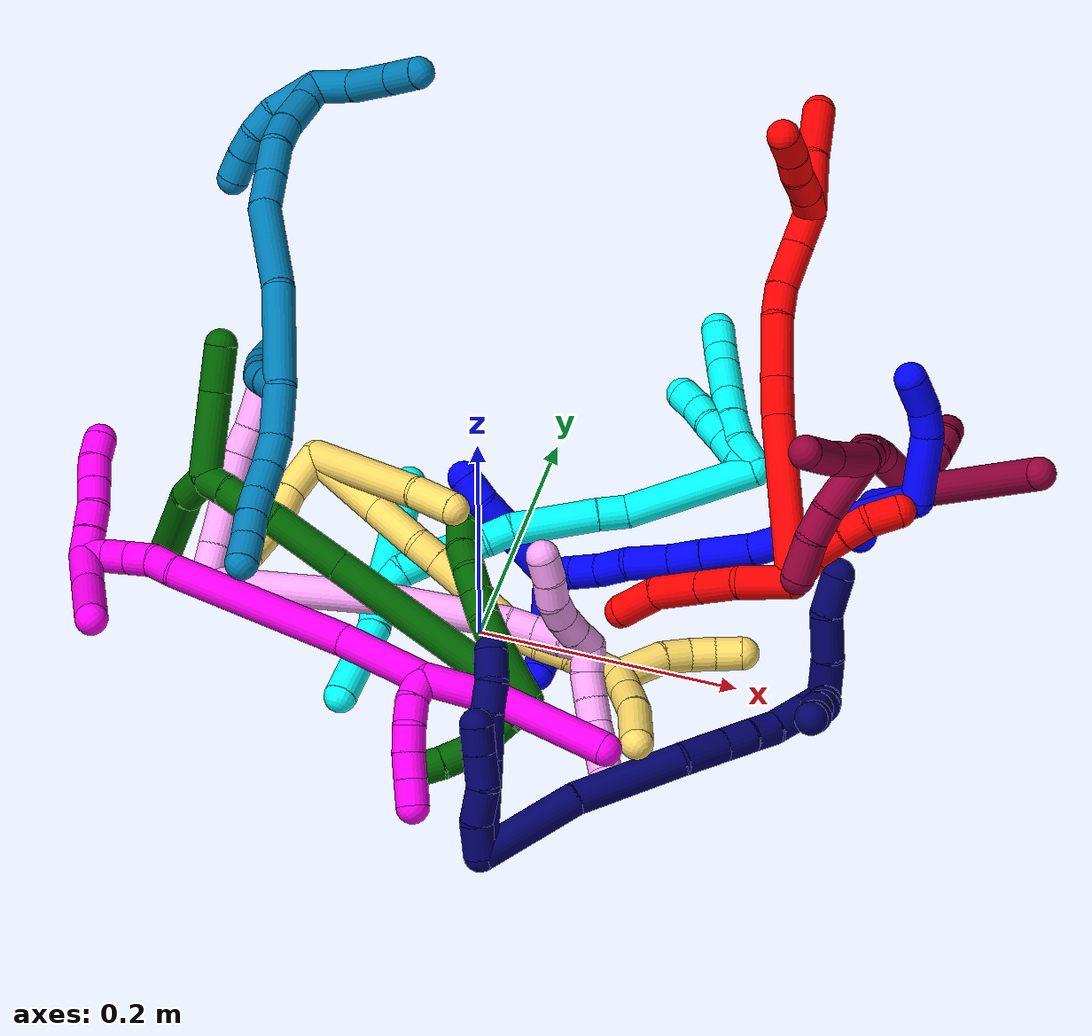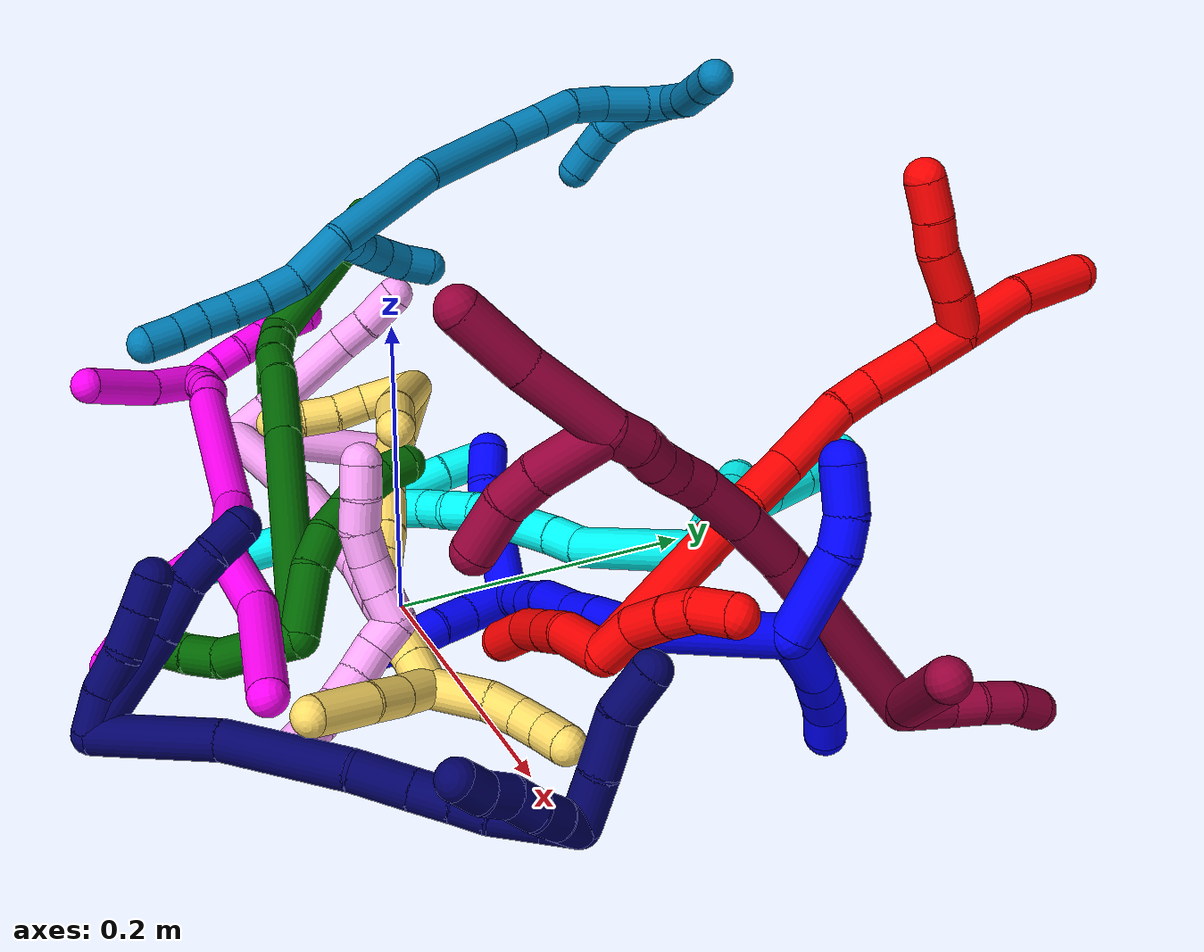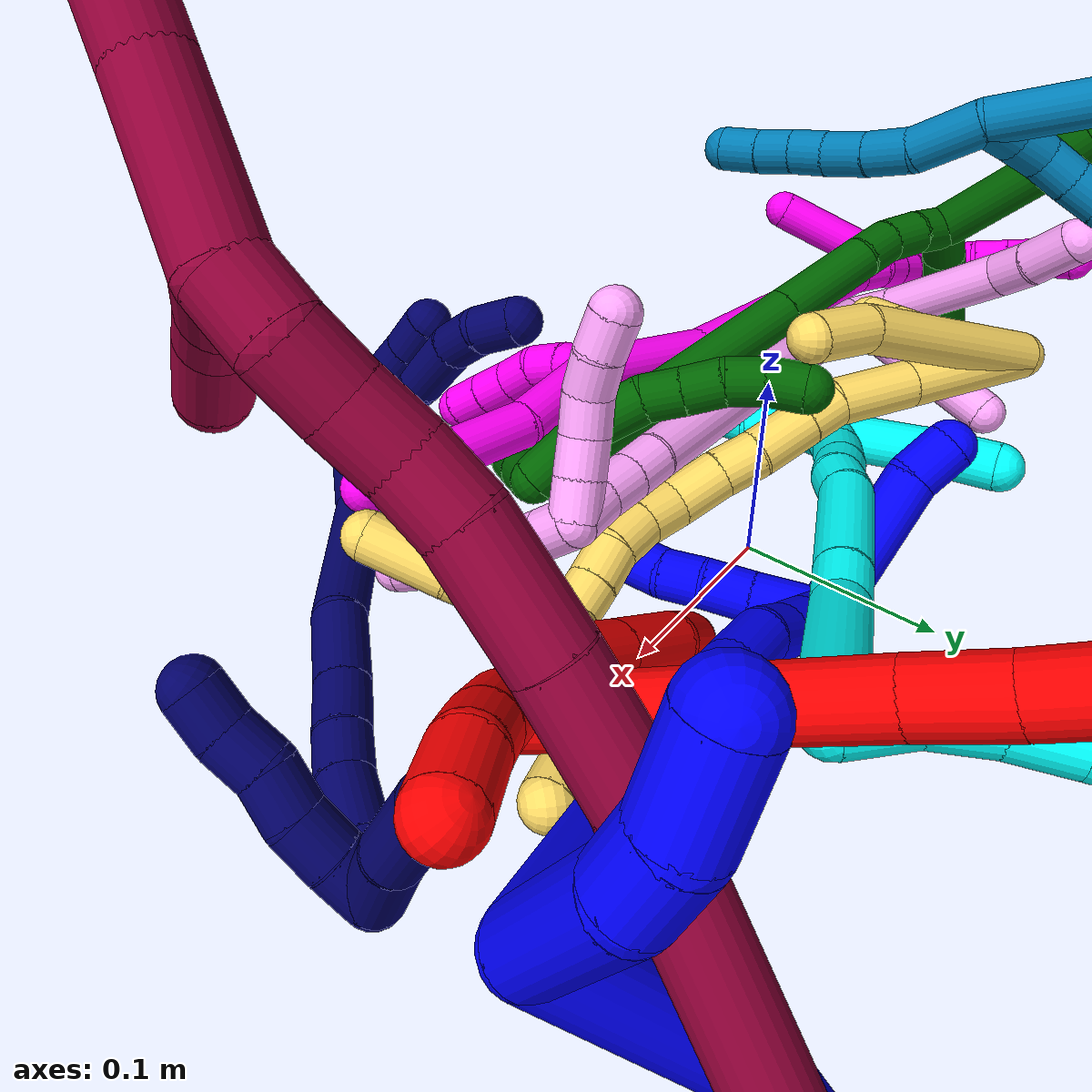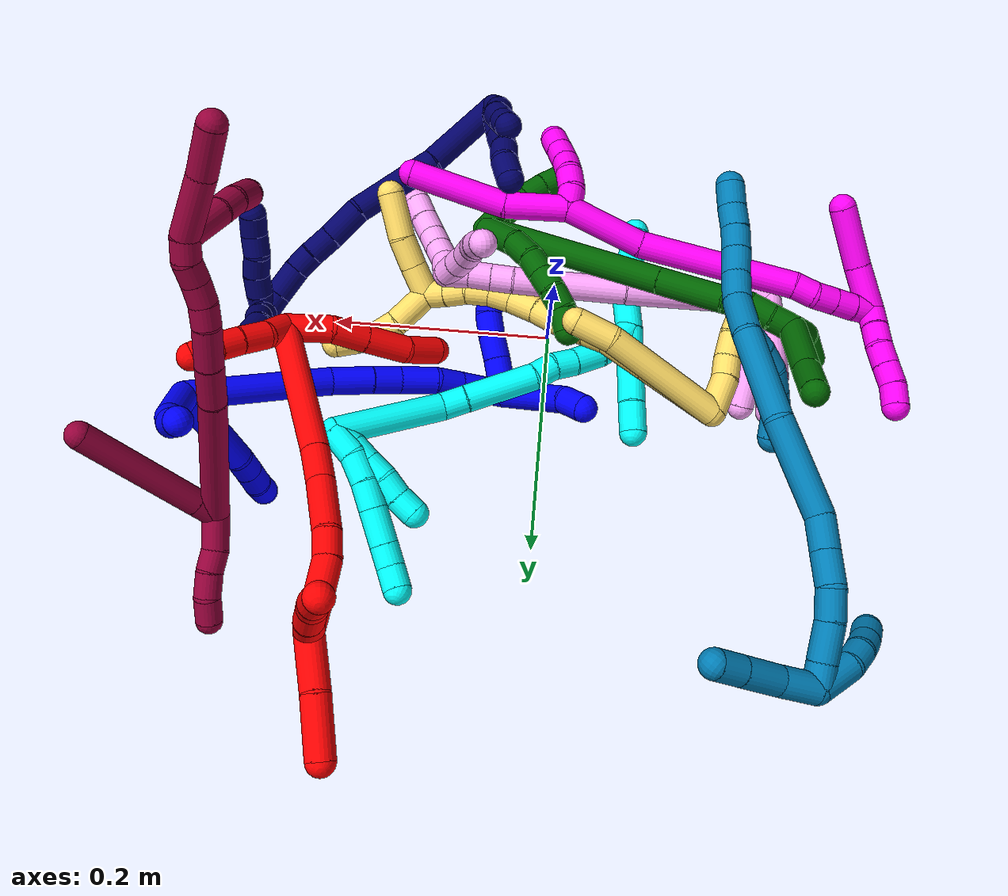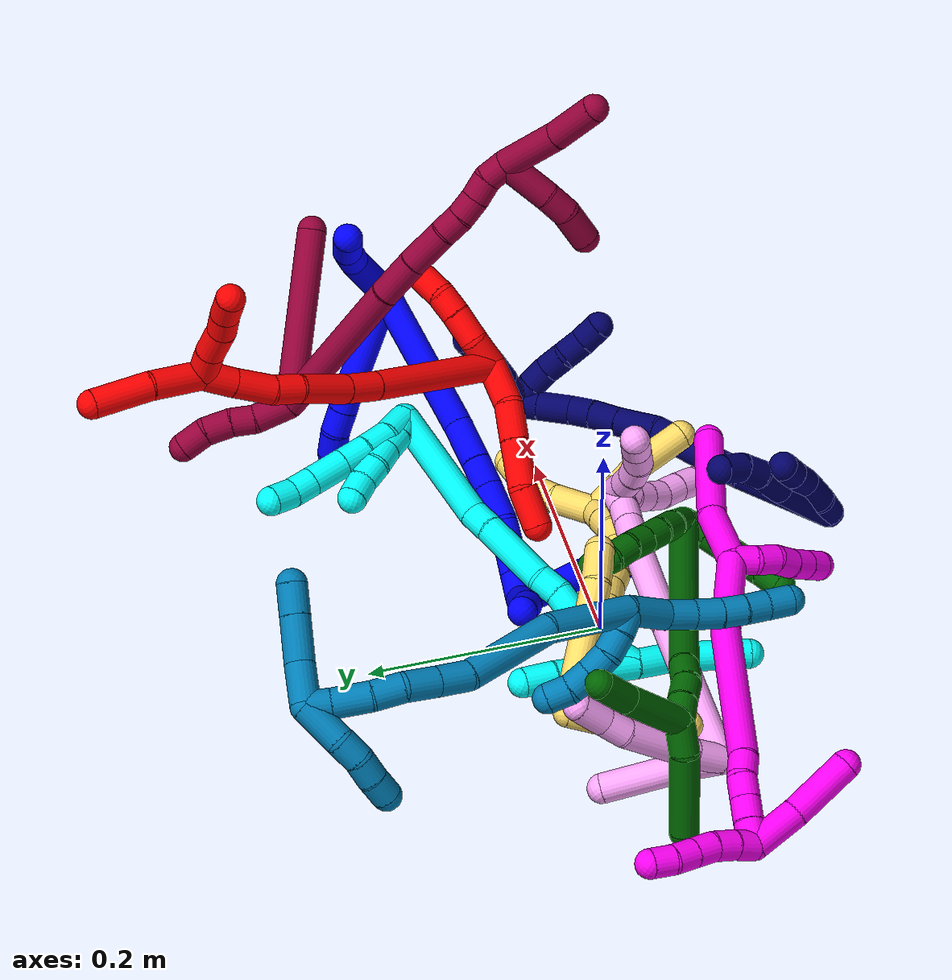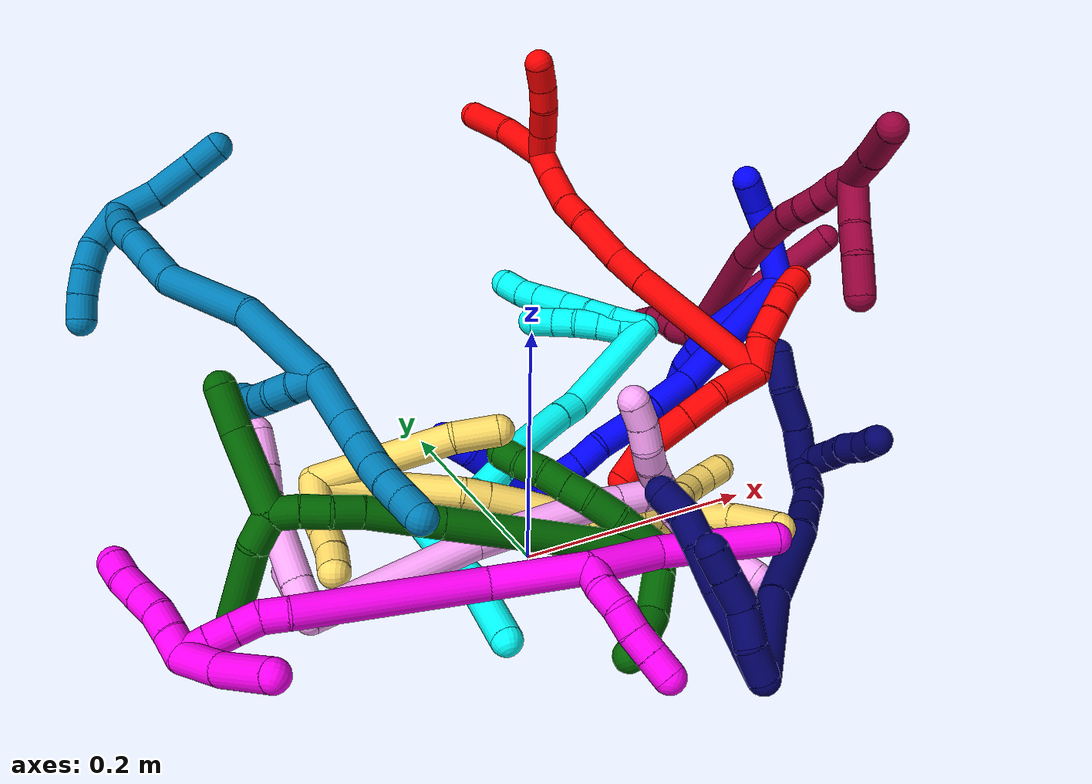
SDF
<sdf version="1.7">
 <world name="default">
  <plugin name="TubeGeneratorPlugin" filename="libtube_generator_plugin.so"/>
  <model name="photoneo_s_sensor">
   <static>1</static>
   <pose>0 0 2 1.57079 1.57079 3.14159</pose>
   <link name="link">
    <inertial><mass>0.1</mass></inertial>
    <sensor name="sensor" type="depth">
     <update_rate>30</update_rate>
     <camera>
      <horizontal_fov>1.22</horizontal_fov>
      <image><width>1920</width><height>1200</height><format>B8G8R8</format></image>
      <clip><near>0.1</near><far>4</far></clip>
      <depth_camera><output>points</output></depth_camera>
     </camera>
     <plugin name="camera_plugin" filename="libgazebo_ros_depth_camera.so">
      <baseline>0.2</baseline>
      <alwaysOn>1</alwaysOn>
      <updateRate>0.0</updateRate>
      <cameraName>camera_ir</cameraName>
      <imageTopicName>/camera/color/image_raw</imageTopicName>
      <cameraInfoTopicName>/camera/color/camera_info</cameraInfoTopicName>
      <depthImageTopicName>/camera/depth/image_raw</depthImageTopicName>
      <depthImageCameraInfoTopicName>/camera/depth/camera_info</depthImageCameraInfoTopicName>
      <pointCloudTopicName>/camera/depth/points</pointCloudTopicName>
      <frameName>fr_optical</frameName>
      <pointCloudCutoff>0.1</pointCloudCutoff>
      <pointCloudCutoffMax>2.0</pointCloudCutoffMax>
      <distortionK1>0</distortionK1>
      <distortionK2>0</distortionK2>
      <distortionK3>0</distortionK3>
      <distortionT1>0</distortionT1>
      <distortionT2>0</distortionT2>
      <CxPrime>0</CxPrime>
      <Cx>0</Cx>
      <Cy>0</Cy>
      <focalLength>0</focalLength>
      <hackBaseline>0</hackBaseline>
     </plugin>
    </sensor>
   </link>
  </model>
  <gravity>0 0 -9.8</gravity>
  <magnetic_field>6e-06 2.3e-05 -4.2e-05</magnetic_field>
  <atmosphere type="adiabatic"/>
  <physics name="default_physics" default="0" type="ode">
   <max_step_size>0.003</max_step_size>
   <real_time_factor>1</real_time_factor>
   <real_time_update_rate>1000</real_time_update_rate>
   <max_contacts>10000</max_contacts>
   <ode>
    <solver>
     <type>quick</type>
     <iters>100</iters>
     <sor>1.3</sor>
     <use_dynamic_moi_rescaling>0</use_dynamic_moi_rescaling>
    </solver>
    <constraints>
     <contact_max_correcting_vel>0</contact_max_correcting_vel>
     <contact_surface_layer>0.001</contact_surface_layer>
     <cfm>0</cfm>
     <erp>0.2</erp>
    </constraints>
   </ode>
  </physics>
  <scene><ambient>0.4 0.4 0.4 1</ambient><background>0.7 0.7 0.7 1</background><shadows>0</shadows></scene>
  <audio><device>default</device></audio>
  <spherical_coordinates>
   <surface_model>EARTH_WGS84</surface_model>
   <latitude_deg>0</latitude_deg>
   <longitude_deg>0</longitude_deg>
   <elevation>0</elevation>
   <heading_deg>0</heading_deg>
  </spherical_coordinates>
  <model name="bin">
   <static>1</static>
   <link name="bottom">
    <collision name="collision-bottom">
     <pose>0 0 -0.01 0 -0 0</pose>
     <geometry><box><size>0.8 0.6 0.02</size></box></geometry>
     <surface>
      <friction><ode><mu>100</mu><mu2>100</mu2></ode></friction>
      <contact><collide_bitmask>65535</collide_bitmask></contact>
     </surface>
    </collision>
   </link>
   <link name="west_wall">
    <collision name="collision-west_wall">
     <pose>-0.41 0 0.1 0 -0 0</pose>
     <geometry><box><size>0.02 0.6 0.2</size></box></geometry>
     <surface>
      <friction><ode><mu>100</mu><mu2>100</mu2></ode></friction>
      <contact><collide_bitmask>65535</collide_bitmask></contact>
     </surface>
    </collision>
   </link>
   <link name="east_wall">
    <collision name="collision-east_wall">
     <pose>0.41 0 0.1 0 -0 0</pose>
     <geometry><box><size>0.02 0.6 0.2</size></box></geometry>
     <surface>
      <friction><ode><mu>100</mu><mu2>100</mu2></ode></friction>
      <contact><collide_bitmask>65535</collide_bitmask></contact>
     </surface>
    </collision>
   </link>
   <link name="south_wall">
    <collision name="collision-south_wall">
     <pose>0 -0.31 0.1 0 -0 0</pose>
     <geometry><box><size>0.8 0.02 0.2</size></box></geometry>
     <surface>
      <friction><ode><mu>100</mu><mu2>100</mu2></ode></friction>
      <contact><collide_bitmask>65535</collide_bitmask></contact>
     </surface>
    </collision>
   </link>
   <link name="north_wall">
    <collision name="collision-north_wall">
     <pose>0 0.31 0.1 0 -0 0</pose>
     <geometry><box><size>0.8 0.02 0.2</size></box></geometry>
     <surface>
      <friction><ode><mu>100</mu><mu2>100</mu2></ode></friction>
      <contact><collide_bitmask>65535</collide_bitmask></contact>
     </surface>
    </collision>
   </link>
  </model>
  <model name="1">
   <static>0</static>
   <link name="1">
    <collision name="collision-cylinder-e_1_2_8">
     <pose>-0.017245 0.033324 -0.020356 -2.11915 -0.41586 0.719472</pose>
     <geometry><cylinder><radius>0.0125</radius><length>0.085376</length></cylinder></geometry>
     <surface>
      <friction><ode><mu>1.16</mu><mu2>1.16</mu2><slip1>0</slip1><slip2>0</slip2></ode></friction>
      <contact><ode><kp>1e+06</kp><kd>1</kd><max_vel>0</max_vel><min_depth>0.001</min_depth></ode></contact>
     </surface>
    </collision>
    <visual name="visual-cylinder-e_1_2_8">
     <pose>-0.017245 0.033324 -0.020356 -2.11915 -0.41586 0.719472</pose>
     <geometry><cylinder><radius>0.0125</radius><length>0.085376</length></cylinder></geometry>
     <material><ambient>0 0 1 1</ambient></material>
    </visual>
    <collision name="collision-cylinder-e_2_8_9">
     <pose>-0.035873 0.075308 -0.045839 -2.10537 -0.136602 0.23886</pose>
     <geometry><cylinder><radius>0.0125</radius><length>0.020316</length></cylinder></geometry>
     <surface>
      <friction><ode><mu>1.16</mu><mu2>1.16</mu2><slip1>0</slip1><slip2>0</slip2></ode></friction>
      <contact><ode><kp>1e+06</kp><kd>1</kd><max_vel>0</max_vel><min_depth>0.001</min_depth></ode></contact>
     </surface>
    </collision>
    <visual name="visual-cylinder-e_2_8_9">
     <pose>-0.035873 0.075308 -0.045839 -2.10537 -0.136602 0.23886</pose>
     <geometry><cylinder><radius>0.0125</radius><length>0.020316</length></cylinder></geometry>
     <material><ambient>0 0 1 1</ambient></material>
    </visual>
    <collision name="collision-cylinder-e_3_9_10">
     <pose>-0.038606 0.093469 -0.056375 -2.08832 -0.122862 0.2108</pose>
     <geometry><cylinder><radius>0.0125</radius><length>0.022033</length></cylinder></geometry>
     <surface>
      <friction><ode><mu>1.16</mu><mu2>1.16</mu2><slip1>0</slip1><slip2>0</slip2></ode></friction>
      <contact><ode><kp>1e+06</kp><kd>1</kd><max_vel>0</max_vel><min_depth>0.001</min_depth></ode></contact>
     </surface>
    </collision>
    <visual name="visual-cylinder-e_3_9_10">
     <pose>-0.038606 0.093469 -0.056375 -2.08832 -0.122862 0.2108</pose>
     <geometry><cylinder><radius>0.0125</radius><length>0.022033</length></cylinder></geometry>
     <material><ambient>0 0 1 1</ambient></material>
    </visual>
    <collision name="collision-cylinder-e_4_10_6">
     <pose>-0.038757 0.111981 -0.06822 -2.19106 0.10789 -0.209091</pose>
     <geometry><cylinder><radius>0.0125</radius><length>0.022275</length></cylinder></geometry>
     <surface>
      <friction><ode><mu>1.16</mu><mu2>1.16</mu2><slip1>0</slip1><slip2>0</slip2></ode></friction>
      <contact><ode><kp>1e+06</kp><kd>1</kd><max_vel>0</max_vel><min_depth>0.001</min_depth></ode></contact>
     </surface>
    </collision>
    <visual name="visual-cylinder-e_4_10_6">
     <pose>-0.038757 0.111981 -0.06822 -2.19106 0.10789 -0.209091</pose>
     <geometry><cylinder><radius>0.0125</radius><length>0.022275</length></cylinder></geometry>
     <material><ambient>0 0 1 1</ambient></material>
    </visual>
    <collision name="collision-cylinder-e_1_2_11">
     <pose>-0.014983 -0.007313 0.019715 0.355203 -0.619077 -0.114684</pose>
     <geometry><cylinder><radius>0.0125</radius><length>0.05164</length></cylinder></geometry>
     <surface>
      <friction><ode><mu>1.16</mu><mu2>1.16</mu2><slip1>0</slip1><slip2>0</slip2></ode></friction>
      <contact><ode><kp>1e+06</kp><kd>1</kd><max_vel>0</max_vel><min_depth>0.001</min_depth></ode></contact>
     </surface>
    </collision>
    <visual name="visual-cylinder-e_1_2_11">
     <pose>-0.014983 -0.007313 0.019715 0.355203 -0.619077 -0.114684</pose>
     <geometry><cylinder><radius>0.0125</radius><length>0.05164</length></cylinder></geometry>
     <material><ambient>0 0 1 1</ambient></material>
    </visual>
    <collision name="collision-cylinder-e_2_11_12">
     <pose>-0.037272 -0.019494 0.044844 0.7323 -0.787196 -0.31581</pose>
     <geometry><cylinder><radius>0.0125</radius><length>0.020628</length></cylinder></geometry>
     <surface>
      <friction><ode><mu>1.16</mu><mu2>1.16</mu2><slip1>0</slip1><slip2>0</slip2></ode></friction>
      <contact><ode><kp>1e+06</kp><kd>1</kd><max_vel>0</max_vel><min_depth>0.001</min_depth></ode></contact>
     </surface>
    </collision>
    <visual name="visual-cylinder-e_2_11_12">
     <pose>-0.037272 -0.019494 0.044844 0.7323 -0.787196 -0.31581</pose>
     <geometry><cylinder><radius>0.0125</radius><length>0.020628</length></cylinder></geometry>
     <material><ambient>0 0 1 1</ambient></material>
    </visual>
    <collision name="collision-cylinder-e_3_12_5">
     <pose>-0.053696 -0.03376 0.054817 1.11917 -0.717626 -0.461471</pose>
     <geometry><cylinder><radius>0.0125</radius><length>0.027732</length></cylinder></geometry>
     <surface>
      <friction><ode><mu>1.16</mu><mu2>1.16</mu2><slip1>0</slip1><slip2>0</slip2></ode></friction>
      <contact><ode><kp>1e+06</kp><kd>1</kd><max_vel>0</max_vel><min_depth>0.001</min_depth></ode></contact>
     </surface>
    </collision>
    <visual name="visual-cylinder-e_3_12_5">
     <pose>-0.053696 -0.03376 0.054817 1.11917 -0.717626 -0.461471</pose>
     <geometry><cylinder><radius>0.0125</radius><length>0.027732</length></cylinder></geometry>
     <material><ambient>0 0 1 1</ambient></material>
    </visual>
    <collision name="collision-cylinder-e_1_2_13">
     <pose>-0.025769 0.000775 -0.060831 -3.12886 -0.400662 3.07888</pose>
     <geometry><cylinder><radius>0.0125</radius><length>0.132138</length></cylinder></geometry>
     <surface>
      <friction><ode><mu>1.16</mu><mu2>1.16</mu2><slip1>0</slip1><slip2>0</slip2></ode></friction>
      <contact><ode><kp>1e+06</kp><kd>1</kd><max_vel>0</max_vel><min_depth>0.001</min_depth></ode></contact>
     </surface>
    </collision>
    <visual name="visual-cylinder-e_1_2_13">
     <pose>-0.025769 0.000775 -0.060831 -3.12886 -0.400662 3.07888</pose>
     <geometry><cylinder><radius>0.0125</radius><length>0.132138</length></cylinder></geometry>
     <material><ambient>0 0 1 1</ambient></material>
    </visual>
    <collision name="collision-cylinder-e_2_13_14">
     <pose>-0.061818 0.000838 -0.137911 3.09779 -0.563694 -2.99059</pose>
     <geometry><cylinder><radius>0.0125</radius><length>0.038481</length></cylinder></geometry>
     <surface>
      <friction><ode><mu>1.16</mu><mu2>1.16</mu2><slip1>0</slip1><slip2>0</slip2></ode></friction>
      <contact><ode><kp>1e+06</kp><kd>1</kd><max_vel>0</max_vel><min_depth>0.001</min_depth></ode></contact>
     </surface>
    </collision>
    <visual name="visual-cylinder-e_2_13_14">
     <pose>-0.061818 0.000838 -0.137911 3.09779 -0.563694 -2.99059</pose>
     <geometry><cylinder><radius>0.0125</radius><length>0.038481</length></cylinder></geometry>
     <material><ambient>0 0 1 1</ambient></material>
    </visual>
    <collision name="collision-cylinder-e_3_14_15">
     <pose>-0.078502 0.000376 -0.165269 -3.11904 -0.522801 3.05735</pose>
     <geometry><cylinder><radius>0.0125</radius><length>0.025652</length></cylinder></geometry>
     <surface>
      <friction><ode><mu>1.16</mu><mu2>1.16</mu2><slip1>0</slip1><slip2>0</slip2></ode></friction>
      <contact><ode><kp>1e+06</kp><kd>1</kd><max_vel>0</max_vel><min_depth>0.001</min_depth></ode></contact>
     </surface>
    </collision>
    <visual name="visual-cylinder-e_3_14_15">
     <pose>-0.078502 0.000376 -0.165269 -3.11904 -0.522801 3.05735</pose>
     <geometry><cylinder><radius>0.0125</radius><length>0.025652</length></cylinder></geometry>
     <material><ambient>0 0 1 1</ambient></material>
    </visual>
    <collision name="collision-cylinder-e_4_15_16">
     <pose>-0.09473 0.000362 -0.190338 3.12262 -0.613145 -3.08168</pose>
     <geometry><cylinder><radius>0.0125</radius><length>0.034141</length></cylinder></geometry>
     <surface>
      <friction><ode><mu>1.16</mu><mu2>1.16</mu2><slip1>0</slip1><slip2>0</slip2></ode></friction>
      <contact><ode><kp>1e+06</kp><kd>1</kd><max_vel>0</max_vel><min_depth>0.001</min_depth></ode></contact>
     </surface>
    </collision>
    <visual name="visual-cylinder-e_4_15_16">
     <pose>-0.09473 0.000362 -0.190338 3.12262 -0.613145 -3.08168</pose>
     <geometry><cylinder><radius>0.0125</radius><length>0.034141</length></cylinder></geometry>
     <material><ambient>0 0 1 1</ambient></material>
    </visual>
    <collision name="collision-cylinder-e_5_16_17">
     <pose>-0.110126 0.003205 -0.214651 -2.84995 -0.475982 2.05284</pose>
     <geometry><cylinder><radius>0.0125</radius><length>0.024326</length></cylinder></geometry>
     <surface>
      <friction><ode><mu>1.16</mu><mu2>1.16</mu2><slip1>0</slip1><slip2>0</slip2></ode></friction>
      <contact><ode><kp>1e+06</kp><kd>1</kd><max_vel>0</max_vel><min_depth>0.001</min_depth></ode></contact>
     </surface>
    </collision>
    <visual name="visual-cylinder-e_5_16_17">
     <pose>-0.110126 0.003205 -0.214651 -2.84995 -0.475982 2.05284</pose>
     <geometry><cylinder><radius>0.0125</radius><length>0.024326</length></cylinder></geometry>
     <material><ambient>0 0 1 1</ambient></material>
    </visual>
    <collision name="collision-cylinder-e_6_17_18">
     <pose>-0.121935 0.008476 -0.233899 -2.90307 -0.598089 2.40015</pose>
     <geometry><cylinder><radius>0.0125</radius><length>0.022151</length></cylinder></geometry>
     <surface>
      <friction><ode><mu>1.16</mu><mu2>1.16</mu2><slip1>0</slip1><slip2>0</slip2></ode></friction>
      <contact><ode><kp>1e+06</kp><kd>1</kd><max_vel>0</max_vel><min_depth>0.001</min_depth></ode></contact>
     </surface>
    </collision>
    <visual name="visual-cylinder-e_6_17_18">
     <pose>-0.121935 0.008476 -0.233899 -2.90307 -0.598089 2.40015</pose>
     <geometry><cylinder><radius>0.0125</radius><length>0.022151</length></cylinder></geometry>
     <material><ambient>0 0 1 1</ambient></material>
    </visual>
    <collision name="collision-cylinder-e_7_18_1">
     <pose>-0.1346 0.01297 -0.252108 -2.8964 -0.589943 2.37107</pose>
     <geometry><cylinder><radius>0.0125</radius><length>0.023111</length></cylinder></geometry>
     <surface>
      <friction><ode><mu>1.16</mu><mu2>1.16</mu2><slip1>0</slip1><slip2>0</slip2></ode></friction>
      <contact><ode><kp>1e+06</kp><kd>1</kd><max_vel>0</max_vel><min_depth>0.001</min_depth></ode></contact>
     </surface>
    </collision>
    <visual name="visual-cylinder-e_7_18_1">
     <pose>-0.1346 0.01297 -0.252108 -2.8964 -0.589943 2.37107</pose>
     <geometry><cylinder><radius>0.0125</radius><length>0.023111</length></cylinder></geometry>
     <material><ambient>0 0 1 1</ambient></material>
    </visual>
    <collision name="collision-cylinder-e_1_1_19">
     <pose>-0.173837 -0.004318 -0.260958 1.5471 -1.03174 -1.01152</pose>
     <geometry><cylinder><radius>0.0125</radius><length>0.076459</length></cylinder></geometry>
     <surface>
      <friction><ode><mu>1.16</mu><mu2>1.16</mu2><slip1>0</slip1><slip2>0</slip2></ode></friction>
      <contact><ode><kp>1e+06</kp><kd>1</kd><max_vel>0</max_vel><min_depth>0.001</min_depth></ode></contact>
     </surface>
    </collision>
    <visual name="visual-cylinder-e_1_1_19">
     <pose>-0.173837 -0.004318 -0.260958 1.5471 -1.03174 -1.01152</pose>
     <geometry><cylinder><radius>0.0125</radius><length>0.076459</length></cylinder></geometry>
     <material><ambient>0 0 1 1</ambient></material>
    </visual>
    <collision name="collision-cylinder-e_2_19_4">
     <pose>-0.217991 -0.027015 -0.259897 1.37954 -1.30114 -1.12133</pose>
     <geometry><cylinder><radius>0.0125</radius><length>0.023541</length></cylinder></geometry>
     <surface>
      <friction><ode><mu>1.16</mu><mu2>1.16</mu2><slip1>0</slip1><slip2>0</slip2></ode></friction>
      <contact><ode><kp>1e+06</kp><kd>1</kd><max_vel>0</max_vel><min_depth>0.001</min_depth></ode></contact>
     </surface>
    </collision>
    <visual name="visual-cylinder-e_2_19_4">
     <pose>-0.217991 -0.027015 -0.259897 1.37954 -1.30114 -1.12133</pose>
     <geometry><cylinder><radius>0.0125</radius><length>0.023541</length></cylinder></geometry>
     <material><ambient>0 0 1 1</ambient></material>
    </visual>
    <collision name="collision-cylinder-e_1_1_20">
     <pose>-0.128881 0.005573 -0.267222 2.10837 0.820419 1.30675</pose>
     <geometry><cylinder><radius>0.0125</radius><length>0.033216</length></cylinder></geometry>
     <surface>
      <friction><ode><mu>1.16</mu><mu2>1.16</mu2><slip1>0</slip1><slip2>0</slip2></ode></friction>
      <contact><ode><kp>1e+06</kp><kd>1</kd><max_vel>0</max_vel><min_depth>0.001</min_depth></ode></contact>
     </surface>
    </collision>
    <visual name="visual-cylinder-e_1_1_20">
     <pose>-0.128881 0.005573 -0.267222 2.10837 0.820419 1.30675</pose>
     <geometry><cylinder><radius>0.0125</radius><length>0.033216</length></cylinder></geometry>
     <material><ambient>0 0 1 1</ambient></material>
    </visual>
    <collision name="collision-cylinder-e_2_20_21">
     <pose>-0.108095 -0.011581 -0.276168 1.97156 0.819726 1.16107</pose>
     <geometry><cylinder><radius>0.0125</radius><length>0.023638</length></cylinder></geometry>
     <surface>
      <friction><ode><mu>1.16</mu><mu2>1.16</mu2><slip1>0</slip1><slip2>0</slip2></ode></friction>
      <contact><ode><kp>1e+06</kp><kd>1</kd><max_vel>0</max_vel><min_depth>0.001</min_depth></ode></contact>
     </surface>
    </collision>
    <visual name="visual-cylinder-e_2_20_21">
     <pose>-0.108095 -0.011581 -0.276168 1.97156 0.819726 1.16107</pose>
     <geometry><cylinder><radius>0.0125</radius><length>0.023638</length></cylinder></geometry>
     <material><ambient>0 0 1 1</ambient></material>
    </visual>
    <collision name="collision-cylinder-e_3_21_22">
     <pose>-0.092044 -0.024631 -0.283413 2.20071 0.816893 1.41023</pose>
     <geometry><cylinder><radius>0.0125</radius><length>0.020333</length></cylinder></geometry>
     <surface>
      <friction><ode><mu>1.16</mu><mu2>1.16</mu2><slip1>0</slip1><slip2>0</slip2></ode></friction>
      <contact><ode><kp>1e+06</kp><kd>1</kd><max_vel>0</max_vel><min_depth>0.001</min_depth></ode></contact>
     </surface>
    </collision>
    <visual name="visual-cylinder-e_3_21_22">
     <pose>-0.092044 -0.024631 -0.283413 2.20071 0.816893 1.41023</pose>
     <geometry><cylinder><radius>0.0125</radius><length>0.020333</length></cylinder></geometry>
     <material><ambient>0 0 1 1</ambient></material>
    </visual>
    <collision name="collision-cylinder-e_4_22_3">
     <pose>-0.078396 -0.037454 -0.293789 2.28778 0.578415 1.15854</pose>
     <geometry><cylinder><radius>0.0125</radius><length>0.022814</length></cylinder></geometry>
     <surface>
      <friction><ode><mu>1.16</mu><mu2>1.16</mu2><slip1>0</slip1><slip2>0</slip2></ode></friction>
      <contact><ode><kp>1e+06</kp><kd>1</kd><max_vel>0</max_vel><min_depth>0.001</min_depth></ode></contact>
     </surface>
    </collision>
    <visual name="visual-cylinder-e_4_22_3">
     <pose>-0.078396 -0.037454 -0.293789 2.28778 0.578415 1.15854</pose>
     <geometry><cylinder><radius>0.0125</radius><length>0.022814</length></cylinder></geometry>
     <material><ambient>0 0 1 1</ambient></material>
    </visual>
    <collision name="collision-sphere-3">
     <pose>-0.07216 -0.044654 -0.300065 0 -0 0</pose>
     <geometry><sphere><radius>0.0125</radius></sphere></geometry>
     <surface>
      <friction><ode><mu>1.16</mu><mu2>1.16</mu2><slip1>0</slip1><slip2>0</slip2></ode></friction>
      <contact><ode><kp>1e+06</kp><kd>1</kd><max_vel>0</max_vel><min_depth>0.001</min_depth></ode></contact>
     </surface>
    </collision>
    <visual name="visual-sphere-3">
     <pose>-0.07216 -0.044654 -0.300065 0 -0 0</pose>
     <geometry><sphere><radius>0.0125</radius></sphere></geometry>
     <material><ambient>0 0 1 1</ambient></material>
    </visual>
    <collision name="collision-sphere-22">
     <pose>-0.084633 -0.030254 -0.287513 0 -0 0</pose>
     <geometry><sphere><radius>0.0125</radius></sphere></geometry>
     <surface>
      <friction><ode><mu>1.16</mu><mu2>1.16</mu2><slip1>0</slip1><slip2>0</slip2></ode></friction>
      <contact><ode><kp>1e+06</kp><kd>1</kd><max_vel>0</max_vel><min_depth>0.001</min_depth></ode></contact>
     </surface>
    </collision>
    <visual name="visual-sphere-22">
     <pose>-0.084633 -0.030254 -0.287513 0 -0 0</pose>
     <geometry><sphere><radius>0.0125</radius></sphere></geometry>
     <material><ambient>0 0 1 1</ambient></material>
    </visual>
    <collision name="collision-sphere-21">
     <pose>-0.099456 -0.019008 -0.279314 0 -0 0</pose>
     <geometry><sphere><radius>0.0125</radius></sphere></geometry>
     <surface>
      <friction><ode><mu>1.16</mu><mu2>1.16</mu2><slip1>0</slip1><slip2>0</slip2></ode></friction>
      <contact><ode><kp>1e+06</kp><kd>1</kd><max_vel>0</max_vel><min_depth>0.001</min_depth></ode></contact>
     </surface>
    </collision>
    <visual name="visual-sphere-21">
     <pose>-0.099456 -0.019008 -0.279314 0 -0 0</pose>
     <geometry><sphere><radius>0.0125</radius></sphere></geometry>
     <material><ambient>0 0 1 1</ambient></material>
    </visual>
    <collision name="collision-sphere-20">
     <pose>-0.116734 -0.004155 -0.273021 0 -0 0</pose>
     <geometry><sphere><radius>0.0125</radius></sphere></geometry>
     <surface>
      <friction><ode><mu>1.16</mu><mu2>1.16</mu2><slip1>0</slip1><slip2>0</slip2></ode></friction>
      <contact><ode><kp>1e+06</kp><kd>1</kd><max_vel>0</max_vel><min_depth>0.001</min_depth></ode></contact>
     </surface>
    </collision>
    <visual name="visual-sphere-20">
     <pose>-0.116734 -0.004155 -0.273021 0 -0 0</pose>
     <geometry><sphere><radius>0.0125</radius></sphere></geometry>
     <material><ambient>0 0 1 1</ambient></material>
    </visual>
    <collision name="collision-sphere-4">
     <pose>-0.229336 -0.030094 -0.259301 0 -0 0</pose>
     <geometry><sphere><radius>0.0125</radius></sphere></geometry>
     <surface>
      <friction><ode><mu>1.16</mu><mu2>1.16</mu2><slip1>0</slip1><slip2>0</slip2></ode></friction>
      <contact><ode><kp>1e+06</kp><kd>1</kd><max_vel>0</max_vel><min_depth>0.001</min_depth></ode></contact>
     </surface>
    </collision>
    <visual name="visual-sphere-4">
     <pose>-0.229336 -0.030094 -0.259301 0 -0 0</pose>
     <geometry><sphere><radius>0.0125</radius></sphere></geometry>
     <material><ambient>0 0 1 1</ambient></material>
    </visual>
    <collision name="collision-sphere-11">
     <pose>-0.029966 -0.014626 0.039431 0 -0 0</pose>
     <geometry><sphere><radius>0.0125</radius></sphere></geometry>
     <surface>
      <friction><ode><mu>1.16</mu><mu2>1.16</mu2><slip1>0</slip1><slip2>0</slip2></ode></friction>
      <contact><ode><kp>1e+06</kp><kd>1</kd><max_vel>0</max_vel><min_depth>0.001</min_depth></ode></contact>
     </surface>
    </collision>
    <visual name="visual-sphere-11">
     <pose>-0.029966 -0.014626 0.039431 0 -0 0</pose>
     <geometry><sphere><radius>0.0125</radius></sphere></geometry>
     <material><ambient>0 0 1 1</ambient></material>
    </visual>
    <collision name="collision-sphere-6">
     <pose>-0.037558 0.120991 -0.074656 0 -0 0</pose>
     <geometry><sphere><radius>0.0125</radius></sphere></geometry>
     <surface>
      <friction><ode><mu>1.16</mu><mu2>1.16</mu2><slip1>0</slip1><slip2>0</slip2></ode></friction>
      <contact><ode><kp>1e+06</kp><kd>1</kd><max_vel>0</max_vel><min_depth>0.001</min_depth></ode></contact>
     </surface>
    </collision>
    <visual name="visual-sphere-6">
     <pose>-0.037558 0.120991 -0.074656 0 -0 0</pose>
     <geometry><sphere><radius>0.0125</radius></sphere></geometry>
     <material><ambient>0 0 1 1</ambient></material>
    </visual>
    <collision name="collision-sphere-10">
     <pose>-0.039957 0.102971 -0.061784 0 -0 0</pose>
     <geometry><sphere><radius>0.0125</radius></sphere></geometry>
     <surface>
      <friction><ode><mu>1.16</mu><mu2>1.16</mu2><slip1>0</slip1><slip2>0</slip2></ode></friction>
      <contact><ode><kp>1e+06</kp><kd>1</kd><max_vel>0</max_vel><min_depth>0.001</min_depth></ode></contact>
     </surface>
    </collision>
    <visual name="visual-sphere-10">
     <pose>-0.039957 0.102971 -0.061784 0 -0 0</pose>
     <geometry><sphere><radius>0.0125</radius></sphere></geometry>
     <material><ambient>0 0 1 1</ambient></material>
    </visual>
    <collision name="collision-sphere-9">
     <pose>-0.037256 0.083967 -0.050966 0 -0 0</pose>
     <geometry><sphere><radius>0.0125</radius></sphere></geometry>
     <surface>
      <friction><ode><mu>1.16</mu><mu2>1.16</mu2><slip1>0</slip1><slip2>0</slip2></ode></friction>
      <contact><ode><kp>1e+06</kp><kd>1</kd><max_vel>0</max_vel><min_depth>0.001</min_depth></ode></contact>
     </surface>
    </collision>
    <visual name="visual-sphere-9">
     <pose>-0.037256 0.083967 -0.050966 0 -0 0</pose>
     <geometry><sphere><radius>0.0125</radius></sphere></geometry>
     <material><ambient>0 0 1 1</ambient></material>
    </visual>
    <collision name="collision-sphere-2">
     <geometry><sphere><radius>0.0125</radius></sphere></geometry>
     <surface>
      <friction><ode><mu>1.16</mu><mu2>1.16</mu2><slip1>0</slip1><slip2>0</slip2></ode></friction>
      <contact><ode><kp>1e+06</kp><kd>1</kd><max_vel>0</max_vel><min_depth>0.001</min_depth></ode></contact>
     </surface>
    </collision>
    <visual name="visual-sphere-2">
     <geometry><sphere><radius>0.0125</radius></sphere></geometry>
     <material><ambient>0 0 1 1</ambient></material>
    </visual>
    <collision name="collision-sphere-19">
     <pose>-0.206645 -0.023937 -0.260493 0 -0 0</pose>
     <geometry><sphere><radius>0.0125</radius></sphere></geometry>
     <surface>
      <friction><ode><mu>1.16</mu><mu2>1.16</mu2><slip1>0</slip1><slip2>0</slip2></ode></friction>
      <contact><ode><kp>1e+06</kp><kd>1</kd><max_vel>0</max_vel><min_depth>0.001</min_depth></ode></contact>
     </surface>
    </collision>
    <visual name="visual-sphere-19">
     <pose>-0.206645 -0.023937 -0.260493 0 -0 0</pose>
     <geometry><sphere><radius>0.0125</radius></sphere></geometry>
     <material><ambient>0 0 1 1</ambient></material>
    </visual>
    <collision name="collision-sphere-8">
     <pose>-0.03449 0.066648 -0.040712 0 -0 0</pose>
     <geometry><sphere><radius>0.0125</radius></sphere></geometry>
     <surface>
      <friction><ode><mu>1.16</mu><mu2>1.16</mu2><slip1>0</slip1><slip2>0</slip2></ode></friction>
      <contact><ode><kp>1e+06</kp><kd>1</kd><max_vel>0</max_vel><min_depth>0.001</min_depth></ode></contact>
     </surface>
    </collision>
    <visual name="visual-sphere-8">
     <pose>-0.03449 0.066648 -0.040712 0 -0 0</pose>
     <geometry><sphere><radius>0.0125</radius></sphere></geometry>
     <material><ambient>0 0 1 1</ambient></material>
    </visual>
    <collision name="collision-sphere-12">
     <pose>-0.044578 -0.024361 0.050258 0 -0 0</pose>
     <geometry><sphere><radius>0.0125</radius></sphere></geometry>
     <surface>
      <friction><ode><mu>1.16</mu><mu2>1.16</mu2><slip1>0</slip1><slip2>0</slip2></ode></friction>
      <contact><ode><kp>1e+06</kp><kd>1</kd><max_vel>0</max_vel><min_depth>0.001</min_depth></ode></contact>
     </surface>
    </collision>
    <visual name="visual-sphere-12">
     <pose>-0.044578 -0.024361 0.050258 0 -0 0</pose>
     <geometry><sphere><radius>0.0125</radius></sphere></geometry>
     <material><ambient>0 0 1 1</ambient></material>
    </visual>
    <collision name="collision-sphere-5">
     <pose>-0.062815 -0.043159 0.059376 0 -0 0</pose>
     <geometry><sphere><radius>0.0125</radius></sphere></geometry>
     <surface>
      <friction><ode><mu>1.16</mu><mu2>1.16</mu2><slip1>0</slip1><slip2>0</slip2></ode></friction>
      <contact><ode><kp>1e+06</kp><kd>1</kd><max_vel>0</max_vel><min_depth>0.001</min_depth></ode></contact>
     </surface>
    </collision>
    <visual name="visual-sphere-5">
     <pose>-0.062815 -0.043159 0.059376 0 -0 0</pose>
     <geometry><sphere><radius>0.0125</radius></sphere></geometry>
     <material><ambient>0 0 1 1</ambient></material>
    </visual>
    <collision name="collision-sphere-13">
     <pose>-0.051537 0.00155 -0.121663 0 -0 0</pose>
     <geometry><sphere><radius>0.0125</radius></sphere></geometry>
     <surface>
      <friction><ode><mu>1.16</mu><mu2>1.16</mu2><slip1>0</slip1><slip2>0</slip2></ode></friction>
      <contact><ode><kp>1e+06</kp><kd>1</kd><max_vel>0</max_vel><min_depth>0.001</min_depth></ode></contact>
     </surface>
    </collision>
    <visual name="visual-sphere-13">
     <pose>-0.051537 0.00155 -0.121663 0 -0 0</pose>
     <geometry><sphere><radius>0.0125</radius></sphere></geometry>
     <material><ambient>0 0 1 1</ambient></material>
    </visual>
    <collision name="collision-sphere-14">
     <pose>-0.072098 0.000126 -0.154159 0 -0 0</pose>
     <geometry><sphere><radius>0.0125</radius></sphere></geometry>
     <surface>
      <friction><ode><mu>1.16</mu><mu2>1.16</mu2><slip1>0</slip1><slip2>0</slip2></ode></friction>
      <contact><ode><kp>1e+06</kp><kd>1</kd><max_vel>0</max_vel><min_depth>0.001</min_depth></ode></contact>
     </surface>
    </collision>
    <visual name="visual-sphere-14">
     <pose>-0.072098 0.000126 -0.154159 0 -0 0</pose>
     <geometry><sphere><radius>0.0125</radius></sphere></geometry>
     <material><ambient>0 0 1 1</ambient></material>
    </visual>
    <collision name="collision-sphere-15">
     <pose>-0.084907 0.000627 -0.176379 0 -0 0</pose>
     <geometry><sphere><radius>0.0125</radius></sphere></geometry>
     <surface>
      <friction><ode><mu>1.16</mu><mu2>1.16</mu2><slip1>0</slip1><slip2>0</slip2></ode></friction>
      <contact><ode><kp>1e+06</kp><kd>1</kd><max_vel>0</max_vel><min_depth>0.001</min_depth></ode></contact>
     </surface>
    </collision>
    <visual name="visual-sphere-15">
     <pose>-0.084907 0.000627 -0.176379 0 -0 0</pose>
     <geometry><sphere><radius>0.0125</radius></sphere></geometry>
     <material><ambient>0 0 1 1</ambient></material>
    </visual>
    <collision name="collision-sphere-16">
     <pose>-0.104553 9.7e-05 -0.204296 0 -0 0</pose>
     <geometry><sphere><radius>0.0125</radius></sphere></geometry>
     <surface>
      <friction><ode><mu>1.16</mu><mu2>1.16</mu2><slip1>0</slip1><slip2>0</slip2></ode></friction>
      <contact><ode><kp>1e+06</kp><kd>1</kd><max_vel>0</max_vel><min_depth>0.001</min_depth></ode></contact>
     </surface>
    </collision>
    <visual name="visual-sphere-16">
     <pose>-0.104553 9.7e-05 -0.204296 0 -0 0</pose>
     <geometry><sphere><radius>0.0125</radius></sphere></geometry>
     <material><ambient>0 0 1 1</ambient></material>
    </visual>
    <collision name="collision-sphere-17">
     <pose>-0.115699 0.006314 -0.225005 0 -0 0</pose>
     <geometry><sphere><radius>0.0125</radius></sphere></geometry>
     <surface>
      <friction><ode><mu>1.16</mu><mu2>1.16</mu2><slip1>0</slip1><slip2>0</slip2></ode></friction>
      <contact><ode><kp>1e+06</kp><kd>1</kd><max_vel>0</max_vel><min_depth>0.001</min_depth></ode></contact>
     </surface>
    </collision>
    <visual name="visual-sphere-17">
     <pose>-0.115699 0.006314 -0.225005 0 -0 0</pose>
     <geometry><sphere><radius>0.0125</radius></sphere></geometry>
     <material><ambient>0 0 1 1</ambient></material>
    </visual>
    <collision name="collision-sphere-18">
     <pose>-0.128172 0.010639 -0.242792 0 -0 0</pose>
     <geometry><sphere><radius>0.0125</radius></sphere></geometry>
     <surface>
      <friction><ode><mu>1.16</mu><mu2>1.16</mu2><slip1>0</slip1><slip2>0</slip2></ode></friction>
      <contact><ode><kp>1e+06</kp><kd>1</kd><max_vel>0</max_vel><min_depth>0.001</min_depth></ode></contact>
     </surface>
    </collision>
    <visual name="visual-sphere-18">
     <pose>-0.128172 0.010639 -0.242792 0 -0 0</pose>
     <geometry><sphere><radius>0.0125</radius></sphere></geometry>
     <material><ambient>0 0 1 1</ambient></material>
    </visual>
    <collision name="collision-sphere-1">
     <pose>-0.141029 0.015301 -0.261423 0 -0 0</pose>
     <geometry><sphere><radius>0.0125</radius></sphere></geometry>
     <surface>
      <friction><ode><mu>1.16</mu><mu2>1.16</mu2><slip1>0</slip1><slip2>0</slip2></ode></friction>
      <contact><ode><kp>1e+06</kp><kd>1</kd><max_vel>0</max_vel><min_depth>0.001</min_depth></ode></contact>
     </surface>
    </collision>
    <visual name="visual-sphere-1">
     <pose>-0.141029 0.015301 -0.261423 0 -0 0</pose>
     <geometry><sphere><radius>0.0125</radius></sphere></geometry>
     <material><ambient>0 0 1 1</ambient></material>
    </visual>
    <inertial>
     <pose>-0.073851 0.007367 -0.128293 0 -0 0</pose>
     <mass>0.75</mass>
     <inertia>
      <ixx>-0.000112</ixx>
      <ixy>0</ixy>
      <ixz>0</ixz>
      <iyy>0.000288</iyy>
      <iyz>0</iyz>
      <izz>0.000109</izz>
     </inertia>
    </inertial>
   </link>
   <pose>0.306493 0.103711 0.131364 -0.892329 0.346844 -0.623385</pose>
  </model>
  <model name="2">
   <static>0</static>
   <link name="2">
    <collision name="collision-cylinder-e_1_2_8">
     <pose>-0.012619 0.016271 -0.000299 -1.58916 -0.659568 0.670905</pose>
     <geometry><cylinder><radius>0.0125</radius><length>0.041186</length></cylinder></geometry>
     <surface>
      <friction><ode><mu>1.16</mu><mu2>1.16</mu2><slip1>0</slip1><slip2>0</slip2></ode></friction>
      <contact><ode><kp>1e+06</kp><kd>1</kd><max_vel>0</max_vel><min_depth>0.001</min_depth></ode></contact>
     </surface>
    </collision>
    <visual name="visual-cylinder-e_1_2_8">
     <pose>-0.012619 0.016271 -0.000299 -1.58916 -0.659568 0.670905</pose>
     <geometry><cylinder><radius>0.0125</radius><length>0.041186</length></cylinder></geometry>
     <material><ambient>1 0 0 1</ambient></material>
    </visual>
    <collision name="collision-cylinder-e_2_8_9">
     <pose>-0.030676 0.047789 -0.003172 -1.73806 -0.338184 0.398566</pose>
     <geometry><cylinder><radius>0.0125</radius><length>0.032782</length></cylinder></geometry>
     <surface>
      <friction><ode><mu>1.16</mu><mu2>1.16</mu2><slip1>0</slip1><slip2>0</slip2></ode></friction>
      <contact><ode><kp>1e+06</kp><kd>1</kd><max_vel>0</max_vel><min_depth>0.001</min_depth></ode></contact>
     </surface>
    </collision>
    <visual name="visual-cylinder-e_2_8_9">
     <pose>-0.030676 0.047789 -0.003172 -1.73806 -0.338184 0.398566</pose>
     <geometry><cylinder><radius>0.0125</radius><length>0.032782</length></cylinder></geometry>
     <material><ambient>1 0 0 1</ambient></material>
    </visual>
    <collision name="collision-cylinder-e_3_9_10">
     <pose>-0.04322 0.082355 -0.009078 -1.74158 -0.347727 0.411148</pose>
     <geometry><cylinder><radius>0.0125</radius><length>0.041706</length></cylinder></geometry>
     <surface>
      <friction><ode><mu>1.16</mu><mu2>1.16</mu2><slip1>0</slip1><slip2>0</slip2></ode></friction>
      <contact><ode><kp>1e+06</kp><kd>1</kd><max_vel>0</max_vel><min_depth>0.001</min_depth></ode></contact>
     </surface>
    </collision>
    <visual name="visual-cylinder-e_3_9_10">
     <pose>-0.04322 0.082355 -0.009078 -1.74158 -0.347727 0.411148</pose>
     <geometry><cylinder><radius>0.0125</radius><length>0.041706</length></cylinder></geometry>
     <material><ambient>1 0 0 1</ambient></material>
    </visual>
    <collision name="collision-cylinder-e_4_10_6">
     <pose>-0.056751 0.115651 -0.020024 -2.06961 -0.383702 0.632095</pose>
     <geometry><cylinder><radius>0.0125</radius><length>0.034326</length></cylinder></geometry>
     <surface>
      <friction><ode><mu>1.16</mu><mu2>1.16</mu2><slip1>0</slip1><slip2>0</slip2></ode></friction>
      <contact><ode><kp>1e+06</kp><kd>1</kd><max_vel>0</max_vel><min_depth>0.001</min_depth></ode></contact>
     </surface>
    </collision>
    <visual name="visual-cylinder-e_4_10_6">
     <pose>-0.056751 0.115651 -0.020024 -2.06961 -0.383702 0.632095</pose>
     <geometry><cylinder><radius>0.0125</radius><length>0.034326</length></cylinder></geometry>
     <material><ambient>1 0 0 1</ambient></material>
    </visual>
    <collision name="collision-cylinder-e_1_2_11">
     <pose>0.004532 -0.007484 0.010829 0.60473 0.331583 0.104294</pose>
     <geometry><cylinder><radius>0.0125</radius><length>0.027843</length></cylinder></geometry>
     <surface>
      <friction><ode><mu>1.16</mu><mu2>1.16</mu2><slip1>0</slip1><slip2>0</slip2></ode></friction>
      <contact><ode><kp>1e+06</kp><kd>1</kd><max_vel>0</max_vel><min_depth>0.001</min_depth></ode></contact>
     </surface>
    </collision>
    <visual name="visual-cylinder-e_1_2_11">
     <pose>0.004532 -0.007484 0.010829 0.60473 0.331583 0.104294</pose>
     <geometry><cylinder><radius>0.0125</radius><length>0.027843</length></cylinder></geometry>
     <material><ambient>1 0 0 1</ambient></material>
    </visual>
    <collision name="collision-cylinder-e_2_11_12">
     <pose>0.016133 -0.024063 0.028778 0.906588 0.549144 0.27273</pose>
     <geometry><cylinder><radius>0.0125</radius><length>0.027086</length></cylinder></geometry>
     <surface>
      <friction><ode><mu>1.16</mu><mu2>1.16</mu2><slip1>0</slip1><slip2>0</slip2></ode></friction>
      <contact><ode><kp>1e+06</kp><kd>1</kd><max_vel>0</max_vel><min_depth>0.001</min_depth></ode></contact>
     </surface>
    </collision>
    <visual name="visual-cylinder-e_2_11_12">
     <pose>0.016133 -0.024063 0.028778 0.906588 0.549144 0.27273</pose>
     <geometry><cylinder><radius>0.0125</radius><length>0.027086</length></cylinder></geometry>
     <material><ambient>1 0 0 1</ambient></material>
    </visual>
    <collision name="collision-cylinder-e_3_12_13">
     <pose>0.029377 -0.039804 0.041091 0.907533 0.63208 0.316298</pose>
     <geometry><cylinder><radius>0.0125</radius><length>0.020904</length></cylinder></geometry>
     <surface>
      <friction><ode><mu>1.16</mu><mu2>1.16</mu2><slip1>0</slip1><slip2>0</slip2></ode></friction>
      <contact><ode><kp>1e+06</kp><kd>1</kd><max_vel>0</max_vel><min_depth>0.001</min_depth></ode></contact>
     </surface>
    </collision>
    <visual name="visual-cylinder-e_3_12_13">
     <pose>0.029377 -0.039804 0.041091 0.907533 0.63208 0.316298</pose>
     <geometry><cylinder><radius>0.0125</radius><length>0.020904</length></cylinder></geometry>
     <material><ambient>1 0 0 1</ambient></material>
    </visual>
    <collision name="collision-cylinder-e_4_13_5">
     <pose>0.045169 -0.053013 0.049514 1.11343 0.920439 0.598527</pose>
     <geometry><cylinder><radius>0.0125</radius><length>0.024167</length></cylinder></geometry>
     <surface>
      <friction><ode><mu>1.16</mu><mu2>1.16</mu2><slip1>0</slip1><slip2>0</slip2></ode></friction>
      <contact><ode><kp>1e+06</kp><kd>1</kd><max_vel>0</max_vel><min_depth>0.001</min_depth></ode></contact>
     </surface>
    </collision>
    <visual name="visual-cylinder-e_4_13_5">
     <pose>0.045169 -0.053013 0.049514 1.11343 0.920439 0.598527</pose>
     <geometry><cylinder><radius>0.0125</radius><length>0.024167</length></cylinder></geometry>
     <material><ambient>1 0 0 1</ambient></material>
    </visual>
    <collision name="collision-cylinder-e_1_2_14">
     <pose>0.016333 0.028213 0.056516 -0.463002 0.253024 -0.059947</pose>
     <geometry><cylinder><radius>0.0125</radius><length>0.130488</length></cylinder></geometry>
     <surface>
      <friction><ode><mu>1.16</mu><mu2>1.16</mu2><slip1>0</slip1><slip2>0</slip2></ode></friction>
      <contact><ode><kp>1e+06</kp><kd>1</kd><max_vel>0</max_vel><min_depth>0.001</min_depth></ode></contact>
     </surface>
    </collision>
    <visual name="visual-cylinder-e_1_2_14">
     <pose>0.016333 0.028213 0.056516 -0.463002 0.253024 -0.059947</pose>
     <geometry><cylinder><radius>0.0125</radius><length>0.130488</length></cylinder></geometry>
     <material><ambient>1 0 0 1</ambient></material>
    </visual>
    <collision name="collision-cylinder-e_2_14_15">
     <pose>0.037159 0.062492 0.126852 -0.413699 0.289338 -0.061126</pose>
     <geometry><cylinder><radius>0.0125</radius><length>0.031495</length></cylinder></geometry>
     <surface>
      <friction><ode><mu>1.16</mu><mu2>1.16</mu2><slip1>0</slip1><slip2>0</slip2></ode></friction>
      <contact><ode><kp>1e+06</kp><kd>1</kd><max_vel>0</max_vel><min_depth>0.001</min_depth></ode></contact>
     </surface>
    </collision>
    <visual name="visual-cylinder-e_2_14_15">
     <pose>0.037159 0.062492 0.126852 -0.413699 0.289338 -0.061126</pose>
     <geometry><cylinder><radius>0.0125</radius><length>0.031495</length></cylinder></geometry>
     <material><ambient>1 0 0 1</ambient></material>
    </visual>
    <collision name="collision-cylinder-e_3_15_16">
     <pose>0.048175 0.075963 0.163201 -0.317494 0.268427 -0.043227</pose>
     <geometry><cylinder><radius>0.0125</radius><length>0.049191</length></cylinder></geometry>
     <surface>
      <friction><ode><mu>1.16</mu><mu2>1.16</mu2><slip1>0</slip1><slip2>0</slip2></ode></friction>
      <contact><ode><kp>1e+06</kp><kd>1</kd><max_vel>0</max_vel><min_depth>0.001</min_depth></ode></contact>
     </surface>
    </collision>
    <visual name="visual-cylinder-e_3_15_16">
     <pose>0.048175 0.075963 0.163201 -0.317494 0.268427 -0.043227</pose>
     <geometry><cylinder><radius>0.0125</radius><length>0.049191</length></cylinder></geometry>
     <material><ambient>1 0 0 1</ambient></material>
    </visual>
    <collision name="collision-cylinder-e_4_16_17">
     <pose>0.060129 0.087616 0.195943 -0.39433 0.456445 -0.09273</pose>
     <geometry><cylinder><radius>0.0125</radius><length>0.024647</length></cylinder></geometry>
     <surface>
      <friction><ode><mu>1.16</mu><mu2>1.16</mu2><slip1>0</slip1><slip2>0</slip2></ode></friction>
      <contact><ode><kp>1e+06</kp><kd>1</kd><max_vel>0</max_vel><min_depth>0.001</min_depth></ode></contact>
     </surface>
    </collision>
    <visual name="visual-cylinder-e_4_16_17">
     <pose>0.060129 0.087616 0.195943 -0.39433 0.456445 -0.09273</pose>
     <geometry><cylinder><radius>0.0125</radius><length>0.024647</length></cylinder></geometry>
     <material><ambient>1 0 0 1</ambient></material>
    </visual>
    <collision name="collision-cylinder-e_5_17_18">
     <pose>0.074979 0.094027 0.221001 -0.144559 0.560616 -0.041683</pose>
     <geometry><cylinder><radius>0.0125</radius><length>0.035425</length></cylinder></geometry>
     <surface>
      <friction><ode><mu>1.16</mu><mu2>1.16</mu2><slip1>0</slip1><slip2>0</slip2></ode></friction>
      <contact><ode><kp>1e+06</kp><kd>1</kd><max_vel>0</max_vel><min_depth>0.001</min_depth></ode></contact>
     </surface>
    </collision>
    <visual name="visual-cylinder-e_5_17_18">
     <pose>0.074979 0.094027 0.221001 -0.144559 0.560616 -0.041683</pose>
     <geometry><cylinder><radius>0.0125</radius><length>0.035425</length></cylinder></geometry>
     <material><ambient>1 0 0 1</ambient></material>
    </visual>
    <collision name="collision-cylinder-e_6_18_1">
     <pose>0.091851 0.097317 0.248087 -0.091945 0.54508 -0.025715</pose>
     <geometry><cylinder><radius>0.0125</radius><length>0.028754</length></cylinder></geometry>
     <surface>
      <friction><ode><mu>1.16</mu><mu2>1.16</mu2><slip1>0</slip1><slip2>0</slip2></ode></friction>
      <contact><ode><kp>1e+06</kp><kd>1</kd><max_vel>0</max_vel><min_depth>0.001</min_depth></ode></contact>
     </surface>
    </collision>
    <visual name="visual-cylinder-e_6_18_1">
     <pose>0.091851 0.097317 0.248087 -0.091945 0.54508 -0.025715</pose>
     <geometry><cylinder><radius>0.0125</radius><length>0.028754</length></cylinder></geometry>
     <material><ambient>1 0 0 1</ambient></material>
    </visual>
    <collision name="collision-cylinder-e_1_1_19">
     <pose>0.091502 0.090851 0.268763 0.733129 -0.602349 -0.237386</pose>
     <geometry><cylinder><radius>0.0125</radius><length>0.027547</length></cylinder></geometry>
     <surface>
      <friction><ode><mu>1.16</mu><mu2>1.16</mu2><slip1>0</slip1><slip2>0</slip2></ode></friction>
      <contact><ode><kp>1e+06</kp><kd>1</kd><max_vel>0</max_vel><min_depth>0.001</min_depth></ode></contact>
     </surface>
    </collision>
    <visual name="visual-cylinder-e_1_1_19">
     <pose>0.091502 0.090851 0.268763 0.733129 -0.602349 -0.237386</pose>
     <geometry><cylinder><radius>0.0125</radius><length>0.027547</length></cylinder></geometry>
     <material><ambient>1 0 0 1</ambient></material>
    </visual>
    <collision name="collision-cylinder-e_2_19_20">
     <pose>0.074382 0.076113 0.285165 0.73082 -0.716271 -0.284456</pose>
     <geometry><cylinder><radius>0.0125</radius><length>0.028376</length></cylinder></geometry>
     <surface>
      <friction><ode><mu>1.16</mu><mu2>1.16</mu2><slip1>0</slip1><slip2>0</slip2></ode></friction>
      <contact><ode><kp>1e+06</kp><kd>1</kd><max_vel>0</max_vel><min_depth>0.001</min_depth></ode></contact>
     </surface>
    </collision>
    <visual name="visual-cylinder-e_2_19_20">
     <pose>0.074382 0.076113 0.285165 0.73082 -0.716271 -0.284456</pose>
     <geometry><cylinder><radius>0.0125</radius><length>0.028376</length></cylinder></geometry>
     <material><ambient>1 0 0 1</ambient></material>
    </visual>
    <collision name="collision-cylinder-e_3_20_21">
     <pose>0.059725 0.064253 0.300431 0.573787 -0.551259 -0.166502</pose>
     <geometry><cylinder><radius>0.0125</radius><length>0.020399</length></cylinder></geometry>
     <surface>
      <friction><ode><mu>1.16</mu><mu2>1.16</mu2><slip1>0</slip1><slip2>0</slip2></ode></friction>
      <contact><ode><kp>1e+06</kp><kd>1</kd><max_vel>0</max_vel><min_depth>0.001</min_depth></ode></contact>
     </surface>
    </collision>
    <visual name="visual-cylinder-e_3_20_21">
     <pose>0.059725 0.064253 0.300431 0.573787 -0.551259 -0.166502</pose>
     <geometry><cylinder><radius>0.0125</radius><length>0.020399</length></cylinder></geometry>
     <material><ambient>1 0 0 1</ambient></material>
    </visual>
    <collision name="collision-cylinder-e_4_21_4">
     <pose>0.04721 0.055077 0.316024 0.493265 -0.650879 -0.169498</pose>
     <geometry><cylinder><radius>0.0125</radius><length>0.023678</length></cylinder></geometry>
     <surface>
      <friction><ode><mu>1.16</mu><mu2>1.16</mu2><slip1>0</slip1><slip2>0</slip2></ode></friction>
      <contact><ode><kp>1e+06</kp><kd>1</kd><max_vel>0</max_vel><min_depth>0.001</min_depth></ode></contact>
     </surface>
    </collision>
    <visual name="visual-cylinder-e_4_21_4">
     <pose>0.04721 0.055077 0.316024 0.493265 -0.650879 -0.169498</pose>
     <geometry><cylinder><radius>0.0125</radius><length>0.023678</length></cylinder></geometry>
     <material><ambient>1 0 0 1</ambient></material>
    </visual>
    <collision name="collision-cylinder-e_1_1_22">
     <pose>0.109805 0.109834 0.279053 -0.546431 0.4468 -0.127157</pose>
     <geometry><cylinder><radius>0.0125</radius><length>0.048602</length></cylinder></geometry>
     <surface>
      <friction><ode><mu>1.16</mu><mu2>1.16</mu2><slip1>0</slip1><slip2>0</slip2></ode></friction>
      <contact><ode><kp>1e+06</kp><kd>1</kd><max_vel>0</max_vel><min_depth>0.001</min_depth></ode></contact>
     </surface>
    </collision>
    <visual name="visual-cylinder-e_1_1_22">
     <pose>0.109805 0.109834 0.279053 -0.546431 0.4468 -0.127157</pose>
     <geometry><cylinder><radius>0.0125</radius><length>0.048602</length></cylinder></geometry>
     <material><ambient>1 0 0 1</ambient></material>
    </visual>
    <collision name="collision-cylinder-e_2_22_3">
     <pose>0.134393 0.135166 0.314134 -0.705957 0.580186 -0.219069</pose>
     <geometry><cylinder><radius>0.0125</radius><length>0.051398</length></cylinder></geometry>
     <surface>
      <friction><ode><mu>1.16</mu><mu2>1.16</mu2><slip1>0</slip1><slip2>0</slip2></ode></friction>
      <contact><ode><kp>1e+06</kp><kd>1</kd><max_vel>0</max_vel><min_depth>0.001</min_depth></ode></contact>
     </surface>
    </collision>
    <visual name="visual-cylinder-e_2_22_3">
     <pose>0.134393 0.135166 0.314134 -0.705957 0.580186 -0.219069</pose>
     <geometry><cylinder><radius>0.0125</radius><length>0.051398</length></cylinder></geometry>
     <material><ambient>1 0 0 1</ambient></material>
    </visual>
    <collision name="collision-sphere-3">
     <pose>0.148481 0.149111 0.330491 0 -0 0</pose>
     <geometry><sphere><radius>0.0125</radius></sphere></geometry>
     <surface>
      <friction><ode><mu>1.16</mu><mu2>1.16</mu2><slip1>0</slip1><slip2>0</slip2></ode></friction>
      <contact><ode><kp>1e+06</kp><kd>1</kd><max_vel>0</max_vel><min_depth>0.001</min_depth></ode></contact>
     </surface>
    </collision>
    <visual name="visual-sphere-3">
     <pose>0.148481 0.149111 0.330491 0 -0 0</pose>
     <geometry><sphere><radius>0.0125</radius></sphere></geometry>
     <material><ambient>1 0 0 1</ambient></material>
    </visual>
    <collision name="collision-sphere-22">
     <pose>0.120305 0.121222 0.297778 0 -0 0</pose>
     <geometry><sphere><radius>0.0125</radius></sphere></geometry>
     <surface>
      <friction><ode><mu>1.16</mu><mu2>1.16</mu2><slip1>0</slip1><slip2>0</slip2></ode></friction>
      <contact><ode><kp>1e+06</kp><kd>1</kd><max_vel>0</max_vel><min_depth>0.001</min_depth></ode></contact>
     </surface>
    </collision>
    <visual name="visual-sphere-22">
     <pose>0.120305 0.121222 0.297778 0 -0 0</pose>
     <geometry><sphere><radius>0.0125</radius></sphere></geometry>
     <material><ambient>1 0 0 1</ambient></material>
    </visual>
    <collision name="collision-sphere-4">
     <pose>0.040037 0.050618 0.324319 0 -0 0</pose>
     <geometry><sphere><radius>0.0125</radius></sphere></geometry>
     <surface>
      <friction><ode><mu>1.16</mu><mu2>1.16</mu2><slip1>0</slip1><slip2>0</slip2></ode></friction>
      <contact><ode><kp>1e+06</kp><kd>1</kd><max_vel>0</max_vel><min_depth>0.001</min_depth></ode></contact>
     </surface>
    </collision>
    <visual name="visual-sphere-4">
     <pose>0.040037 0.050618 0.324319 0 -0 0</pose>
     <geometry><sphere><radius>0.0125</radius></sphere></geometry>
     <material><ambient>1 0 0 1</ambient></material>
    </visual>
    <collision name="collision-sphere-21">
     <pose>0.054383 0.059537 0.307728 0 -0 0</pose>
     <geometry><sphere><radius>0.0125</radius></sphere></geometry>
     <surface>
      <friction><ode><mu>1.16</mu><mu2>1.16</mu2><slip1>0</slip1><slip2>0</slip2></ode></friction>
      <contact><ode><kp>1e+06</kp><kd>1</kd><max_vel>0</max_vel><min_depth>0.001</min_depth></ode></contact>
     </surface>
    </collision>
    <visual name="visual-sphere-21">
     <pose>0.054383 0.059537 0.307728 0 -0 0</pose>
     <geometry><sphere><radius>0.0125</radius></sphere></geometry>
     <material><ambient>1 0 0 1</ambient></material>
    </visual>
    <collision name="collision-sphere-20">
     <pose>0.065067 0.06897 0.293134 0 -0 0</pose>
     <geometry><sphere><radius>0.0125</radius></sphere></geometry>
     <surface>
      <friction><ode><mu>1.16</mu><mu2>1.16</mu2><slip1>0</slip1><slip2>0</slip2></ode></friction>
      <contact><ode><kp>1e+06</kp><kd>1</kd><max_vel>0</max_vel><min_depth>0.001</min_depth></ode></contact>
     </surface>
    </collision>
    <visual name="visual-sphere-20">
     <pose>0.065067 0.06897 0.293134 0 -0 0</pose>
     <geometry><sphere><radius>0.0125</radius></sphere></geometry>
     <material><ambient>1 0 0 1</ambient></material>
    </visual>
    <collision name="collision-sphere-11">
     <pose>0.009064 -0.014967 0.021657 0 -0 0</pose>
     <geometry><sphere><radius>0.0125</radius></sphere></geometry>
     <surface>
      <friction><ode><mu>1.16</mu><mu2>1.16</mu2><slip1>0</slip1><slip2>0</slip2></ode></friction>
      <contact><ode><kp>1e+06</kp><kd>1</kd><max_vel>0</max_vel><min_depth>0.001</min_depth></ode></contact>
     </surface>
    </collision>
    <visual name="visual-sphere-11">
     <pose>0.009064 -0.014967 0.021657 0 -0 0</pose>
     <geometry><sphere><radius>0.0125</radius></sphere></geometry>
     <material><ambient>1 0 0 1</ambient></material>
    </visual>
    <collision name="collision-sphere-6">
     <pose>-0.063176 0.129627 -0.027637 0 -0 0</pose>
     <geometry><sphere><radius>0.0125</radius></sphere></geometry>
     <surface>
      <friction><ode><mu>1.16</mu><mu2>1.16</mu2><slip1>0</slip1><slip2>0</slip2></ode></friction>
      <contact><ode><kp>1e+06</kp><kd>1</kd><max_vel>0</max_vel><min_depth>0.001</min_depth></ode></contact>
     </surface>
    </collision>
    <visual name="visual-sphere-6">
     <pose>-0.063176 0.129627 -0.027637 0 -0 0</pose>
     <geometry><sphere><radius>0.0125</radius></sphere></geometry>
     <material><ambient>1 0 0 1</ambient></material>
    </visual>
    <collision name="collision-sphere-10">
     <pose>-0.050326 0.101675 -0.01241 0 -0 0</pose>
     <geometry><sphere><radius>0.0125</radius></sphere></geometry>
     <surface>
      <friction><ode><mu>1.16</mu><mu2>1.16</mu2><slip1>0</slip1><slip2>0</slip2></ode></friction>
      <contact><ode><kp>1e+06</kp><kd>1</kd><max_vel>0</max_vel><min_depth>0.001</min_depth></ode></contact>
     </surface>
    </collision>
    <visual name="visual-sphere-10">
     <pose>-0.050326 0.101675 -0.01241 0 -0 0</pose>
     <geometry><sphere><radius>0.0125</radius></sphere></geometry>
     <material><ambient>1 0 0 1</ambient></material>
    </visual>
    <collision name="collision-sphere-9">
     <pose>-0.036114 0.063036 -0.005746 0 -0 0</pose>
     <geometry><sphere><radius>0.0125</radius></sphere></geometry>
     <surface>
      <friction><ode><mu>1.16</mu><mu2>1.16</mu2><slip1>0</slip1><slip2>0</slip2></ode></friction>
      <contact><ode><kp>1e+06</kp><kd>1</kd><max_vel>0</max_vel><min_depth>0.001</min_depth></ode></contact>
     </surface>
    </collision>
    <visual name="visual-sphere-9">
     <pose>-0.036114 0.063036 -0.005746 0 -0 0</pose>
     <geometry><sphere><radius>0.0125</radius></sphere></geometry>
     <material><ambient>1 0 0 1</ambient></material>
    </visual>
    <collision name="collision-sphere-2">
     <geometry><sphere><radius>0.0125</radius></sphere></geometry>
     <surface>
      <friction><ode><mu>1.16</mu><mu2>1.16</mu2><slip1>0</slip1><slip2>0</slip2></ode></friction>
      <contact><ode><kp>1e+06</kp><kd>1</kd><max_vel>0</max_vel><min_depth>0.001</min_depth></ode></contact>
     </surface>
    </collision>
    <visual name="visual-sphere-2">
     <geometry><sphere><radius>0.0125</radius></sphere></geometry>
     <material><ambient>1 0 0 1</ambient></material>
    </visual>
    <collision name="collision-sphere-19">
     <pose>0.083698 0.083255 0.277197 0 -0 0</pose>
     <geometry><sphere><radius>0.0125</radius></sphere></geometry>
     <surface>
      <friction><ode><mu>1.16</mu><mu2>1.16</mu2><slip1>0</slip1><slip2>0</slip2></ode></friction>
      <contact><ode><kp>1e+06</kp><kd>1</kd><max_vel>0</max_vel><min_depth>0.001</min_depth></ode></contact>
     </surface>
    </collision>
    <visual name="visual-sphere-19">
     <pose>0.083698 0.083255 0.277197 0 -0 0</pose>
     <geometry><sphere><radius>0.0125</radius></sphere></geometry>
     <material><ambient>1 0 0 1</ambient></material>
    </visual>
    <collision name="collision-sphere-8">
     <pose>-0.025238 0.032542 -0.000598 0 -0 0</pose>
     <geometry><sphere><radius>0.0125</radius></sphere></geometry>
     <surface>
      <friction><ode><mu>1.16</mu><mu2>1.16</mu2><slip1>0</slip1><slip2>0</slip2></ode></friction>
      <contact><ode><kp>1e+06</kp><kd>1</kd><max_vel>0</max_vel><min_depth>0.001</min_depth></ode></contact>
     </surface>
    </collision>
    <visual name="visual-sphere-8">
     <pose>-0.025238 0.032542 -0.000598 0 -0 0</pose>
     <geometry><sphere><radius>0.0125</radius></sphere></geometry>
     <material><ambient>1 0 0 1</ambient></material>
    </visual>
    <collision name="collision-sphere-12">
     <pose>0.023202 -0.03316 0.035899 0 -0 0</pose>
     <geometry><sphere><radius>0.0125</radius></sphere></geometry>
     <surface>
      <friction><ode><mu>1.16</mu><mu2>1.16</mu2><slip1>0</slip1><slip2>0</slip2></ode></friction>
      <contact><ode><kp>1e+06</kp><kd>1</kd><max_vel>0</max_vel><min_depth>0.001</min_depth></ode></contact>
     </surface>
    </collision>
    <visual name="visual-sphere-12">
     <pose>0.023202 -0.03316 0.035899 0 -0 0</pose>
     <geometry><sphere><radius>0.0125</radius></sphere></geometry>
     <material><ambient>1 0 0 1</ambient></material>
    </visual>
    <collision name="collision-sphere-13">
     <pose>0.035552 -0.046449 0.046283 0 -0 0</pose>
     <geometry><sphere><radius>0.0125</radius></sphere></geometry>
     <surface>
      <friction><ode><mu>1.16</mu><mu2>1.16</mu2><slip1>0</slip1><slip2>0</slip2></ode></friction>
      <contact><ode><kp>1e+06</kp><kd>1</kd><max_vel>0</max_vel><min_depth>0.001</min_depth></ode></contact>
     </surface>
    </collision>
    <visual name="visual-sphere-13">
     <pose>0.035552 -0.046449 0.046283 0 -0 0</pose>
     <geometry><sphere><radius>0.0125</radius></sphere></geometry>
     <material><ambient>1 0 0 1</ambient></material>
    </visual>
    <collision name="collision-sphere-5">
     <pose>0.054786 -0.059578 0.052745 0 -0 0</pose>
     <geometry><sphere><radius>0.0125</radius></sphere></geometry>
     <surface>
      <friction><ode><mu>1.16</mu><mu2>1.16</mu2><slip1>0</slip1><slip2>0</slip2></ode></friction>
      <contact><ode><kp>1e+06</kp><kd>1</kd><max_vel>0</max_vel><min_depth>0.001</min_depth></ode></contact>
     </surface>
    </collision>
    <visual name="visual-sphere-5">
     <pose>0.054786 -0.059578 0.052745 0 -0 0</pose>
     <geometry><sphere><radius>0.0125</radius></sphere></geometry>
     <material><ambient>1 0 0 1</ambient></material>
    </visual>
    <collision name="collision-sphere-14">
     <pose>0.032666 0.056425 0.113033 0 -0 0</pose>
     <geometry><sphere><radius>0.0125</radius></sphere></geometry>
     <surface>
      <friction><ode><mu>1.16</mu><mu2>1.16</mu2><slip1>0</slip1><slip2>0</slip2></ode></friction>
      <contact><ode><kp>1e+06</kp><kd>1</kd><max_vel>0</max_vel><min_depth>0.001</min_depth></ode></contact>
     </surface>
    </collision>
    <visual name="visual-sphere-14">
     <pose>0.032666 0.056425 0.113033 0 -0 0</pose>
     <geometry><sphere><radius>0.0125</radius></sphere></geometry>
     <material><ambient>1 0 0 1</ambient></material>
    </visual>
    <collision name="collision-sphere-15">
     <pose>0.041652 0.06856 0.140672 0 -0 0</pose>
     <geometry><sphere><radius>0.0125</radius></sphere></geometry>
     <surface>
      <friction><ode><mu>1.16</mu><mu2>1.16</mu2><slip1>0</slip1><slip2>0</slip2></ode></friction>
      <contact><ode><kp>1e+06</kp><kd>1</kd><max_vel>0</max_vel><min_depth>0.001</min_depth></ode></contact>
     </surface>
    </collision>
    <visual name="visual-sphere-15">
     <pose>0.041652 0.06856 0.140672 0 -0 0</pose>
     <geometry><sphere><radius>0.0125</radius></sphere></geometry>
     <material><ambient>1 0 0 1</ambient></material>
    </visual>
    <collision name="collision-sphere-16">
     <pose>0.054698 0.083367 0.185731 0 -0 0</pose>
     <geometry><sphere><radius>0.0125</radius></sphere></geometry>
     <surface>
      <friction><ode><mu>1.16</mu><mu2>1.16</mu2><slip1>0</slip1><slip2>0</slip2></ode></friction>
      <contact><ode><kp>1e+06</kp><kd>1</kd><max_vel>0</max_vel><min_depth>0.001</min_depth></ode></contact>
     </surface>
    </collision>
    <visual name="visual-sphere-16">
     <pose>0.054698 0.083367 0.185731 0 -0 0</pose>
     <geometry><sphere><radius>0.0125</radius></sphere></geometry>
     <material><ambient>1 0 0 1</ambient></material>
    </visual>
    <collision name="collision-sphere-17">
     <pose>0.065561 0.091866 0.206156 0 -0 0</pose>
     <geometry><sphere><radius>0.0125</radius></sphere></geometry>
     <surface>
      <friction><ode><mu>1.16</mu><mu2>1.16</mu2><slip1>0</slip1><slip2>0</slip2></ode></friction>
      <contact><ode><kp>1e+06</kp><kd>1</kd><max_vel>0</max_vel><min_depth>0.001</min_depth></ode></contact>
     </surface>
    </collision>
    <visual name="visual-sphere-17">
     <pose>0.065561 0.091866 0.206156 0 -0 0</pose>
     <geometry><sphere><radius>0.0125</radius></sphere></geometry>
     <material><ambient>1 0 0 1</ambient></material>
    </visual>
    <collision name="collision-sphere-18">
     <pose>0.084397 0.096188 0.235846 0 -0 0</pose>
     <geometry><sphere><radius>0.0125</radius></sphere></geometry>
     <surface>
      <friction><ode><mu>1.16</mu><mu2>1.16</mu2><slip1>0</slip1><slip2>0</slip2></ode></friction>
      <contact><ode><kp>1e+06</kp><kd>1</kd><max_vel>0</max_vel><min_depth>0.001</min_depth></ode></contact>
     </surface>
    </collision>
    <visual name="visual-sphere-18">
     <pose>0.084397 0.096188 0.235846 0 -0 0</pose>
     <geometry><sphere><radius>0.0125</radius></sphere></geometry>
     <material><ambient>1 0 0 1</ambient></material>
    </visual>
    <collision name="collision-sphere-1">
     <pose>0.099305 0.098446 0.260329 0 -0 0</pose>
     <geometry><sphere><radius>0.0125</radius></sphere></geometry>
     <surface>
      <friction><ode><mu>1.16</mu><mu2>1.16</mu2><slip1>0</slip1><slip2>0</slip2></ode></friction>
      <contact><ode><kp>1e+06</kp><kd>1</kd><max_vel>0</max_vel><min_depth>0.001</min_depth></ode></contact>
     </surface>
    </collision>
    <visual name="visual-sphere-1">
     <pose>0.099305 0.098446 0.260329 0 -0 0</pose>
     <geometry><sphere><radius>0.0125</radius></sphere></geometry>
     <material><ambient>1 0 0 1</ambient></material>
    </visual>
    <inertial>
     <pose>0.038207 0.058541 0.133279 0 -0 0</pose>
     <mass>0.75</mass>
     <inertia>
      <ixx>0.000263</ixx>
      <ixy>0</ixy>
      <ixz>0</ixz>
      <iyy>0.000242</iyy>
      <iyz>0</iyz>
      <izz>-0.000138</izz>
     </inertia>
    </inertial>
   </link>
   <pose>0.232836 0.029982 0.095895 -0.597812 0.355506 0.812271</pose>
  </model>
  <model name="3">
   <static>0</static>
   <link name="3">
    <collision name="collision-cylinder-e_1_2_8">
     <pose>-0.010846 -0.002066 0.008211 0.246526 -0.907973 -0.120766</pose>
     <geometry><cylinder><radius>0.0125</radius><length>0.02752</length></cylinder></geometry>
     <surface>
      <friction><ode><mu>1.16</mu><mu2>1.16</mu2><slip1>0</slip1><slip2>0</slip2></ode></friction>
      <contact><ode><kp>1e+06</kp><kd>1</kd><max_vel>0</max_vel><min_depth>0.001</min_depth></ode></contact>
     </surface>
    </collision>
    <visual name="visual-cylinder-e_1_2_8">
     <pose>-0.010846 -0.002066 0.008211 0.246526 -0.907973 -0.120766</pose>
     <geometry><cylinder><radius>0.0125</radius><length>0.02752</length></cylinder></geometry>
     <material><ambient>0.003922 1 0.996078 1</ambient></material>
    </visual>
    <collision name="collision-cylinder-e_2_8_9">
     <pose>-0.030323 -0.003025 0.025384 -0.122949 -0.76275 0.049356</pose>
     <geometry><cylinder><radius>0.0125</radius><length>0.024981</length></cylinder></geometry>
     <surface>
      <friction><ode><mu>1.16</mu><mu2>1.16</mu2><slip1>0</slip1><slip2>0</slip2></ode></friction>
      <contact><ode><kp>1e+06</kp><kd>1</kd><max_vel>0</max_vel><min_depth>0.001</min_depth></ode></contact>
     </surface>
    </collision>
    <visual name="visual-cylinder-e_2_8_9">
     <pose>-0.030323 -0.003025 0.025384 -0.122949 -0.76275 0.049356</pose>
     <geometry><cylinder><radius>0.0125</radius><length>0.024981</length></cylinder></geometry>
     <material><ambient>0.003922 1 0.996078 1</ambient></material>
    </visual>
    <collision name="collision-cylinder-e_3_9_10">
     <pose>-0.046822 0.000597 0.043306 -0.273605 -0.701935 0.100718</pose>
     <geometry><cylinder><radius>0.0125</radius><length>0.024376</length></cylinder></geometry>
     <surface>
      <friction><ode><mu>1.16</mu><mu2>1.16</mu2><slip1>0</slip1><slip2>0</slip2></ode></friction>
      <contact><ode><kp>1e+06</kp><kd>1</kd><max_vel>0</max_vel><min_depth>0.001</min_depth></ode></contact>
     </surface>
    </collision>
    <visual name="visual-cylinder-e_3_9_10">
     <pose>-0.046822 0.000597 0.043306 -0.273605 -0.701935 0.100718</pose>
     <geometry><cylinder><radius>0.0125</radius><length>0.024376</length></cylinder></geometry>
     <material><ambient>0.003922 1 0.996078 1</ambient></material>
    </visual>
    <collision name="collision-cylinder-e_4_10_11">
     <pose>-0.065039 0.006491 0.063918 -0.282316 -0.706165 0.104642</pose>
     <geometry><cylinder><radius>0.0125</radius><length>0.03189</length></cylinder></geometry>
     <surface>
      <friction><ode><mu>1.16</mu><mu2>1.16</mu2><slip1>0</slip1><slip2>0</slip2></ode></friction>
      <contact><ode><kp>1e+06</kp><kd>1</kd><max_vel>0</max_vel><min_depth>0.001</min_depth></ode></contact>
     </surface>
    </collision>
    <visual name="visual-cylinder-e_4_10_11">
     <pose>-0.065039 0.006491 0.063918 -0.282316 -0.706165 0.104642</pose>
     <geometry><cylinder><radius>0.0125</radius><length>0.03189</length></cylinder></geometry>
     <material><ambient>0.003922 1 0.996078 1</ambient></material>
    </visual>
    <collision name="collision-cylinder-e_5_11_12">
     <pose>-0.08192 0.011999 0.082975 -0.279824 -0.703384 0.103264</pose>
     <geometry><cylinder><radius>0.0125</radius><length>0.020204</length></cylinder></geometry>
     <surface>
      <friction><ode><mu>1.16</mu><mu2>1.16</mu2><slip1>0</slip1><slip2>0</slip2></ode></friction>
      <contact><ode><kp>1e+06</kp><kd>1</kd><max_vel>0</max_vel><min_depth>0.001</min_depth></ode></contact>
     </surface>
    </collision>
    <visual name="visual-cylinder-e_5_11_12">
     <pose>-0.08192 0.011999 0.082975 -0.279824 -0.703384 0.103264</pose>
     <geometry><cylinder><radius>0.0125</radius><length>0.020204</length></cylinder></geometry>
     <material><ambient>0.003922 1 0.996078 1</ambient></material>
    </visual>
    <collision name="collision-cylinder-e_6_12_6">
     <pose>-0.094253 0.014346 0.099148 -0.024947 -0.584114 0.007501</pose>
     <geometry><cylinder><radius>0.0125</radius><length>0.021029</length></cylinder></geometry>
     <surface>
      <friction><ode><mu>1.16</mu><mu2>1.16</mu2><slip1>0</slip1><slip2>0</slip2></ode></friction>
      <contact><ode><kp>1e+06</kp><kd>1</kd><max_vel>0</max_vel><min_depth>0.001</min_depth></ode></contact>
     </surface>
    </collision>
    <visual name="visual-cylinder-e_6_12_6">
     <pose>-0.094253 0.014346 0.099148 -0.024947 -0.584114 0.007501</pose>
     <geometry><cylinder><radius>0.0125</radius><length>0.021029</length></cylinder></geometry>
     <material><ambient>0.003922 1 0.996078 1</ambient></material>
    </visual>
    <collision name="collision-cylinder-e_1_2_13">
     <pose>-0.009407 -0.001168 0.003185 0.351448 -1.22471 -0.248159</pose>
     <geometry><cylinder><radius>0.0125</radius><length>0.02</length></cylinder></geometry>
     <surface>
      <friction><ode><mu>1.16</mu><mu2>1.16</mu2><slip1>0</slip1><slip2>0</slip2></ode></friction>
      <contact><ode><kp>1e+06</kp><kd>1</kd><max_vel>0</max_vel><min_depth>0.001</min_depth></ode></contact>
     </surface>
    </collision>
    <visual name="visual-cylinder-e_1_2_13">
     <pose>-0.009407 -0.001168 0.003185 0.351448 -1.22471 -0.248159</pose>
     <geometry><cylinder><radius>0.0125</radius><length>0.02</length></cylinder></geometry>
     <material><ambient>0.003922 1 0.996078 1</ambient></material>
    </visual>
    <collision name="collision-cylinder-e_2_13_14">
     <pose>-0.027172 -0.003589 0.011715 0.230248 -0.989595 -0.124624</pose>
     <geometry><cylinder><radius>0.0125</radius><length>0.02</length></cylinder></geometry>
     <surface>
      <friction><ode><mu>1.16</mu><mu2>1.16</mu2><slip1>0</slip1><slip2>0</slip2></ode></friction>
      <contact><ode><kp>1e+06</kp><kd>1</kd><max_vel>0</max_vel><min_depth>0.001</min_depth></ode></contact>
     </surface>
    </collision>
    <visual name="visual-cylinder-e_2_13_14">
     <pose>-0.027172 -0.003589 0.011715 0.230248 -0.989595 -0.124624</pose>
     <geometry><cylinder><radius>0.0125</radius><length>0.02</length></cylinder></geometry>
     <material><ambient>0.003922 1 0.996078 1</ambient></material>
    </visual>
    <collision name="collision-cylinder-e_3_14_15">
     <pose>-0.044215 -0.006277 0.021805 0.293759 -1.05218 -0.171394</pose>
     <geometry><cylinder><radius>0.0125</radius><length>0.02</length></cylinder></geometry>
     <surface>
      <friction><ode><mu>1.16</mu><mu2>1.16</mu2><slip1>0</slip1><slip2>0</slip2></ode></friction>
      <contact><ode><kp>1e+06</kp><kd>1</kd><max_vel>0</max_vel><min_depth>0.001</min_depth></ode></contact>
     </surface>
    </collision>
    <visual name="visual-cylinder-e_3_14_15">
     <pose>-0.044215 -0.006277 0.021805 0.293759 -1.05218 -0.171394</pose>
     <geometry><cylinder><radius>0.0125</radius><length>0.02</length></cylinder></geometry>
     <material><ambient>0.003922 1 0.996078 1</ambient></material>
    </visual>
    <collision name="collision-cylinder-e_4_15_16">
     <pose>-0.061513 -0.006888 0.031564 -0.162929 -1.03768 0.093175</pose>
     <geometry><cylinder><radius>0.0125</radius><length>0.02</length></cylinder></geometry>
     <surface>
      <friction><ode><mu>1.16</mu><mu2>1.16</mu2><slip1>0</slip1><slip2>0</slip2></ode></friction>
      <contact><ode><kp>1e+06</kp><kd>1</kd><max_vel>0</max_vel><min_depth>0.001</min_depth></ode></contact>
     </surface>
    </collision>
    <visual name="visual-cylinder-e_4_15_16">
     <pose>-0.061513 -0.006888 0.031564 -0.162929 -1.03768 0.093175</pose>
     <geometry><cylinder><radius>0.0125</radius><length>0.02</length></cylinder></geometry>
     <material><ambient>0.003922 1 0.996078 1</ambient></material>
    </visual>
    <collision name="collision-cylinder-e_5_16_5">
     <pose>-0.079147 -0.006992 0.04079 0.216979 -1.12497 -0.137111</pose>
     <geometry><cylinder><radius>0.0125</radius><length>0.02</length></cylinder></geometry>
     <surface>
      <friction><ode><mu>1.16</mu><mu2>1.16</mu2><slip1>0</slip1><slip2>0</slip2></ode></friction>
      <contact><ode><kp>1e+06</kp><kd>1</kd><max_vel>0</max_vel><min_depth>0.001</min_depth></ode></contact>
     </surface>
    </collision>
    <visual name="visual-cylinder-e_5_16_5">
     <pose>-0.079147 -0.006992 0.04079 0.216979 -1.12497 -0.137111</pose>
     <geometry><cylinder><radius>0.0125</radius><length>0.02</length></cylinder></geometry>
     <material><ambient>0.003922 1 0.996078 1</ambient></material>
    </visual>
    <collision name="collision-cylinder-e_1_2_17">
     <pose>-0.039798 -0.012944 -0.029437 2.72732 -0.891198 -2.31261</pose>
     <geometry><cylinder><radius>0.0125</radius><length>0.102332</length></cylinder></geometry>
     <surface>
      <friction><ode><mu>1.16</mu><mu2>1.16</mu2><slip1>0</slip1><slip2>0</slip2></ode></friction>
      <contact><ode><kp>1e+06</kp><kd>1</kd><max_vel>0</max_vel><min_depth>0.001</min_depth></ode></contact>
     </surface>
    </collision>
    <visual name="visual-cylinder-e_1_2_17">
     <pose>-0.039798 -0.012944 -0.029437 2.72732 -0.891198 -2.31261</pose>
     <geometry><cylinder><radius>0.0125</radius><length>0.102332</length></cylinder></geometry>
     <material><ambient>0.003922 1 0.996078 1</ambient></material>
    </visual>
    <collision name="collision-cylinder-e_2_17_18">
     <pose>-0.087323 -0.032159 -0.064217 2.27652 -0.753319 -1.41677</pose>
     <geometry><cylinder><radius>0.0125</radius><length>0.022591</length></cylinder></geometry>
     <surface>
      <friction><ode><mu>1.16</mu><mu2>1.16</mu2><slip1>0</slip1><slip2>0</slip2></ode></friction>
      <contact><ode><kp>1e+06</kp><kd>1</kd><max_vel>0</max_vel><min_depth>0.001</min_depth></ode></contact>
     </surface>
    </collision>
    <visual name="visual-cylinder-e_2_17_18">
     <pose>-0.087323 -0.032159 -0.064217 2.27652 -0.753319 -1.41677</pose>
     <geometry><cylinder><radius>0.0125</radius><length>0.022591</length></cylinder></geometry>
     <material><ambient>0.003922 1 0.996078 1</ambient></material>
    </visual>
    <collision name="collision-cylinder-e_3_18_19">
     <pose>-0.117896 -0.054381 -0.086408 2.38349 -0.777707 -1.59902</pose>
     <geometry><cylinder><radius>0.0125</radius><length>0.065121</length></cylinder></geometry>
     <surface>
      <friction><ode><mu>1.16</mu><mu2>1.16</mu2><slip1>0</slip1><slip2>0</slip2></ode></friction>
      <contact><ode><kp>1e+06</kp><kd>1</kd><max_vel>0</max_vel><min_depth>0.001</min_depth></ode></contact>
     </surface>
    </collision>
    <visual name="visual-cylinder-e_3_18_19">
     <pose>-0.117896 -0.054381 -0.086408 2.38349 -0.777707 -1.59902</pose>
     <geometry><cylinder><radius>0.0125</radius><length>0.065121</length></cylinder></geometry>
     <material><ambient>0.003922 1 0.996078 1</ambient></material>
    </visual>
    <collision name="collision-cylinder-e_4_19_20">
     <pose>-0.146801 -0.074293 -0.110554 2.6445 -0.630273 -1.81859</pose>
     <geometry><cylinder><radius>0.0125</radius><length>0.020559</length></cylinder></geometry>
     <surface>
      <friction><ode><mu>1.16</mu><mu2>1.16</mu2><slip1>0</slip1><slip2>0</slip2></ode></friction>
      <contact><ode><kp>1e+06</kp><kd>1</kd><max_vel>0</max_vel><min_depth>0.001</min_depth></ode></contact>
     </surface>
    </collision>
    <visual name="visual-cylinder-e_4_19_20">
     <pose>-0.146801 -0.074293 -0.110554 2.6445 -0.630273 -1.81859</pose>
     <geometry><cylinder><radius>0.0125</radius><length>0.020559</length></cylinder></geometry>
     <material><ambient>0.003922 1 0.996078 1</ambient></material>
    </visual>
    <collision name="collision-cylinder-e_5_20_21">
     <pose>-0.161036 -0.081196 -0.123538 2.66395 -0.906578 -2.21459</pose>
     <geometry><cylinder><radius>0.0125</radius><length>0.020769</length></cylinder></geometry>
     <surface>
      <friction><ode><mu>1.16</mu><mu2>1.16</mu2><slip1>0</slip1><slip2>0</slip2></ode></friction>
      <contact><ode><kp>1e+06</kp><kd>1</kd><max_vel>0</max_vel><min_depth>0.001</min_depth></ode></contact>
     </surface>
    </collision>
    <visual name="visual-cylinder-e_5_20_21">
     <pose>-0.161036 -0.081196 -0.123538 2.66395 -0.906578 -2.21459</pose>
     <geometry><cylinder><radius>0.0125</radius><length>0.020769</length></cylinder></geometry>
     <material><ambient>0.003922 1 0.996078 1</ambient></material>
    </visual>
    <collision name="collision-cylinder-e_6_21_22">
     <pose>-0.179199 -0.088327 -0.137904 2.69198 -0.803122 -2.15363</pose>
     <geometry><cylinder><radius>0.0125</radius><length>0.027758</length></cylinder></geometry>
     <surface>
      <friction><ode><mu>1.16</mu><mu2>1.16</mu2><slip1>0</slip1><slip2>0</slip2></ode></friction>
      <contact><ode><kp>1e+06</kp><kd>1</kd><max_vel>0</max_vel><min_depth>0.001</min_depth></ode></contact>
     </surface>
    </collision>
    <visual name="visual-cylinder-e_6_21_22">
     <pose>-0.179199 -0.088327 -0.137904 2.69198 -0.803122 -2.15363</pose>
     <geometry><cylinder><radius>0.0125</radius><length>0.027758</length></cylinder></geometry>
     <material><ambient>0.003922 1 0.996078 1</ambient></material>
    </visual>
    <collision name="collision-cylinder-e_7_22_23">
     <pose>-0.194883 -0.096625 -0.153773 2.62236 -0.602687 -1.7273</pose>
     <geometry><cylinder><radius>0.0125</radius><length>0.020103</length></cylinder></geometry>
     <surface>
      <friction><ode><mu>1.16</mu><mu2>1.16</mu2><slip1>0</slip1><slip2>0</slip2></ode></friction>
      <contact><ode><kp>1e+06</kp><kd>1</kd><max_vel>0</max_vel><min_depth>0.001</min_depth></ode></contact>
     </surface>
    </collision>
    <visual name="visual-cylinder-e_7_22_23">
     <pose>-0.194883 -0.096625 -0.153773 2.62236 -0.602687 -1.7273</pose>
     <geometry><cylinder><radius>0.0125</radius><length>0.020103</length></cylinder></geometry>
     <material><ambient>0.003922 1 0.996078 1</ambient></material>
    </visual>
    <collision name="collision-cylinder-e_8_23_1">
     <pose>-0.204445 -0.102834 -0.170369 2.92193 -0.381309 -2.10339</pose>
     <geometry><cylinder><radius>0.0125</radius><length>0.020767</length></cylinder></geometry>
     <surface>
      <friction><ode><mu>1.16</mu><mu2>1.16</mu2><slip1>0</slip1><slip2>0</slip2></ode></friction>
      <contact><ode><kp>1e+06</kp><kd>1</kd><max_vel>0</max_vel><min_depth>0.001</min_depth></ode></contact>
     </surface>
    </collision>
    <visual name="visual-cylinder-e_8_23_1">
     <pose>-0.204445 -0.102834 -0.170369 2.92193 -0.381309 -2.10339</pose>
     <geometry><cylinder><radius>0.0125</radius><length>0.020767</length></cylinder></geometry>
     <material><ambient>0.003922 1 0.996078 1</ambient></material>
    </visual>
    <collision name="collision-cylinder-e_1_1_24">
     <pose>-0.22007 -0.09829 -0.146137 -0.195023 -0.330434 0.032618</pose>
     <geometry><cylinder><radius>0.0125</radius><length>0.072499</length></cylinder></geometry>
     <surface>
      <friction><ode><mu>1.16</mu><mu2>1.16</mu2><slip1>0</slip1><slip2>0</slip2></ode></friction>
      <contact><ode><kp>1e+06</kp><kd>1</kd><max_vel>0</max_vel><min_depth>0.001</min_depth></ode></contact>
     </surface>
    </collision>
    <visual name="visual-cylinder-e_1_1_24">
     <pose>-0.22007 -0.09829 -0.146137 -0.195023 -0.330434 0.032618</pose>
     <geometry><cylinder><radius>0.0125</radius><length>0.072499</length></cylinder></geometry>
     <material><ambient>0.003922 1 0.996078 1</ambient></material>
    </visual>
    <collision name="collision-cylinder-e_2_24_4">
     <pose>-0.236993 -0.088235 -0.100218 -0.270862 -0.384803 0.053079</pose>
     <geometry><cylinder><radius>0.0125</radius><length>0.027501</length></cylinder></geometry>
     <surface>
      <friction><ode><mu>1.16</mu><mu2>1.16</mu2><slip1>0</slip1><slip2>0</slip2></ode></friction>
      <contact><ode><kp>1e+06</kp><kd>1</kd><max_vel>0</max_vel><min_depth>0.001</min_depth></ode></contact>
     </surface>
    </collision>
    <visual name="visual-cylinder-e_2_24_4">
     <pose>-0.236993 -0.088235 -0.100218 -0.270862 -0.384803 0.053079</pose>
     <geometry><cylinder><radius>0.0125</radius><length>0.027501</length></cylinder></geometry>
     <material><ambient>0.003922 1 0.996078 1</ambient></material>
    </visual>
    <collision name="collision-cylinder-e_1_1_25">
     <pose>-0.201828 -0.107242 -0.195512 2.99601 0.386913 2.42893</pose>
     <geometry><cylinder><radius>0.0125</radius><length>0.034349</length></cylinder></geometry>
     <surface>
      <friction><ode><mu>1.16</mu><mu2>1.16</mu2><slip1>0</slip1><slip2>0</slip2></ode></friction>
      <contact><ode><kp>1e+06</kp><kd>1</kd><max_vel>0</max_vel><min_depth>0.001</min_depth></ode></contact>
     </surface>
    </collision>
    <visual name="visual-cylinder-e_1_1_25">
     <pose>-0.201828 -0.107242 -0.195512 2.99601 0.386913 2.42893</pose>
     <geometry><cylinder><radius>0.0125</radius><length>0.034349</length></cylinder></geometry>
     <material><ambient>0.003922 1 0.996078 1</ambient></material>
    </visual>
    <collision name="collision-cylinder-e_2_25_3">
     <pose>-0.188848 -0.119448 -0.241863 2.82885 0.199327 1.13044</pose>
     <geometry><cylinder><radius>0.0125</radius><length>0.065651</length></cylinder></geometry>
     <surface>
      <friction><ode><mu>1.16</mu><mu2>1.16</mu2><slip1>0</slip1><slip2>0</slip2></ode></friction>
      <contact><ode><kp>1e+06</kp><kd>1</kd><max_vel>0</max_vel><min_depth>0.001</min_depth></ode></contact>
     </surface>
    </collision>
    <visual name="visual-cylinder-e_2_25_3">
     <pose>-0.188848 -0.119448 -0.241863 2.82885 0.199327 1.13044</pose>
     <geometry><cylinder><radius>0.0125</radius><length>0.065651</length></cylinder></geometry>
     <material><ambient>0.003922 1 0.996078 1</ambient></material>
    </visual>
    <collision name="collision-sphere-3">
     <pose>-0.182348 -0.129348 -0.272478 0 -0 0</pose>
     <geometry><sphere><radius>0.0125</radius></sphere></geometry>
     <surface>
      <friction><ode><mu>1.16</mu><mu2>1.16</mu2><slip1>0</slip1><slip2>0</slip2></ode></friction>
      <contact><ode><kp>1e+06</kp><kd>1</kd><max_vel>0</max_vel><min_depth>0.001</min_depth></ode></contact>
     </surface>
    </collision>
    <visual name="visual-sphere-3">
     <pose>-0.182348 -0.129348 -0.272478 0 -0 0</pose>
     <geometry><sphere><radius>0.0125</radius></sphere></geometry>
     <material><ambient>0.003922 1 0.996078 1</ambient></material>
    </visual>
    <collision name="collision-sphere-25">
     <pose>-0.195348 -0.109549 -0.211248 0 -0 0</pose>
     <geometry><sphere><radius>0.0125</radius></sphere></geometry>
     <surface>
      <friction><ode><mu>1.16</mu><mu2>1.16</mu2><slip1>0</slip1><slip2>0</slip2></ode></friction>
      <contact><ode><kp>1e+06</kp><kd>1</kd><max_vel>0</max_vel><min_depth>0.001</min_depth></ode></contact>
     </surface>
    </collision>
    <visual name="visual-sphere-25">
     <pose>-0.195348 -0.109549 -0.211248 0 -0 0</pose>
     <geometry><sphere><radius>0.0125</radius></sphere></geometry>
     <material><ambient>0.003922 1 0.996078 1</ambient></material>
    </visual>
    <collision name="collision-sphere-4">
     <pose>-0.242155 -0.084825 -0.087937 0 -0 0</pose>
     <geometry><sphere><radius>0.0125</radius></sphere></geometry>
     <surface>
      <friction><ode><mu>1.16</mu><mu2>1.16</mu2><slip1>0</slip1><slip2>0</slip2></ode></friction>
      <contact><ode><kp>1e+06</kp><kd>1</kd><max_vel>0</max_vel><min_depth>0.001</min_depth></ode></contact>
     </surface>
    </collision>
    <visual name="visual-sphere-4">
     <pose>-0.242155 -0.084825 -0.087937 0 -0 0</pose>
     <geometry><sphere><radius>0.0125</radius></sphere></geometry>
     <material><ambient>0.003922 1 0.996078 1</ambient></material>
    </visual>
    <collision name="collision-sphere-24">
     <pose>-0.231831 -0.091645 -0.112498 0 -0 0</pose>
     <geometry><sphere><radius>0.0125</radius></sphere></geometry>
     <surface>
      <friction><ode><mu>1.16</mu><mu2>1.16</mu2><slip1>0</slip1><slip2>0</slip2></ode></friction>
      <contact><ode><kp>1e+06</kp><kd>1</kd><max_vel>0</max_vel><min_depth>0.001</min_depth></ode></contact>
     </surface>
    </collision>
    <visual name="visual-sphere-24">
     <pose>-0.231831 -0.091645 -0.112498 0 -0 0</pose>
     <geometry><sphere><radius>0.0125</radius></sphere></geometry>
     <material><ambient>0.003922 1 0.996078 1</ambient></material>
    </visual>
    <collision name="collision-sphere-1">
     <pose>-0.208309 -0.104934 -0.179775 0 -0 0</pose>
     <geometry><sphere><radius>0.0125</radius></sphere></geometry>
     <surface>
      <friction><ode><mu>1.16</mu><mu2>1.16</mu2><slip1>0</slip1><slip2>0</slip2></ode></friction>
      <contact><ode><kp>1e+06</kp><kd>1</kd><max_vel>0</max_vel><min_depth>0.001</min_depth></ode></contact>
     </surface>
    </collision>
    <visual name="visual-sphere-1">
     <pose>-0.208309 -0.104934 -0.179775 0 -0 0</pose>
     <geometry><sphere><radius>0.0125</radius></sphere></geometry>
     <material><ambient>0.003922 1 0.996078 1</ambient></material>
    </visual>
    <collision name="collision-sphere-23">
     <pose>-0.200581 -0.100734 -0.160963 0 -0 0</pose>
     <geometry><sphere><radius>0.0125</radius></sphere></geometry>
     <surface>
      <friction><ode><mu>1.16</mu><mu2>1.16</mu2><slip1>0</slip1><slip2>0</slip2></ode></friction>
      <contact><ode><kp>1e+06</kp><kd>1</kd><max_vel>0</max_vel><min_depth>0.001</min_depth></ode></contact>
     </surface>
    </collision>
    <visual name="visual-sphere-23">
     <pose>-0.200581 -0.100734 -0.160963 0 -0 0</pose>
     <geometry><sphere><radius>0.0125</radius></sphere></geometry>
     <material><ambient>0.003922 1 0.996078 1</ambient></material>
    </visual>
    <collision name="collision-sphere-22">
     <pose>-0.189185 -0.092516 -0.146584 0 -0 0</pose>
     <geometry><sphere><radius>0.0125</radius></sphere></geometry>
     <surface>
      <friction><ode><mu>1.16</mu><mu2>1.16</mu2><slip1>0</slip1><slip2>0</slip2></ode></friction>
      <contact><ode><kp>1e+06</kp><kd>1</kd><max_vel>0</max_vel><min_depth>0.001</min_depth></ode></contact>
     </surface>
    </collision>
    <visual name="visual-sphere-22">
     <pose>-0.189185 -0.092516 -0.146584 0 -0 0</pose>
     <geometry><sphere><radius>0.0125</radius></sphere></geometry>
     <material><ambient>0.003922 1 0.996078 1</ambient></material>
    </visual>
    <collision name="collision-sphere-21">
     <pose>-0.169212 -0.084138 -0.129223 0 -0 0</pose>
     <geometry><sphere><radius>0.0125</radius></sphere></geometry>
     <surface>
      <friction><ode><mu>1.16</mu><mu2>1.16</mu2><slip1>0</slip1><slip2>0</slip2></ode></friction>
      <contact><ode><kp>1e+06</kp><kd>1</kd><max_vel>0</max_vel><min_depth>0.001</min_depth></ode></contact>
     </surface>
    </collision>
    <visual name="visual-sphere-21">
     <pose>-0.169212 -0.084138 -0.129223 0 -0 0</pose>
     <geometry><sphere><radius>0.0125</radius></sphere></geometry>
     <material><ambient>0.003922 1 0.996078 1</ambient></material>
    </visual>
    <collision name="collision-sphere-12">
     <pose>-0.088454 0.014127 0.090379 0 -0 0</pose>
     <geometry><sphere><radius>0.0125</radius></sphere></geometry>
     <surface>
      <friction><ode><mu>1.16</mu><mu2>1.16</mu2><slip1>0</slip1><slip2>0</slip2></ode></friction>
      <contact><ode><kp>1e+06</kp><kd>1</kd><max_vel>0</max_vel><min_depth>0.001</min_depth></ode></contact>
     </surface>
    </collision>
    <visual name="visual-sphere-12">
     <pose>-0.088454 0.014127 0.090379 0 -0 0</pose>
     <geometry><sphere><radius>0.0125</radius></sphere></geometry>
     <material><ambient>0.003922 1 0.996078 1</ambient></material>
    </visual>
    <collision name="collision-sphere-11">
     <pose>-0.075386 0.009871 0.07557 0 -0 0</pose>
     <geometry><sphere><radius>0.0125</radius></sphere></geometry>
     <surface>
      <friction><ode><mu>1.16</mu><mu2>1.16</mu2><slip1>0</slip1><slip2>0</slip2></ode></friction>
      <contact><ode><kp>1e+06</kp><kd>1</kd><max_vel>0</max_vel><min_depth>0.001</min_depth></ode></contact>
     </surface>
    </collision>
    <visual name="visual-sphere-11">
     <pose>-0.075386 0.009871 0.07557 0 -0 0</pose>
     <geometry><sphere><radius>0.0125</radius></sphere></geometry>
     <material><ambient>0.003922 1 0.996078 1</ambient></material>
    </visual>
    <collision name="collision-sphere-10">
     <pose>-0.054692 0.003112 0.052267 0 -0 0</pose>
     <geometry><sphere><radius>0.0125</radius></sphere></geometry>
     <surface>
      <friction><ode><mu>1.16</mu><mu2>1.16</mu2><slip1>0</slip1><slip2>0</slip2></ode></friction>
      <contact><ode><kp>1e+06</kp><kd>1</kd><max_vel>0</max_vel><min_depth>0.001</min_depth></ode></contact>
     </surface>
    </collision>
    <visual name="visual-sphere-10">
     <pose>-0.054692 0.003112 0.052267 0 -0 0</pose>
     <geometry><sphere><radius>0.0125</radius></sphere></geometry>
     <material><ambient>0.003922 1 0.996078 1</ambient></material>
    </visual>
    <collision name="collision-sphere-9">
     <pose>-0.038953 -0.001918 0.034346 0 -0 0</pose>
     <geometry><sphere><radius>0.0125</radius></sphere></geometry>
     <surface>
      <friction><ode><mu>1.16</mu><mu2>1.16</mu2><slip1>0</slip1><slip2>0</slip2></ode></friction>
      <contact><ode><kp>1e+06</kp><kd>1</kd><max_vel>0</max_vel><min_depth>0.001</min_depth></ode></contact>
     </surface>
    </collision>
    <visual name="visual-sphere-9">
     <pose>-0.038953 -0.001918 0.034346 0 -0 0</pose>
     <geometry><sphere><radius>0.0125</radius></sphere></geometry>
     <material><ambient>0.003922 1 0.996078 1</ambient></material>
    </visual>
    <collision name="collision-sphere-2">
     <geometry><sphere><radius>0.0125</radius></sphere></geometry>
     <surface>
      <friction><ode><mu>1.16</mu><mu2>1.16</mu2><slip1>0</slip1><slip2>0</slip2></ode></friction>
      <contact><ode><kp>1e+06</kp><kd>1</kd><max_vel>0</max_vel><min_depth>0.001</min_depth></ode></contact>
     </surface>
    </collision>
    <visual name="visual-sphere-2">
     <geometry><sphere><radius>0.0125</radius></sphere></geometry>
     <material><ambient>0.003922 1 0.996078 1</ambient></material>
    </visual>
    <collision name="collision-sphere-19">
     <pose>-0.140742 -0.070332 -0.103254 0 -0 0</pose>
     <geometry><sphere><radius>0.0125</radius></sphere></geometry>
     <surface>
      <friction><ode><mu>1.16</mu><mu2>1.16</mu2><slip1>0</slip1><slip2>0</slip2></ode></friction>
      <contact><ode><kp>1e+06</kp><kd>1</kd><max_vel>0</max_vel><min_depth>0.001</min_depth></ode></contact>
     </surface>
    </collision>
    <visual name="visual-sphere-19">
     <pose>-0.140742 -0.070332 -0.103254 0 -0 0</pose>
     <geometry><sphere><radius>0.0125</radius></sphere></geometry>
     <material><ambient>0.003922 1 0.996078 1</ambient></material>
    </visual>
    <collision name="collision-sphere-8">
     <pose>-0.021693 -0.004133 0.016422 0 -0 0</pose>
     <geometry><sphere><radius>0.0125</radius></sphere></geometry>
     <surface>
      <friction><ode><mu>1.16</mu><mu2>1.16</mu2><slip1>0</slip1><slip2>0</slip2></ode></friction>
      <contact><ode><kp>1e+06</kp><kd>1</kd><max_vel>0</max_vel><min_depth>0.001</min_depth></ode></contact>
     </surface>
    </collision>
    <visual name="visual-sphere-8">
     <pose>-0.021693 -0.004133 0.016422 0 -0 0</pose>
     <geometry><sphere><radius>0.0125</radius></sphere></geometry>
     <material><ambient>0.003922 1 0.996078 1</ambient></material>
    </visual>
    <collision name="collision-sphere-6">
     <pose>-0.100051 0.014564 0.107916 0 -0 0</pose>
     <geometry><sphere><radius>0.0125</radius></sphere></geometry>
     <surface>
      <friction><ode><mu>1.16</mu><mu2>1.16</mu2><slip1>0</slip1><slip2>0</slip2></ode></friction>
      <contact><ode><kp>1e+06</kp><kd>1</kd><max_vel>0</max_vel><min_depth>0.001</min_depth></ode></contact>
     </surface>
    </collision>
    <visual name="visual-sphere-6">
     <pose>-0.100051 0.014564 0.107916 0 -0 0</pose>
     <geometry><sphere><radius>0.0125</radius></sphere></geometry>
     <material><ambient>0.003922 1 0.996078 1</ambient></material>
    </visual>
    <collision name="collision-sphere-13">
     <pose>-0.018814 -0.002336 0.00637 0 -0 0</pose>
     <geometry><sphere><radius>0.0125</radius></sphere></geometry>
     <surface>
      <friction><ode><mu>1.16</mu><mu2>1.16</mu2><slip1>0</slip1><slip2>0</slip2></ode></friction>
      <contact><ode><kp>1e+06</kp><kd>1</kd><max_vel>0</max_vel><min_depth>0.001</min_depth></ode></contact>
     </surface>
    </collision>
    <visual name="visual-sphere-13">
     <pose>-0.018814 -0.002336 0.00637 0 -0 0</pose>
     <geometry><sphere><radius>0.0125</radius></sphere></geometry>
     <material><ambient>0.003922 1 0.996078 1</ambient></material>
    </visual>
    <collision name="collision-sphere-14">
     <pose>-0.03553 -0.004842 0.01706 0 -0 0</pose>
     <geometry><sphere><radius>0.0125</radius></sphere></geometry>
     <surface>
      <friction><ode><mu>1.16</mu><mu2>1.16</mu2><slip1>0</slip1><slip2>0</slip2></ode></friction>
      <contact><ode><kp>1e+06</kp><kd>1</kd><max_vel>0</max_vel><min_depth>0.001</min_depth></ode></contact>
     </surface>
    </collision>
    <visual name="visual-sphere-14">
     <pose>-0.03553 -0.004842 0.01706 0 -0 0</pose>
     <geometry><sphere><radius>0.0125</radius></sphere></geometry>
     <material><ambient>0.003922 1 0.996078 1</ambient></material>
    </visual>
    <collision name="collision-sphere-15">
     <pose>-0.0529 -0.007712 0.026549 0 -0 0</pose>
     <geometry><sphere><radius>0.0125</radius></sphere></geometry>
     <surface>
      <friction><ode><mu>1.16</mu><mu2>1.16</mu2><slip1>0</slip1><slip2>0</slip2></ode></friction>
      <contact><ode><kp>1e+06</kp><kd>1</kd><max_vel>0</max_vel><min_depth>0.001</min_depth></ode></contact>
     </surface>
    </collision>
    <visual name="visual-sphere-15">
     <pose>-0.0529 -0.007712 0.026549 0 -0 0</pose>
     <geometry><sphere><radius>0.0125</radius></sphere></geometry>
     <material><ambient>0.003922 1 0.996078 1</ambient></material>
    </visual>
    <collision name="collision-sphere-16">
     <pose>-0.070125 -0.006063 0.036579 0 -0 0</pose>
     <geometry><sphere><radius>0.0125</radius></sphere></geometry>
     <surface>
      <friction><ode><mu>1.16</mu><mu2>1.16</mu2><slip1>0</slip1><slip2>0</slip2></ode></friction>
      <contact><ode><kp>1e+06</kp><kd>1</kd><max_vel>0</max_vel><min_depth>0.001</min_depth></ode></contact>
     </surface>
    </collision>
    <visual name="visual-sphere-16">
     <pose>-0.070125 -0.006063 0.036579 0 -0 0</pose>
     <geometry><sphere><radius>0.0125</radius></sphere></geometry>
     <material><ambient>0.003922 1 0.996078 1</ambient></material>
    </visual>
    <collision name="collision-sphere-5">
     <pose>-0.08817 -0.00792 0.045001 0 -0 0</pose>
     <geometry><sphere><radius>0.0125</radius></sphere></geometry>
     <surface>
      <friction><ode><mu>1.16</mu><mu2>1.16</mu2><slip1>0</slip1><slip2>0</slip2></ode></friction>
      <contact><ode><kp>1e+06</kp><kd>1</kd><max_vel>0</max_vel><min_depth>0.001</min_depth></ode></contact>
     </surface>
    </collision>
    <visual name="visual-sphere-5">
     <pose>-0.08817 -0.00792 0.045001 0 -0 0</pose>
     <geometry><sphere><radius>0.0125</radius></sphere></geometry>
     <material><ambient>0.003922 1 0.996078 1</ambient></material>
    </visual>
    <collision name="collision-sphere-17">
     <pose>-0.079596 -0.025888 -0.058873 0 -0 0</pose>
     <geometry><sphere><radius>0.0125</radius></sphere></geometry>
     <surface>
      <friction><ode><mu>1.16</mu><mu2>1.16</mu2><slip1>0</slip1><slip2>0</slip2></ode></friction>
      <contact><ode><kp>1e+06</kp><kd>1</kd><max_vel>0</max_vel><min_depth>0.001</min_depth></ode></contact>
     </surface>
    </collision>
    <visual name="visual-sphere-17">
     <pose>-0.079596 -0.025888 -0.058873 0 -0 0</pose>
     <geometry><sphere><radius>0.0125</radius></sphere></geometry>
     <material><ambient>0.003922 1 0.996078 1</ambient></material>
    </visual>
    <collision name="collision-sphere-18">
     <pose>-0.09505 -0.03843 -0.069561 0 -0 0</pose>
     <geometry><sphere><radius>0.0125</radius></sphere></geometry>
     <surface>
      <friction><ode><mu>1.16</mu><mu2>1.16</mu2><slip1>0</slip1><slip2>0</slip2></ode></friction>
      <contact><ode><kp>1e+06</kp><kd>1</kd><max_vel>0</max_vel><min_depth>0.001</min_depth></ode></contact>
     </surface>
    </collision>
    <visual name="visual-sphere-18">
     <pose>-0.09505 -0.03843 -0.069561 0 -0 0</pose>
     <geometry><sphere><radius>0.0125</radius></sphere></geometry>
     <material><ambient>0.003922 1 0.996078 1</ambient></material>
    </visual>
    <collision name="collision-sphere-20">
     <pose>-0.152859 -0.078253 -0.117853 0 -0 0</pose>
     <geometry><sphere><radius>0.0125</radius></sphere></geometry>
     <surface>
      <friction><ode><mu>1.16</mu><mu2>1.16</mu2><slip1>0</slip1><slip2>0</slip2></ode></friction>
      <contact><ode><kp>1e+06</kp><kd>1</kd><max_vel>0</max_vel><min_depth>0.001</min_depth></ode></contact>
     </surface>
    </collision>
    <visual name="visual-sphere-20">
     <pose>-0.152859 -0.078253 -0.117853 0 -0 0</pose>
     <geometry><sphere><radius>0.0125</radius></sphere></geometry>
     <material><ambient>0.003922 1 0.996078 1</ambient></material>
    </visual>
    <inertial>
     <pose>-0.116485 -0.048372 -0.068579 0 -0 0</pose>
     <mass>0.75</mass>
     <inertia>
      <ixx>-5.9e-05</ixx>
      <ixy>0</ixy>
      <ixz>0</ixz>
      <iyy>0.000101</iyy>
      <iyz>0</iyz>
      <izz>0.000157</izz>
     </inertia>
    </inertial>
   </link>
   <pose>0.178407 0.120867 0.108626 -1.04179 -0.382265 -0.352457</pose>
  </model>
  <model name="4">
   <static>0</static>
   <link name="4">
    <collision name="collision-cylinder-e_1_2_8">
     <pose>-0.012377 0.001335 0.006874 -0.191806 -1.05591 0.112083</pose>
     <geometry><cylinder><radius>0.0125</radius><length>0.028441</length></cylinder></geometry>
     <surface>
      <friction><ode><mu>1.16</mu><mu2>1.16</mu2><slip1>0</slip1><slip2>0</slip2></ode></friction>
      <contact><ode><kp>1e+06</kp><kd>1</kd><max_vel>0</max_vel><min_depth>0.001</min_depth></ode></contact>
     </surface>
    </collision>
    <visual name="visual-cylinder-e_1_2_8">
     <pose>-0.012377 0.001335 0.006874 -0.191806 -1.05591 0.112083</pose>
     <geometry><cylinder><radius>0.0125</radius><length>0.028441</length></cylinder></geometry>
     <material><ambient>1 0.65098 0.996078 1</ambient></material>
    </visual>
    <collision name="collision-cylinder-e_2_8_9">
     <pose>-0.054996 0.003593 0.03191 -0.050766 -1.02941 0.028715</pose>
     <geometry><cylinder><radius>0.0125</radius><length>0.070579</length></cylinder></geometry>
     <surface>
      <friction><ode><mu>1.16</mu><mu2>1.16</mu2><slip1>0</slip1><slip2>0</slip2></ode></friction>
      <contact><ode><kp>1e+06</kp><kd>1</kd><max_vel>0</max_vel><min_depth>0.001</min_depth></ode></contact>
     </surface>
    </collision>
    <visual name="visual-cylinder-e_2_8_9">
     <pose>-0.054996 0.003593 0.03191 -0.050766 -1.02941 0.028715</pose>
     <geometry><cylinder><radius>0.0125</radius><length>0.070579</length></cylinder></geometry>
     <material><ambient>1 0.65098 0.996078 1</ambient></material>
    </visual>
    <collision name="collision-cylinder-e_3_9_10">
     <pose>-0.093146 0.00451 0.05774 0.000712 -0.800772 -0.000301</pose>
     <geometry><cylinder><radius>0.0125</radius><length>0.022028</length></cylinder></geometry>
     <surface>
      <friction><ode><mu>1.16</mu><mu2>1.16</mu2><slip1>0</slip1><slip2>0</slip2></ode></friction>
      <contact><ode><kp>1e+06</kp><kd>1</kd><max_vel>0</max_vel><min_depth>0.001</min_depth></ode></contact>
     </surface>
    </collision>
    <visual name="visual-cylinder-e_3_9_10">
     <pose>-0.093146 0.00451 0.05774 0.000712 -0.800772 -0.000301</pose>
     <geometry><cylinder><radius>0.0125</radius><length>0.022028</length></cylinder></geometry>
     <material><ambient>1 0.65098 0.996078 1</ambient></material>
    </visual>
    <collision name="collision-cylinder-e_4_10_6">
     <pose>-0.112281 0.003115 0.074438 0.15265 -0.887715 -0.072695</pose>
     <geometry><cylinder><radius>0.0125</radius><length>0.028952</length></cylinder></geometry>
     <surface>
      <friction><ode><mu>1.16</mu><mu2>1.16</mu2><slip1>0</slip1><slip2>0</slip2></ode></friction>
      <contact><ode><kp>1e+06</kp><kd>1</kd><max_vel>0</max_vel><min_depth>0.001</min_depth></ode></contact>
     </surface>
    </collision>
    <visual name="visual-cylinder-e_4_10_6">
     <pose>-0.112281 0.003115 0.074438 0.15265 -0.887715 -0.072695</pose>
     <geometry><cylinder><radius>0.0125</radius><length>0.028952</length></cylinder></geometry>
     <material><ambient>1 0.65098 0.996078 1</ambient></material>
    </visual>
    <collision name="collision-cylinder-e_1_2_11">
     <pose>-0.006303 0.008931 0.004195 -1.13169 -0.568483 0.36693</pose>
     <geometry><cylinder><radius>0.0125</radius><length>0.023417</length></cylinder></geometry>
     <surface>
      <friction><ode><mu>1.16</mu><mu2>1.16</mu2><slip1>0</slip1><slip2>0</slip2></ode></friction>
      <contact><ode><kp>1e+06</kp><kd>1</kd><max_vel>0</max_vel><min_depth>0.001</min_depth></ode></contact>
     </surface>
    </collision>
    <visual name="visual-cylinder-e_1_2_11">
     <pose>-0.006303 0.008931 0.004195 -1.13169 -0.568483 0.36693</pose>
     <geometry><cylinder><radius>0.0125</radius><length>0.023417</length></cylinder></geometry>
     <material><ambient>1 0.65098 0.996078 1</ambient></material>
    </visual>
    <collision name="collision-cylinder-e_2_11_5">
     <pose>-0.033185 0.048361 0.019 -1.23599 -0.567356 0.40872</pose>
     <geometry><cylinder><radius>0.0125</radius><length>0.076583</length></cylinder></geometry>
     <surface>
      <friction><ode><mu>1.16</mu><mu2>1.16</mu2><slip1>0</slip1><slip2>0</slip2></ode></friction>
      <contact><ode><kp>1e+06</kp><kd>1</kd><max_vel>0</max_vel><min_depth>0.001</min_depth></ode></contact>
     </surface>
    </collision>
    <visual name="visual-cylinder-e_2_11_5">
     <pose>-0.033185 0.048361 0.019 -1.23599 -0.567356 0.40872</pose>
     <geometry><cylinder><radius>0.0125</radius><length>0.076583</length></cylinder></geometry>
     <material><ambient>1 0.65098 0.996078 1</ambient></material>
    </visual>
    <collision name="collision-cylinder-e_1_2_12">
     <pose>0.027698 0.010768 0.061018 -0.174679 0.420372 -0.037356</pose>
     <geometry><cylinder><radius>0.0125</radius><length>0.13574</length></cylinder></geometry>
     <surface>
      <friction><ode><mu>1.16</mu><mu2>1.16</mu2><slip1>0</slip1><slip2>0</slip2></ode></friction>
      <contact><ode><kp>1e+06</kp><kd>1</kd><max_vel>0</max_vel><min_depth>0.001</min_depth></ode></contact>
     </surface>
    </collision>
    <visual name="visual-cylinder-e_1_2_12">
     <pose>0.027698 0.010768 0.061018 -0.174679 0.420372 -0.037356</pose>
     <geometry><cylinder><radius>0.0125</radius><length>0.13574</length></cylinder></geometry>
     <material><ambient>1 0.65098 0.996078 1</ambient></material>
    </visual>
    <collision name="collision-cylinder-e_2_12_13">
     <pose>0.080225 0.032073 0.16552 -0.237731 0.50663 -0.061815</pose>
     <geometry><cylinder><radius>0.0125</radius><length>0.10234</length></cylinder></geometry>
     <surface>
      <friction><ode><mu>1.16</mu><mu2>1.16</mu2><slip1>0</slip1><slip2>0</slip2></ode></friction>
      <contact><ode><kp>1e+06</kp><kd>1</kd><max_vel>0</max_vel><min_depth>0.001</min_depth></ode></contact>
     </surface>
    </collision>
    <visual name="visual-cylinder-e_2_12_13">
     <pose>0.080225 0.032073 0.16552 -0.237731 0.50663 -0.061815</pose>
     <geometry><cylinder><radius>0.0125</radius><length>0.10234</length></cylinder></geometry>
     <material><ambient>1 0.65098 0.996078 1</ambient></material>
    </visual>
    <collision name="collision-cylinder-e_3_13_14">
     <pose>0.110928 0.045212 0.216767 -0.32344 0.622372 -0.10485</pose>
     <geometry><cylinder><radius>0.0125</radius><length>0.020153</length></cylinder></geometry>
     <surface>
      <friction><ode><mu>1.16</mu><mu2>1.16</mu2><slip1>0</slip1><slip2>0</slip2></ode></friction>
      <contact><ode><kp>1e+06</kp><kd>1</kd><max_vel>0</max_vel><min_depth>0.001</min_depth></ode></contact>
     </surface>
    </collision>
    <visual name="visual-cylinder-e_3_13_14">
     <pose>0.110928 0.045212 0.216767 -0.32344 0.622372 -0.10485</pose>
     <geometry><cylinder><radius>0.0125</radius><length>0.020153</length></cylinder></geometry>
     <material><ambient>1 0.65098 0.996078 1</ambient></material>
    </visual>
    <collision name="collision-cylinder-e_4_14_15">
     <pose>0.122803 0.050227 0.232623 -0.289658 0.617726 -0.093007</pose>
     <geometry><cylinder><radius>0.0125</radius><length>0.02072</length></cylinder></geometry>
     <surface>
      <friction><ode><mu>1.16</mu><mu2>1.16</mu2><slip1>0</slip1><slip2>0</slip2></ode></friction>
      <contact><ode><kp>1e+06</kp><kd>1</kd><max_vel>0</max_vel><min_depth>0.001</min_depth></ode></contact>
     </surface>
    </collision>
    <visual name="visual-cylinder-e_4_14_15">
     <pose>0.122803 0.050227 0.232623 -0.289658 0.617726 -0.093007</pose>
     <geometry><cylinder><radius>0.0125</radius><length>0.02072</length></cylinder></geometry>
     <material><ambient>1 0.65098 0.996078 1</ambient></material>
    </visual>
    <collision name="collision-cylinder-e_5_15_1">
     <pose>0.133884 0.055839 0.249359 -0.354649 0.503882 -0.092194</pose>
     <geometry><cylinder><radius>0.0125</radius><length>0.021047</length></cylinder></geometry>
     <surface>
      <friction><ode><mu>1.16</mu><mu2>1.16</mu2><slip1>0</slip1><slip2>0</slip2></ode></friction>
      <contact><ode><kp>1e+06</kp><kd>1</kd><max_vel>0</max_vel><min_depth>0.001</min_depth></ode></contact>
     </surface>
    </collision>
    <visual name="visual-cylinder-e_5_15_1">
     <pose>0.133884 0.055839 0.249359 -0.354649 0.503882 -0.092194</pose>
     <geometry><cylinder><radius>0.0125</radius><length>0.021047</length></cylinder></geometry>
     <material><ambient>1 0.65098 0.996078 1</ambient></material>
    </visual>
    <collision name="collision-cylinder-e_1_1_16">
     <pose>0.134964 0.049916 0.257133 1.66562 -0.411643 -0.451332</pose>
     <geometry><cylinder><radius>0.0125</radius><length>0.02</length></cylinder></geometry>
     <surface>
      <friction><ode><mu>1.16</mu><mu2>1.16</mu2><slip1>0</slip1><slip2>0</slip2></ode></friction>
      <contact><ode><kp>1e+06</kp><kd>1</kd><max_vel>0</max_vel><min_depth>0.001</min_depth></ode></contact>
     </surface>
    </collision>
    <visual name="visual-cylinder-e_1_1_16">
     <pose>0.134964 0.049916 0.257133 1.66562 -0.411643 -0.451332</pose>
     <geometry><cylinder><radius>0.0125</radius><length>0.02</length></cylinder></geometry>
     <material><ambient>1 0.65098 0.996078 1</ambient></material>
    </visual>
    <collision name="collision-cylinder-e_2_16_17">
     <pose>0.126657 0.031767 0.256275 1.56971 -0.44518 -0.444711</pose>
     <geometry><cylinder><radius>0.0125</radius><length>0.02</length></cylinder></geometry>
     <surface>
      <friction><ode><mu>1.16</mu><mu2>1.16</mu2><slip1>0</slip1><slip2>0</slip2></ode></friction>
      <contact><ode><kp>1e+06</kp><kd>1</kd><max_vel>0</max_vel><min_depth>0.001</min_depth></ode></contact>
     </surface>
    </collision>
    <visual name="visual-cylinder-e_2_16_17">
     <pose>0.126657 0.031767 0.256275 1.56971 -0.44518 -0.444711</pose>
     <geometry><cylinder><radius>0.0125</radius><length>0.02</length></cylinder></geometry>
     <material><ambient>1 0.65098 0.996078 1</ambient></material>
    </visual>
    <collision name="collision-cylinder-e_3_17_18">
     <pose>0.11805 0.013856 0.257882 1.39299 -0.444612 -0.373675</pose>
     <geometry><cylinder><radius>0.0125</radius><length>0.02</length></cylinder></geometry>
     <surface>
      <friction><ode><mu>1.16</mu><mu2>1.16</mu2><slip1>0</slip1><slip2>0</slip2></ode></friction>
      <contact><ode><kp>1e+06</kp><kd>1</kd><max_vel>0</max_vel><min_depth>0.001</min_depth></ode></contact>
     </surface>
    </collision>
    <visual name="visual-cylinder-e_3_17_18">
     <pose>0.11805 0.013856 0.257882 1.39299 -0.444612 -0.373675</pose>
     <geometry><cylinder><radius>0.0125</radius><length>0.02</length></cylinder></geometry>
     <material><ambient>1 0.65098 0.996078 1</ambient></material>
    </visual>
    <collision name="collision-cylinder-e_4_18_19">
     <pose>0.107826 -0.002165 0.263221 1.0878 -0.633856 -0.391611</pose>
     <geometry><cylinder><radius>0.0125</radius><length>0.02</length></cylinder></geometry>
     <surface>
      <friction><ode><mu>1.16</mu><mu2>1.16</mu2><slip1>0</slip1><slip2>0</slip2></ode></friction>
      <contact><ode><kp>1e+06</kp><kd>1</kd><max_vel>0</max_vel><min_depth>0.001</min_depth></ode></contact>
     </surface>
    </collision>
    <visual name="visual-cylinder-e_4_18_19">
     <pose>0.107826 -0.002165 0.263221 1.0878 -0.633856 -0.391611</pose>
     <geometry><cylinder><radius>0.0125</radius><length>0.02</length></cylinder></geometry>
     <material><ambient>1 0.65098 0.996078 1</ambient></material>
    </visual>
    <collision name="collision-cylinder-e_5_19_4">
     <pose>0.095252 -0.016385 0.269325 1.24887 -0.727652 -0.535613</pose>
     <geometry><cylinder><radius>0.0125</radius><length>0.02</length></cylinder></geometry>
     <surface>
      <friction><ode><mu>1.16</mu><mu2>1.16</mu2><slip1>0</slip1><slip2>0</slip2></ode></friction>
      <contact><ode><kp>1e+06</kp><kd>1</kd><max_vel>0</max_vel><min_depth>0.001</min_depth></ode></contact>
     </surface>
    </collision>
    <visual name="visual-cylinder-e_5_19_4">
     <pose>0.095252 -0.016385 0.269325 1.24887 -0.727652 -0.535613</pose>
     <geometry><cylinder><radius>0.0125</radius><length>0.02</length></cylinder></geometry>
     <material><ambient>1 0.65098 0.996078 1</ambient></material>
    </visual>
    <collision name="collision-cylinder-e_1_1_20">
     <pose>0.148011 0.060046 0.253858 -2.90319 1.13031 -2.76826</pose>
     <geometry><cylinder><radius>0.0125</radius><length>0.02</length></cylinder></geometry>
     <surface>
      <friction><ode><mu>1.16</mu><mu2>1.16</mu2><slip1>0</slip1><slip2>0</slip2></ode></friction>
      <contact><ode><kp>1e+06</kp><kd>1</kd><max_vel>0</max_vel><min_depth>0.001</min_depth></ode></contact>
     </surface>
    </collision>
    <visual name="visual-cylinder-e_1_1_20">
     <pose>0.148011 0.060046 0.253858 -2.90319 1.13031 -2.76826</pose>
     <geometry><cylinder><radius>0.0125</radius><length>0.02</length></cylinder></geometry>
     <material><ambient>1 0.65098 0.996078 1</ambient></material>
    </visual>
    <collision name="collision-cylinder-e_2_20_21">
     <pose>0.166876 0.062091 0.248133 -2.56079 1.38045 -2.44707</pose>
     <geometry><cylinder><radius>0.0125</radius><length>0.02</length></cylinder></geometry>
     <surface>
      <friction><ode><mu>1.16</mu><mu2>1.16</mu2><slip1>0</slip1><slip2>0</slip2></ode></friction>
      <contact><ode><kp>1e+06</kp><kd>1</kd><max_vel>0</max_vel><min_depth>0.001</min_depth></ode></contact>
     </surface>
    </collision>
    <visual name="visual-cylinder-e_2_20_21">
     <pose>0.166876 0.062091 0.248133 -2.56079 1.38045 -2.44707</pose>
     <geometry><cylinder><radius>0.0125</radius><length>0.02</length></cylinder></geometry>
     <material><ambient>1 0.65098 0.996078 1</ambient></material>
    </visual>
    <collision name="collision-cylinder-e_3_21_22">
     <pose>0.186601 0.063473 0.245224 -2.88825 1.43332 -2.85128</pose>
     <geometry><cylinder><radius>0.0125</radius><length>0.02</length></cylinder></geometry>
     <surface>
      <friction><ode><mu>1.16</mu><mu2>1.16</mu2><slip1>0</slip1><slip2>0</slip2></ode></friction>
      <contact><ode><kp>1e+06</kp><kd>1</kd><max_vel>0</max_vel><min_depth>0.001</min_depth></ode></contact>
     </surface>
    </collision>
    <visual name="visual-cylinder-e_3_21_22">
     <pose>0.186601 0.063473 0.245224 -2.88825 1.43332 -2.85128</pose>
     <geometry><cylinder><radius>0.0125</radius><length>0.02</length></cylinder></geometry>
     <material><ambient>1 0.65098 0.996078 1</ambient></material>
    </visual>
    <collision name="collision-cylinder-e_4_22_23">
     <pose>0.206317 0.061919 0.244282 1.37063 1.37598 1.1833</pose>
     <geometry><cylinder><radius>0.0125</radius><length>0.02</length></cylinder></geometry>
     <surface>
      <friction><ode><mu>1.16</mu><mu2>1.16</mu2><slip1>0</slip1><slip2>0</slip2></ode></friction>
      <contact><ode><kp>1e+06</kp><kd>1</kd><max_vel>0</max_vel><min_depth>0.001</min_depth></ode></contact>
     </surface>
    </collision>
    <visual name="visual-cylinder-e_4_22_23">
     <pose>0.206317 0.061919 0.244282 1.37063 1.37598 1.1833</pose>
     <geometry><cylinder><radius>0.0125</radius><length>0.02</length></cylinder></geometry>
     <material><ambient>1 0.65098 0.996078 1</ambient></material>
    </visual>
    <collision name="collision-cylinder-e_5_23_3">
     <pose>0.225973 0.058273 0.244518 1.65565 1.39435 1.47851</pose>
     <geometry><cylinder><radius>0.0125</radius><length>0.02</length></cylinder></geometry>
     <surface>
      <friction><ode><mu>1.16</mu><mu2>1.16</mu2><slip1>0</slip1><slip2>0</slip2></ode></friction>
      <contact><ode><kp>1e+06</kp><kd>1</kd><max_vel>0</max_vel><min_depth>0.001</min_depth></ode></contact>
     </surface>
    </collision>
    <visual name="visual-cylinder-e_5_23_3">
     <pose>0.225973 0.058273 0.244518 1.65565 1.39435 1.47851</pose>
     <geometry><cylinder><radius>0.0125</radius><length>0.02</length></cylinder></geometry>
     <material><ambient>1 0.65098 0.996078 1</ambient></material>
    </visual>
    <collision name="collision-sphere-3">
     <pose>0.235818 0.056524 0.24437 0 -0 0</pose>
     <geometry><sphere><radius>0.0125</radius></sphere></geometry>
     <surface>
      <friction><ode><mu>1.16</mu><mu2>1.16</mu2><slip1>0</slip1><slip2>0</slip2></ode></friction>
      <contact><ode><kp>1e+06</kp><kd>1</kd><max_vel>0</max_vel><min_depth>0.001</min_depth></ode></contact>
     </surface>
    </collision>
    <visual name="visual-sphere-3">
     <pose>0.235818 0.056524 0.24437 0 -0 0</pose>
     <geometry><sphere><radius>0.0125</radius></sphere></geometry>
     <material><ambient>1 0.65098 0.996078 1</ambient></material>
    </visual>
    <collision name="collision-sphere-23">
     <pose>0.216128 0.060022 0.244667 0 -0 0</pose>
     <geometry><sphere><radius>0.0125</radius></sphere></geometry>
     <surface>
      <friction><ode><mu>1.16</mu><mu2>1.16</mu2><slip1>0</slip1><slip2>0</slip2></ode></friction>
      <contact><ode><kp>1e+06</kp><kd>1</kd><max_vel>0</max_vel><min_depth>0.001</min_depth></ode></contact>
     </surface>
    </collision>
    <visual name="visual-sphere-23">
     <pose>0.216128 0.060022 0.244667 0 -0 0</pose>
     <geometry><sphere><radius>0.0125</radius></sphere></geometry>
     <material><ambient>1 0.65098 0.996078 1</ambient></material>
    </visual>
    <collision name="collision-sphere-22">
     <pose>0.196506 0.063816 0.243897 0 -0 0</pose>
     <geometry><sphere><radius>0.0125</radius></sphere></geometry>
     <surface>
      <friction><ode><mu>1.16</mu><mu2>1.16</mu2><slip1>0</slip1><slip2>0</slip2></ode></friction>
      <contact><ode><kp>1e+06</kp><kd>1</kd><max_vel>0</max_vel><min_depth>0.001</min_depth></ode></contact>
     </surface>
    </collision>
    <visual name="visual-sphere-22">
     <pose>0.196506 0.063816 0.243897 0 -0 0</pose>
     <geometry><sphere><radius>0.0125</radius></sphere></geometry>
     <material><ambient>1 0.65098 0.996078 1</ambient></material>
    </visual>
    <collision name="collision-sphere-21">
     <pose>0.176695 0.063129 0.246551 0 -0 0</pose>
     <geometry><sphere><radius>0.0125</radius></sphere></geometry>
     <surface>
      <friction><ode><mu>1.16</mu><mu2>1.16</mu2><slip1>0</slip1><slip2>0</slip2></ode></friction>
      <contact><ode><kp>1e+06</kp><kd>1</kd><max_vel>0</max_vel><min_depth>0.001</min_depth></ode></contact>
     </surface>
    </collision>
    <visual name="visual-sphere-21">
     <pose>0.176695 0.063129 0.246551 0 -0 0</pose>
     <geometry><sphere><radius>0.0125</radius></sphere></geometry>
     <material><ambient>1 0.65098 0.996078 1</ambient></material>
    </visual>
    <collision name="collision-sphere-20">
     <pose>0.157056 0.061053 0.249714 0 -0 0</pose>
     <geometry><sphere><radius>0.0125</radius></sphere></geometry>
     <surface>
      <friction><ode><mu>1.16</mu><mu2>1.16</mu2><slip1>0</slip1><slip2>0</slip2></ode></friction>
      <contact><ode><kp>1e+06</kp><kd>1</kd><max_vel>0</max_vel><min_depth>0.001</min_depth></ode></contact>
     </surface>
    </collision>
    <visual name="visual-sphere-20">
     <pose>0.157056 0.061053 0.249714 0 -0 0</pose>
     <geometry><sphere><radius>0.0125</radius></sphere></geometry>
     <material><ambient>1 0.65098 0.996078 1</ambient></material>
    </visual>
    <collision name="collision-sphere-4">
     <pose>0.088601 -0.023468 0.271688 0 -0 0</pose>
     <geometry><sphere><radius>0.0125</radius></sphere></geometry>
     <surface>
      <friction><ode><mu>1.16</mu><mu2>1.16</mu2><slip1>0</slip1><slip2>0</slip2></ode></friction>
      <contact><ode><kp>1e+06</kp><kd>1</kd><max_vel>0</max_vel><min_depth>0.001</min_depth></ode></contact>
     </surface>
    </collision>
    <visual name="visual-sphere-4">
     <pose>0.088601 -0.023468 0.271688 0 -0 0</pose>
     <geometry><sphere><radius>0.0125</radius></sphere></geometry>
     <material><ambient>1 0.65098 0.996078 1</ambient></material>
    </visual>
    <collision name="collision-sphere-11">
     <pose>-0.012607 0.017862 0.00839 0 -0 0</pose>
     <geometry><sphere><radius>0.0125</radius></sphere></geometry>
     <surface>
      <friction><ode><mu>1.16</mu><mu2>1.16</mu2><slip1>0</slip1><slip2>0</slip2></ode></friction>
      <contact><ode><kp>1e+06</kp><kd>1</kd><max_vel>0</max_vel><min_depth>0.001</min_depth></ode></contact>
     </surface>
    </collision>
    <visual name="visual-sphere-11">
     <pose>-0.012607 0.017862 0.00839 0 -0 0</pose>
     <geometry><sphere><radius>0.0125</radius></sphere></geometry>
     <material><ambient>1 0.65098 0.996078 1</ambient></material>
    </visual>
    <collision name="collision-sphere-6">
     <pose>-0.123509 0.001726 0.083469 0 -0 0</pose>
     <geometry><sphere><radius>0.0125</radius></sphere></geometry>
     <surface>
      <friction><ode><mu>1.16</mu><mu2>1.16</mu2><slip1>0</slip1><slip2>0</slip2></ode></friction>
      <contact><ode><kp>1e+06</kp><kd>1</kd><max_vel>0</max_vel><min_depth>0.001</min_depth></ode></contact>
     </surface>
    </collision>
    <visual name="visual-sphere-6">
     <pose>-0.123509 0.001726 0.083469 0 -0 0</pose>
     <geometry><sphere><radius>0.0125</radius></sphere></geometry>
     <material><ambient>1 0.65098 0.996078 1</ambient></material>
    </visual>
    <collision name="collision-sphere-10">
     <pose>-0.101053 0.004505 0.065407 0 -0 0</pose>
     <geometry><sphere><radius>0.0125</radius></sphere></geometry>
     <surface>
      <friction><ode><mu>1.16</mu><mu2>1.16</mu2><slip1>0</slip1><slip2>0</slip2></ode></friction>
      <contact><ode><kp>1e+06</kp><kd>1</kd><max_vel>0</max_vel><min_depth>0.001</min_depth></ode></contact>
     </surface>
    </collision>
    <visual name="visual-sphere-10">
     <pose>-0.101053 0.004505 0.065407 0 -0 0</pose>
     <geometry><sphere><radius>0.0125</radius></sphere></geometry>
     <material><ambient>1 0.65098 0.996078 1</ambient></material>
    </visual>
    <collision name="collision-sphere-9">
     <pose>-0.085239 0.004515 0.050073 0 -0 0</pose>
     <geometry><sphere><radius>0.0125</radius></sphere></geometry>
     <surface>
      <friction><ode><mu>1.16</mu><mu2>1.16</mu2><slip1>0</slip1><slip2>0</slip2></ode></friction>
      <contact><ode><kp>1e+06</kp><kd>1</kd><max_vel>0</max_vel><min_depth>0.001</min_depth></ode></contact>
     </surface>
    </collision>
    <visual name="visual-sphere-9">
     <pose>-0.085239 0.004515 0.050073 0 -0 0</pose>
     <geometry><sphere><radius>0.0125</radius></sphere></geometry>
     <material><ambient>1 0.65098 0.996078 1</ambient></material>
    </visual>
    <collision name="collision-sphere-2">
     <geometry><sphere><radius>0.0125</radius></sphere></geometry>
     <surface>
      <friction><ode><mu>1.16</mu><mu2>1.16</mu2><slip1>0</slip1><slip2>0</slip2></ode></friction>
      <contact><ode><kp>1e+06</kp><kd>1</kd><max_vel>0</max_vel><min_depth>0.001</min_depth></ode></contact>
     </surface>
    </collision>
    <visual name="visual-sphere-2">
     <geometry><sphere><radius>0.0125</radius></sphere></geometry>
     <material><ambient>1 0.65098 0.996078 1</ambient></material>
    </visual>
    <collision name="collision-sphere-19">
     <pose>0.101903 -0.009301 0.266963 0 -0 0</pose>
     <geometry><sphere><radius>0.0125</radius></sphere></geometry>
     <surface>
      <friction><ode><mu>1.16</mu><mu2>1.16</mu2><slip1>0</slip1><slip2>0</slip2></ode></friction>
      <contact><ode><kp>1e+06</kp><kd>1</kd><max_vel>0</max_vel><min_depth>0.001</min_depth></ode></contact>
     </surface>
    </collision>
    <visual name="visual-sphere-19">
     <pose>0.101903 -0.009301 0.266963 0 -0 0</pose>
     <geometry><sphere><radius>0.0125</radius></sphere></geometry>
     <material><ambient>1 0.65098 0.996078 1</ambient></material>
    </visual>
    <collision name="collision-sphere-8">
     <pose>-0.024753 0.00267 0.013748 0 -0 0</pose>
     <geometry><sphere><radius>0.0125</radius></sphere></geometry>
     <surface>
      <friction><ode><mu>1.16</mu><mu2>1.16</mu2><slip1>0</slip1><slip2>0</slip2></ode></friction>
      <contact><ode><kp>1e+06</kp><kd>1</kd><max_vel>0</max_vel><min_depth>0.001</min_depth></ode></contact>
     </surface>
    </collision>
    <visual name="visual-sphere-8">
     <pose>-0.024753 0.00267 0.013748 0 -0 0</pose>
     <geometry><sphere><radius>0.0125</radius></sphere></geometry>
     <material><ambient>1 0.65098 0.996078 1</ambient></material>
    </visual>
    <collision name="collision-sphere-5">
     <pose>-0.053763 0.07886 0.029611 0 -0 0</pose>
     <geometry><sphere><radius>0.0125</radius></sphere></geometry>
     <surface>
      <friction><ode><mu>1.16</mu><mu2>1.16</mu2><slip1>0</slip1><slip2>0</slip2></ode></friction>
      <contact><ode><kp>1e+06</kp><kd>1</kd><max_vel>0</max_vel><min_depth>0.001</min_depth></ode></contact>
     </surface>
    </collision>
    <visual name="visual-sphere-5">
     <pose>-0.053763 0.07886 0.029611 0 -0 0</pose>
     <geometry><sphere><radius>0.0125</radius></sphere></geometry>
     <material><ambient>1 0.65098 0.996078 1</ambient></material>
    </visual>
    <collision name="collision-sphere-12">
     <pose>0.055395 0.021537 0.122036 0 -0 0</pose>
     <geometry><sphere><radius>0.0125</radius></sphere></geometry>
     <surface>
      <friction><ode><mu>1.16</mu><mu2>1.16</mu2><slip1>0</slip1><slip2>0</slip2></ode></friction>
      <contact><ode><kp>1e+06</kp><kd>1</kd><max_vel>0</max_vel><min_depth>0.001</min_depth></ode></contact>
     </surface>
    </collision>
    <visual name="visual-sphere-12">
     <pose>0.055395 0.021537 0.122036 0 -0 0</pose>
     <geometry><sphere><radius>0.0125</radius></sphere></geometry>
     <material><ambient>1 0.65098 0.996078 1</ambient></material>
    </visual>
    <collision name="collision-sphere-13">
     <pose>0.105054 0.04261 0.209004 0 -0 0</pose>
     <geometry><sphere><radius>0.0125</radius></sphere></geometry>
     <surface>
      <friction><ode><mu>1.16</mu><mu2>1.16</mu2><slip1>0</slip1><slip2>0</slip2></ode></friction>
      <contact><ode><kp>1e+06</kp><kd>1</kd><max_vel>0</max_vel><min_depth>0.001</min_depth></ode></contact>
     </surface>
    </collision>
    <visual name="visual-sphere-13">
     <pose>0.105054 0.04261 0.209004 0 -0 0</pose>
     <geometry><sphere><radius>0.0125</radius></sphere></geometry>
     <material><ambient>1 0.65098 0.996078 1</ambient></material>
    </visual>
    <collision name="collision-sphere-14">
     <pose>0.116803 0.047814 0.224529 0 -0 0</pose>
     <geometry><sphere><radius>0.0125</radius></sphere></geometry>
     <surface>
      <friction><ode><mu>1.16</mu><mu2>1.16</mu2><slip1>0</slip1><slip2>0</slip2></ode></friction>
      <contact><ode><kp>1e+06</kp><kd>1</kd><max_vel>0</max_vel><min_depth>0.001</min_depth></ode></contact>
     </surface>
    </collision>
    <visual name="visual-sphere-14">
     <pose>0.116803 0.047814 0.224529 0 -0 0</pose>
     <geometry><sphere><radius>0.0125</radius></sphere></geometry>
     <material><ambient>1 0.65098 0.996078 1</ambient></material>
    </visual>
    <collision name="collision-sphere-15">
     <pose>0.128803 0.052639 0.240716 0 -0 0</pose>
     <geometry><sphere><radius>0.0125</radius></sphere></geometry>
     <surface>
      <friction><ode><mu>1.16</mu><mu2>1.16</mu2><slip1>0</slip1><slip2>0</slip2></ode></friction>
      <contact><ode><kp>1e+06</kp><kd>1</kd><max_vel>0</max_vel><min_depth>0.001</min_depth></ode></contact>
     </surface>
    </collision>
    <visual name="visual-sphere-15">
     <pose>0.128803 0.052639 0.240716 0 -0 0</pose>
     <geometry><sphere><radius>0.0125</radius></sphere></geometry>
     <material><ambient>1 0.65098 0.996078 1</ambient></material>
    </visual>
    <collision name="collision-sphere-1">
     <pose>0.138965 0.059039 0.258001 0 -0 0</pose>
     <geometry><sphere><radius>0.0125</radius></sphere></geometry>
     <surface>
      <friction><ode><mu>1.16</mu><mu2>1.16</mu2><slip1>0</slip1><slip2>0</slip2></ode></friction>
      <contact><ode><kp>1e+06</kp><kd>1</kd><max_vel>0</max_vel><min_depth>0.001</min_depth></ode></contact>
     </surface>
    </collision>
    <visual name="visual-sphere-1">
     <pose>0.138965 0.059039 0.258001 0 -0 0</pose>
     <geometry><sphere><radius>0.0125</radius></sphere></geometry>
     <material><ambient>1 0.65098 0.996078 1</ambient></material>
    </visual>
    <collision name="collision-sphere-18">
     <pose>0.113749 0.004971 0.259478 0 -0 0</pose>
     <geometry><sphere><radius>0.0125</radius></sphere></geometry>
     <surface>
      <friction><ode><mu>1.16</mu><mu2>1.16</mu2><slip1>0</slip1><slip2>0</slip2></ode></friction>
      <contact><ode><kp>1e+06</kp><kd>1</kd><max_vel>0</max_vel><min_depth>0.001</min_depth></ode></contact>
     </surface>
    </collision>
    <visual name="visual-sphere-18">
     <pose>0.113749 0.004971 0.259478 0 -0 0</pose>
     <geometry><sphere><radius>0.0125</radius></sphere></geometry>
     <material><ambient>1 0.65098 0.996078 1</ambient></material>
    </visual>
    <collision name="collision-sphere-16">
     <pose>0.130963 0.040792 0.256265 0 -0 0</pose>
     <geometry><sphere><radius>0.0125</radius></sphere></geometry>
     <surface>
      <friction><ode><mu>1.16</mu><mu2>1.16</mu2><slip1>0</slip1><slip2>0</slip2></ode></friction>
      <contact><ode><kp>1e+06</kp><kd>1</kd><max_vel>0</max_vel><min_depth>0.001</min_depth></ode></contact>
     </surface>
    </collision>
    <visual name="visual-sphere-16">
     <pose>0.130963 0.040792 0.256265 0 -0 0</pose>
     <geometry><sphere><radius>0.0125</radius></sphere></geometry>
     <material><ambient>1 0.65098 0.996078 1</ambient></material>
    </visual>
    <collision name="collision-sphere-17">
     <pose>0.122351 0.022742 0.256285 0 -0 0</pose>
     <geometry><sphere><radius>0.0125</radius></sphere></geometry>
     <surface>
      <friction><ode><mu>1.16</mu><mu2>1.16</mu2><slip1>0</slip1><slip2>0</slip2></ode></friction>
      <contact><ode><kp>1e+06</kp><kd>1</kd><max_vel>0</max_vel><min_depth>0.001</min_depth></ode></contact>
     </surface>
    </collision>
    <visual name="visual-sphere-17">
     <pose>0.122351 0.022742 0.256285 0 -0 0</pose>
     <geometry><sphere><radius>0.0125</radius></sphere></geometry>
     <material><ambient>1 0.65098 0.996078 1</ambient></material>
    </visual>
    <inertial>
     <pose>0.050231 0.026561 0.130512 0 -0 0</pose>
     <mass>0.75</mass>
     <inertia>
      <ixx>0.000339</ixx>
      <ixy>0</ixy>
      <ixz>0</ixz>
      <iyy>0.000381</iyy>
      <iyz>0</iyz>
      <izz>-0.000136</izz>
     </inertia>
    </inertial>
   </link>
   <pose>-0.200828 -0.043394 0.036906 -1.02124 0.419078 -0.990488</pose>
  </model>
  <model name="5">
   <static>0</static>
   <link name="5">
    <collision name="collision-cylinder-e_1_2_8">
     <pose>-0.000578 0.017948 0.054714 -0.316976 -0.010036 0.001604</pose>
     <geometry><cylinder><radius>0.0125</radius><length>0.115171</length></cylinder></geometry>
     <surface>
      <friction><ode><mu>1.16</mu><mu2>1.16</mu2><slip1>0</slip1><slip2>0</slip2></ode></friction>
      <contact><ode><kp>1e+06</kp><kd>1</kd><max_vel>0</max_vel><min_depth>0.001</min_depth></ode></contact>
     </surface>
    </collision>
    <visual name="visual-cylinder-e_1_2_8">
     <pose>-0.000578 0.017948 0.054714 -0.316976 -0.010036 0.001604</pose>
     <geometry><cylinder><radius>0.0125</radius><length>0.115171</length></cylinder></geometry>
     <material><ambient>1 0.858824 0.4 1</ambient></material>
    </visual>
    <collision name="collision-cylinder-e_2_8_6">
     <pose>0.002562 0.039128 0.126131 -0.191133 0.21514 -0.020702</pose>
     <geometry><cylinder><radius>0.0125</radius><length>0.034829</length></cylinder></geometry>
     <surface>
      <friction><ode><mu>1.16</mu><mu2>1.16</mu2><slip1>0</slip1><slip2>0</slip2></ode></friction>
      <contact><ode><kp>1e+06</kp><kd>1</kd><max_vel>0</max_vel><min_depth>0.001</min_depth></ode></contact>
     </surface>
    </collision>
    <visual name="visual-cylinder-e_2_8_6">
     <pose>0.002562 0.039128 0.126131 -0.191133 0.21514 -0.020702</pose>
     <geometry><cylinder><radius>0.0125</radius><length>0.034829</length></cylinder></geometry>
     <material><ambient>1 0.858824 0.4 1</ambient></material>
    </visual>
    <collision name="collision-cylinder-e_1_2_9">
     <pose>-0.011634 -0.01284 0.005088 1.19352 -0.700047 -0.486219</pose>
     <geometry><cylinder><radius>0.0125</radius><length>0.036116</length></cylinder></geometry>
     <surface>
      <friction><ode><mu>1.16</mu><mu2>1.16</mu2><slip1>0</slip1><slip2>0</slip2></ode></friction>
      <contact><ode><kp>1e+06</kp><kd>1</kd><max_vel>0</max_vel><min_depth>0.001</min_depth></ode></contact>
     </surface>
    </collision>
    <visual name="visual-cylinder-e_1_2_9">
     <pose>-0.011634 -0.01284 0.005088 1.19352 -0.700047 -0.486219</pose>
     <geometry><cylinder><radius>0.0125</radius><length>0.036116</length></cylinder></geometry>
     <material><ambient>1 0.858824 0.4 1</ambient></material>
    </visual>
    <collision name="collision-cylinder-e_2_9_10">
     <pose>-0.029309 -0.032307 0.015309 0.911831 -0.624438 -0.313956</pose>
     <geometry><cylinder><radius>0.0125</radius><length>0.020667</length></cylinder></geometry>
     <surface>
      <friction><ode><mu>1.16</mu><mu2>1.16</mu2><slip1>0</slip1><slip2>0</slip2></ode></friction>
      <contact><ode><kp>1e+06</kp><kd>1</kd><max_vel>0</max_vel><min_depth>0.001</min_depth></ode></contact>
     </surface>
    </collision>
    <visual name="visual-cylinder-e_2_9_10">
     <pose>-0.029309 -0.032307 0.015309 0.911831 -0.624438 -0.313956</pose>
     <geometry><cylinder><radius>0.0125</radius><length>0.020667</length></cylinder></geometry>
     <material><ambient>1 0.858824 0.4 1</ambient></material>
    </visual>
    <collision name="collision-cylinder-e_3_10_11">
     <pose>-0.04371 -0.045076 0.025465 0.885166 -0.811529 -0.401722</pose>
     <geometry><cylinder><radius>0.0125</radius><length>0.023051</length></cylinder></geometry>
     <surface>
      <friction><ode><mu>1.16</mu><mu2>1.16</mu2><slip1>0</slip1><slip2>0</slip2></ode></friction>
      <contact><ode><kp>1e+06</kp><kd>1</kd><max_vel>0</max_vel><min_depth>0.001</min_depth></ode></contact>
     </surface>
    </collision>
    <visual name="visual-cylinder-e_3_10_11">
     <pose>-0.04371 -0.045076 0.025465 0.885166 -0.811529 -0.401722</pose>
     <geometry><cylinder><radius>0.0125</radius><length>0.023051</length></cylinder></geometry>
     <material><ambient>1 0.858824 0.4 1</ambient></material>
    </visual>
    <collision name="collision-cylinder-e_4_11_5">
     <pose>-0.059429 -0.057341 0.033655 1.09366 -0.817999 -0.515955</pose>
     <geometry><cylinder><radius>0.0125</radius><length>0.020167</length></cylinder></geometry>
     <surface>
      <friction><ode><mu>1.16</mu><mu2>1.16</mu2><slip1>0</slip1><slip2>0</slip2></ode></friction>
      <contact><ode><kp>1e+06</kp><kd>1</kd><max_vel>0</max_vel><min_depth>0.001</min_depth></ode></contact>
     </surface>
    </collision>
    <visual name="visual-cylinder-e_4_11_5">
     <pose>-0.059429 -0.057341 0.033655 1.09366 -0.817999 -0.515955</pose>
     <geometry><cylinder><radius>0.0125</radius><length>0.020167</length></cylinder></geometry>
     <material><ambient>1 0.858824 0.4 1</ambient></material>
    </visual>
    <collision name="collision-cylinder-e_1_2_12">
     <pose>0.005261 -0.002014 0.035029 0.05742 0.148846 0.004282</pose>
     <geometry><cylinder><radius>0.0125</radius><length>0.070959</length></cylinder></geometry>
     <surface>
      <friction><ode><mu>1.16</mu><mu2>1.16</mu2><slip1>0</slip1><slip2>0</slip2></ode></friction>
      <contact><ode><kp>1e+06</kp><kd>1</kd><max_vel>0</max_vel><min_depth>0.001</min_depth></ode></contact>
     </surface>
    </collision>
    <visual name="visual-cylinder-e_1_2_12">
     <pose>0.005261 -0.002014 0.035029 0.05742 0.148846 0.004282</pose>
     <geometry><cylinder><radius>0.0125</radius><length>0.070959</length></cylinder></geometry>
     <material><ambient>1 0.858824 0.4 1</ambient></material>
    </visual>
    <collision name="collision-cylinder-e_2_12_13">
     <pose>0.013777 -0.005195 0.091671 0.053987 0.149217 0.004036</pose>
     <geometry><cylinder><radius>0.0125</radius><length>0.043774</length></cylinder></geometry>
     <surface>
      <friction><ode><mu>1.16</mu><mu2>1.16</mu2><slip1>0</slip1><slip2>0</slip2></ode></friction>
      <contact><ode><kp>1e+06</kp><kd>1</kd><max_vel>0</max_vel><min_depth>0.001</min_depth></ode></contact>
     </surface>
    </collision>
    <visual name="visual-cylinder-e_2_12_13">
     <pose>0.013777 -0.005195 0.091671 0.053987 0.149217 0.004036</pose>
     <geometry><cylinder><radius>0.0125</radius><length>0.043774</length></cylinder></geometry>
     <material><ambient>1 0.858824 0.4 1</ambient></material>
    </visual>
    <collision name="collision-cylinder-e_3_13_14">
     <pose>0.02119 -0.008009 0.122349 0.179587 0.424066 0.038759</pose>
     <geometry><cylinder><radius>0.0125</radius><length>0.020218</length></cylinder></geometry>
     <surface>
      <friction><ode><mu>1.16</mu><mu2>1.16</mu2><slip1>0</slip1><slip2>0</slip2></ode></friction>
      <contact><ode><kp>1e+06</kp><kd>1</kd><max_vel>0</max_vel><min_depth>0.001</min_depth></ode></contact>
     </surface>
    </collision>
    <visual name="visual-cylinder-e_3_13_14">
     <pose>0.02119 -0.008009 0.122349 0.179587 0.424066 0.038759</pose>
     <geometry><cylinder><radius>0.0125</radius><length>0.020218</length></cylinder></geometry>
     <material><ambient>1 0.858824 0.4 1</ambient></material>
    </visual>
    <collision name="collision-cylinder-e_4_14_15">
     <pose>0.031648 -0.012536 0.145281 0.204883 0.418442 0.043648</pose>
     <geometry><cylinder><radius>0.0125</radius><length>0.031001</length></cylinder></geometry>
     <surface>
      <friction><ode><mu>1.16</mu><mu2>1.16</mu2><slip1>0</slip1><slip2>0</slip2></ode></friction>
      <contact><ode><kp>1e+06</kp><kd>1</kd><max_vel>0</max_vel><min_depth>0.001</min_depth></ode></contact>
     </surface>
    </collision>
    <visual name="visual-cylinder-e_4_14_15">
     <pose>0.031648 -0.012536 0.145281 0.204883 0.418442 0.043648</pose>
     <geometry><cylinder><radius>0.0125</radius><length>0.031001</length></cylinder></geometry>
     <material><ambient>1 0.858824 0.4 1</ambient></material>
    </visual>
    <collision name="collision-cylinder-e_5_15_16">
     <pose>0.041348 -0.018132 0.169262 0.262249 0.314056 0.041756</pose>
     <geometry><cylinder><radius>0.0125</radius><length>0.022021</length></cylinder></geometry>
     <surface>
      <friction><ode><mu>1.16</mu><mu2>1.16</mu2><slip1>0</slip1><slip2>0</slip2></ode></friction>
      <contact><ode><kp>1e+06</kp><kd>1</kd><max_vel>0</max_vel><min_depth>0.001</min_depth></ode></contact>
     </surface>
    </collision>
    <visual name="visual-cylinder-e_5_15_16">
     <pose>0.041348 -0.018132 0.169262 0.262249 0.314056 0.041756</pose>
     <geometry><cylinder><radius>0.0125</radius><length>0.022021</length></cylinder></geometry>
     <material><ambient>1 0.858824 0.4 1</ambient></material>
    </visual>
    <collision name="collision-cylinder-e_6_16_17">
     <pose>0.050144 -0.024038 0.191572 0.255862 0.404345 0.052721</pose>
     <geometry><cylinder><radius>0.0125</radius><length>0.027425</length></cylinder></geometry>
     <surface>
      <friction><ode><mu>1.16</mu><mu2>1.16</mu2><slip1>0</slip1><slip2>0</slip2></ode></friction>
      <contact><ode><kp>1e+06</kp><kd>1</kd><max_vel>0</max_vel><min_depth>0.001</min_depth></ode></contact>
     </surface>
    </collision>
    <visual name="visual-cylinder-e_6_16_17">
     <pose>0.050144 -0.024038 0.191572 0.255862 0.404345 0.052721</pose>
     <geometry><cylinder><radius>0.0125</radius><length>0.027425</length></cylinder></geometry>
     <material><ambient>1 0.858824 0.4 1</ambient></material>
    </visual>
    <collision name="collision-cylinder-e_7_17_18">
     <pose>0.059944 -0.02654 0.21343 -0.071105 0.426847 -0.015416</pose>
     <geometry><cylinder><radius>0.0125</radius><length>0.021282</length></cylinder></geometry>
     <surface>
      <friction><ode><mu>1.16</mu><mu2>1.16</mu2><slip1>0</slip1><slip2>0</slip2></ode></friction>
      <contact><ode><kp>1e+06</kp><kd>1</kd><max_vel>0</max_vel><min_depth>0.001</min_depth></ode></contact>
     </surface>
    </collision>
    <visual name="visual-cylinder-e_7_17_18">
     <pose>0.059944 -0.02654 0.21343 -0.071105 0.426847 -0.015416</pose>
     <geometry><cylinder><radius>0.0125</radius><length>0.021282</length></cylinder></geometry>
     <material><ambient>1 0.858824 0.4 1</ambient></material>
    </visual>
    <collision name="collision-cylinder-e_8_18_19">
     <pose>0.070557 -0.024555 0.231893 -0.146312 0.609183 -0.046071</pose>
     <geometry><cylinder><radius>0.0125</radius><length>0.021696</length></cylinder></geometry>
     <surface>
      <friction><ode><mu>1.16</mu><mu2>1.16</mu2><slip1>0</slip1><slip2>0</slip2></ode></friction>
      <contact><ode><kp>1e+06</kp><kd>1</kd><max_vel>0</max_vel><min_depth>0.001</min_depth></ode></contact>
     </surface>
    </collision>
    <visual name="visual-cylinder-e_8_18_19">
     <pose>0.070557 -0.024555 0.231893 -0.146312 0.609183 -0.046071</pose>
     <geometry><cylinder><radius>0.0125</radius><length>0.021696</length></cylinder></geometry>
     <material><ambient>1 0.858824 0.4 1</ambient></material>
    </visual>
    <collision name="collision-cylinder-e_9_19_20">
     <pose>0.084697 -0.023712 0.247328 0.068362 0.873268 0.031913</pose>
     <geometry><cylinder><radius>0.0125</radius><length>0.020702</length></cylinder></geometry>
     <surface>
      <friction><ode><mu>1.16</mu><mu2>1.16</mu2><slip1>0</slip1><slip2>0</slip2></ode></friction>
      <contact><ode><kp>1e+06</kp><kd>1</kd><max_vel>0</max_vel><min_depth>0.001</min_depth></ode></contact>
     </surface>
    </collision>
    <visual name="visual-cylinder-e_9_19_20">
     <pose>0.084697 -0.023712 0.247328 0.068362 0.873268 0.031913</pose>
     <geometry><cylinder><radius>0.0125</radius><length>0.020702</length></cylinder></geometry>
     <material><ambient>1 0.858824 0.4 1</ambient></material>
    </visual>
    <collision name="collision-cylinder-e_10_20_1">
     <pose>0.100216 -0.024774 0.26114 0.084432 0.811193 0.036273</pose>
     <geometry><cylinder><radius>0.0125</radius><length>0.020922</length></cylinder></geometry>
     <surface>
      <friction><ode><mu>1.16</mu><mu2>1.16</mu2><slip1>0</slip1><slip2>0</slip2></ode></friction>
      <contact><ode><kp>1e+06</kp><kd>1</kd><max_vel>0</max_vel><min_depth>0.001</min_depth></ode></contact>
     </surface>
    </collision>
    <visual name="visual-cylinder-e_10_20_1">
     <pose>0.100216 -0.024774 0.26114 0.084432 0.811193 0.036273</pose>
     <geometry><cylinder><radius>0.0125</radius><length>0.020922</length></cylinder></geometry>
     <material><ambient>1 0.858824 0.4 1</ambient></material>
    </visual>
    <collision name="collision-cylinder-e_1_1_21">
     <pose>0.124867 -0.016727 0.26985 -1.39557 1.0952 -0.945339</pose>
     <geometry><cylinder><radius>0.0125</radius><length>0.038391</length></cylinder></geometry>
     <surface>
      <friction><ode><mu>1.16</mu><mu2>1.16</mu2><slip1>0</slip1><slip2>0</slip2></ode></friction>
      <contact><ode><kp>1e+06</kp><kd>1</kd><max_vel>0</max_vel><min_depth>0.001</min_depth></ode></contact>
     </surface>
    </collision>
    <visual name="visual-cylinder-e_1_1_21">
     <pose>0.124867 -0.016727 0.26985 -1.39557 1.0952 -0.945339</pose>
     <geometry><cylinder><radius>0.0125</radius><length>0.038391</length></cylinder></geometry>
     <material><ambient>1 0.858824 0.4 1</ambient></material>
    </visual>
    <collision name="collision-cylinder-e_2_21_22">
     <pose>0.151752 -0.004873 0.274545 -0.791143 1.14121 -0.52372</pose>
     <geometry><cylinder><radius>0.0125</radius><length>0.021603</length></cylinder></geometry>
     <surface>
      <friction><ode><mu>1.16</mu><mu2>1.16</mu2><slip1>0</slip1><slip2>0</slip2></ode></friction>
      <contact><ode><kp>1e+06</kp><kd>1</kd><max_vel>0</max_vel><min_depth>0.001</min_depth></ode></contact>
     </surface>
    </collision>
    <visual name="visual-cylinder-e_2_21_22">
     <pose>0.151752 -0.004873 0.274545 -0.791143 1.14121 -0.52372</pose>
     <geometry><cylinder><radius>0.0125</radius><length>0.021603</length></cylinder></geometry>
     <material><ambient>1 0.858824 0.4 1</ambient></material>
    </visual>
    <collision name="collision-cylinder-e_3_22_23">
     <pose>0.169168 0.002137 0.28298 -0.625843 0.86261 -0.295626</pose>
     <geometry><cylinder><radius>0.0125</radius><length>0.020001</length></cylinder></geometry>
     <surface>
      <friction><ode><mu>1.16</mu><mu2>1.16</mu2><slip1>0</slip1><slip2>0</slip2></ode></friction>
      <contact><ode><kp>1e+06</kp><kd>1</kd><max_vel>0</max_vel><min_depth>0.001</min_depth></ode></contact>
     </surface>
    </collision>
    <visual name="visual-cylinder-e_3_22_23">
     <pose>0.169168 0.002137 0.28298 -0.625843 0.86261 -0.295626</pose>
     <geometry><cylinder><radius>0.0125</radius><length>0.020001</length></cylinder></geometry>
     <material><ambient>1 0.858824 0.4 1</ambient></material>
    </visual>
    <collision name="collision-cylinder-e_4_23_4">
     <pose>0.183484 0.010002 0.294452 -0.579188 0.736741 -0.229021</pose>
     <geometry><cylinder><radius>0.0125</radius><length>0.020005</length></cylinder></geometry>
     <surface>
      <friction><ode><mu>1.16</mu><mu2>1.16</mu2><slip1>0</slip1><slip2>0</slip2></ode></friction>
      <contact><ode><kp>1e+06</kp><kd>1</kd><max_vel>0</max_vel><min_depth>0.001</min_depth></ode></contact>
     </surface>
    </collision>
    <visual name="visual-cylinder-e_4_23_4">
     <pose>0.183484 0.010002 0.294452 -0.579188 0.736741 -0.229021</pose>
     <geometry><cylinder><radius>0.0125</radius><length>0.020005</length></cylinder></geometry>
     <material><ambient>1 0.858824 0.4 1</ambient></material>
    </visual>
    <collision name="collision-cylinder-e_1_1_24">
     <pose>0.101248 -0.02493 0.281525 -0.034161 -0.460351 0.008006</pose>
     <geometry><cylinder><radius>0.0125</radius><length>0.029501</length></cylinder></geometry>
     <surface>
      <friction><ode><mu>1.16</mu><mu2>1.16</mu2><slip1>0</slip1><slip2>0</slip2></ode></friction>
      <contact><ode><kp>1e+06</kp><kd>1</kd><max_vel>0</max_vel><min_depth>0.001</min_depth></ode></contact>
     </surface>
    </collision>
    <visual name="visual-cylinder-e_1_1_24">
     <pose>0.101248 -0.02493 0.281525 -0.034161 -0.460351 0.008006</pose>
     <geometry><cylinder><radius>0.0125</radius><length>0.029501</length></cylinder></geometry>
     <material><ambient>1 0.858824 0.4 1</ambient></material>
    </visual>
    <collision name="collision-cylinder-e_2_24_25">
     <pose>0.087816 -0.023689 0.30698 -0.064372 -0.510868 0.016815</pose>
     <geometry><cylinder><radius>0.0125</radius><length>0.02814</length></cylinder></geometry>
     <surface>
      <friction><ode><mu>1.16</mu><mu2>1.16</mu2><slip1>0</slip1><slip2>0</slip2></ode></friction>
      <contact><ode><kp>1e+06</kp><kd>1</kd><max_vel>0</max_vel><min_depth>0.001</min_depth></ode></contact>
     </surface>
    </collision>
    <visual name="visual-cylinder-e_2_24_25">
     <pose>0.087816 -0.023689 0.30698 -0.064372 -0.510868 0.016815</pose>
     <geometry><cylinder><radius>0.0125</radius><length>0.02814</length></cylinder></geometry>
     <material><ambient>1 0.858824 0.4 1</ambient></material>
    </visual>
    <collision name="collision-cylinder-e_3_25_3">
     <pose>0.069007 -0.025313 0.336561 0.138368 -0.598323 -0.042737</pose>
     <geometry><cylinder><radius>0.0125</radius><length>0.042359</length></cylinder></geometry>
     <surface>
      <friction><ode><mu>1.16</mu><mu2>1.16</mu2><slip1>0</slip1><slip2>0</slip2></ode></friction>
      <contact><ode><kp>1e+06</kp><kd>1</kd><max_vel>0</max_vel><min_depth>0.001</min_depth></ode></contact>
     </surface>
    </collision>
    <visual name="visual-cylinder-e_3_25_3">
     <pose>0.069007 -0.025313 0.336561 0.138368 -0.598323 -0.042737</pose>
     <geometry><cylinder><radius>0.0125</radius><length>0.042359</length></cylinder></geometry>
     <material><ambient>1 0.858824 0.4 1</ambient></material>
    </visual>
    <collision name="collision-sphere-3">
     <pose>0.057078 -0.027727 0.353894 0 -0 0</pose>
     <geometry><sphere><radius>0.0125</radius></sphere></geometry>
     <surface>
      <friction><ode><mu>1.16</mu><mu2>1.16</mu2><slip1>0</slip1><slip2>0</slip2></ode></friction>
      <contact><ode><kp>1e+06</kp><kd>1</kd><max_vel>0</max_vel><min_depth>0.001</min_depth></ode></contact>
     </surface>
    </collision>
    <visual name="visual-sphere-3">
     <pose>0.057078 -0.027727 0.353894 0 -0 0</pose>
     <geometry><sphere><radius>0.0125</radius></sphere></geometry>
     <material><ambient>1 0.858824 0.4 1</ambient></material>
    </visual>
    <collision name="collision-sphere-25">
     <pose>0.080936 -0.0229 0.319228 0 -0 0</pose>
     <geometry><sphere><radius>0.0125</radius></sphere></geometry>
     <surface>
      <friction><ode><mu>1.16</mu><mu2>1.16</mu2><slip1>0</slip1><slip2>0</slip2></ode></friction>
      <contact><ode><kp>1e+06</kp><kd>1</kd><max_vel>0</max_vel><min_depth>0.001</min_depth></ode></contact>
     </surface>
    </collision>
    <visual name="visual-sphere-25">
     <pose>0.080936 -0.0229 0.319228 0 -0 0</pose>
     <geometry><sphere><radius>0.0125</radius></sphere></geometry>
     <material><ambient>1 0.858824 0.4 1</ambient></material>
    </visual>
    <collision name="collision-sphere-24">
     <pose>0.094695 -0.024479 0.294732 0 -0 0</pose>
     <geometry><sphere><radius>0.0125</radius></sphere></geometry>
     <surface>
      <friction><ode><mu>1.16</mu><mu2>1.16</mu2><slip1>0</slip1><slip2>0</slip2></ode></friction>
      <contact><ode><kp>1e+06</kp><kd>1</kd><max_vel>0</max_vel><min_depth>0.001</min_depth></ode></contact>
     </surface>
    </collision>
    <visual name="visual-sphere-24">
     <pose>0.094695 -0.024479 0.294732 0 -0 0</pose>
     <geometry><sphere><radius>0.0125</radius></sphere></geometry>
     <material><ambient>1 0.858824 0.4 1</ambient></material>
    </visual>
    <collision name="collision-sphere-4">
     <pose>0.190204 0.014057 0.300652 0 -0 0</pose>
     <geometry><sphere><radius>0.0125</radius></sphere></geometry>
     <surface>
      <friction><ode><mu>1.16</mu><mu2>1.16</mu2><slip1>0</slip1><slip2>0</slip2></ode></friction>
      <contact><ode><kp>1e+06</kp><kd>1</kd><max_vel>0</max_vel><min_depth>0.001</min_depth></ode></contact>
     </surface>
    </collision>
    <visual name="visual-sphere-4">
     <pose>0.190204 0.014057 0.300652 0 -0 0</pose>
     <geometry><sphere><radius>0.0125</radius></sphere></geometry>
     <material><ambient>1 0.858824 0.4 1</ambient></material>
    </visual>
    <collision name="collision-sphere-23">
     <pose>0.176764 0.005947 0.288252 0 -0 0</pose>
     <geometry><sphere><radius>0.0125</radius></sphere></geometry>
     <surface>
      <friction><ode><mu>1.16</mu><mu2>1.16</mu2><slip1>0</slip1><slip2>0</slip2></ode></friction>
      <contact><ode><kp>1e+06</kp><kd>1</kd><max_vel>0</max_vel><min_depth>0.001</min_depth></ode></contact>
     </surface>
    </collision>
    <visual name="visual-sphere-23">
     <pose>0.176764 0.005947 0.288252 0 -0 0</pose>
     <geometry><sphere><radius>0.0125</radius></sphere></geometry>
     <material><ambient>1 0.858824 0.4 1</ambient></material>
    </visual>
    <collision name="collision-sphere-22">
     <pose>0.161572 -0.001674 0.277708 0 -0 0</pose>
     <geometry><sphere><radius>0.0125</radius></sphere></geometry>
     <surface>
      <friction><ode><mu>1.16</mu><mu2>1.16</mu2><slip1>0</slip1><slip2>0</slip2></ode></friction>
      <contact><ode><kp>1e+06</kp><kd>1</kd><max_vel>0</max_vel><min_depth>0.001</min_depth></ode></contact>
     </surface>
    </collision>
    <visual name="visual-sphere-22">
     <pose>0.161572 -0.001674 0.277708 0 -0 0</pose>
     <geometry><sphere><radius>0.0125</radius></sphere></geometry>
     <material><ambient>1 0.858824 0.4 1</ambient></material>
    </visual>
    <collision name="collision-sphere-21">
     <pose>0.141932 -0.008072 0.271382 0 -0 0</pose>
     <geometry><sphere><radius>0.0125</radius></sphere></geometry>
     <surface>
      <friction><ode><mu>1.16</mu><mu2>1.16</mu2><slip1>0</slip1><slip2>0</slip2></ode></friction>
      <contact><ode><kp>1e+06</kp><kd>1</kd><max_vel>0</max_vel><min_depth>0.001</min_depth></ode></contact>
     </surface>
    </collision>
    <visual name="visual-sphere-21">
     <pose>0.141932 -0.008072 0.271382 0 -0 0</pose>
     <geometry><sphere><radius>0.0125</radius></sphere></geometry>
     <material><ambient>1 0.858824 0.4 1</ambient></material>
    </visual>
    <collision name="collision-sphere-1">
     <pose>0.107801 -0.025381 0.268318 0 -0 0</pose>
     <geometry><sphere><radius>0.0125</radius></sphere></geometry>
     <surface>
      <friction><ode><mu>1.16</mu><mu2>1.16</mu2><slip1>0</slip1><slip2>0</slip2></ode></friction>
      <contact><ode><kp>1e+06</kp><kd>1</kd><max_vel>0</max_vel><min_depth>0.001</min_depth></ode></contact>
     </surface>
    </collision>
    <visual name="visual-sphere-1">
     <pose>0.107801 -0.025381 0.268318 0 -0 0</pose>
     <geometry><sphere><radius>0.0125</radius></sphere></geometry>
     <material><ambient>1 0.858824 0.4 1</ambient></material>
    </visual>
    <collision name="collision-sphere-11">
     <pose>-0.05207 -0.051217 0.030489 0 -0 0</pose>
     <geometry><sphere><radius>0.0125</radius></sphere></geometry>
     <surface>
      <friction><ode><mu>1.16</mu><mu2>1.16</mu2><slip1>0</slip1><slip2>0</slip2></ode></friction>
      <contact><ode><kp>1e+06</kp><kd>1</kd><max_vel>0</max_vel><min_depth>0.001</min_depth></ode></contact>
     </surface>
    </collision>
    <visual name="visual-sphere-11">
     <pose>-0.05207 -0.051217 0.030489 0 -0 0</pose>
     <geometry><sphere><radius>0.0125</radius></sphere></geometry>
     <material><ambient>1 0.858824 0.4 1</ambient></material>
    </visual>
    <collision name="collision-sphere-10">
     <pose>-0.03535 -0.038935 0.020442 0 -0 0</pose>
     <geometry><sphere><radius>0.0125</radius></sphere></geometry>
     <surface>
      <friction><ode><mu>1.16</mu><mu2>1.16</mu2><slip1>0</slip1><slip2>0</slip2></ode></friction>
      <contact><ode><kp>1e+06</kp><kd>1</kd><max_vel>0</max_vel><min_depth>0.001</min_depth></ode></contact>
     </surface>
    </collision>
    <visual name="visual-sphere-10">
     <pose>-0.03535 -0.038935 0.020442 0 -0 0</pose>
     <geometry><sphere><radius>0.0125</radius></sphere></geometry>
     <material><ambient>1 0.858824 0.4 1</ambient></material>
    </visual>
    <collision name="collision-sphere-6">
     <pose>0.00628 0.04236 0.142834 0 -0 0</pose>
     <geometry><sphere><radius>0.0125</radius></sphere></geometry>
     <surface>
      <friction><ode><mu>1.16</mu><mu2>1.16</mu2><slip1>0</slip1><slip2>0</slip2></ode></friction>
      <contact><ode><kp>1e+06</kp><kd>1</kd><max_vel>0</max_vel><min_depth>0.001</min_depth></ode></contact>
     </surface>
    </collision>
    <visual name="visual-sphere-6">
     <pose>0.00628 0.04236 0.142834 0 -0 0</pose>
     <geometry><sphere><radius>0.0125</radius></sphere></geometry>
     <material><ambient>1 0.858824 0.4 1</ambient></material>
    </visual>
    <collision name="collision-sphere-9">
     <pose>-0.023268 -0.025679 0.010176 0 -0 0</pose>
     <geometry><sphere><radius>0.0125</radius></sphere></geometry>
     <surface>
      <friction><ode><mu>1.16</mu><mu2>1.16</mu2><slip1>0</slip1><slip2>0</slip2></ode></friction>
      <contact><ode><kp>1e+06</kp><kd>1</kd><max_vel>0</max_vel><min_depth>0.001</min_depth></ode></contact>
     </surface>
    </collision>
    <visual name="visual-sphere-9">
     <pose>-0.023268 -0.025679 0.010176 0 -0 0</pose>
     <geometry><sphere><radius>0.0125</radius></sphere></geometry>
     <material><ambient>1 0.858824 0.4 1</ambient></material>
    </visual>
    <collision name="collision-sphere-2">
     <geometry><sphere><radius>0.0125</radius></sphere></geometry>
     <surface>
      <friction><ode><mu>1.16</mu><mu2>1.16</mu2><slip1>0</slip1><slip2>0</slip2></ode></friction>
      <contact><ode><kp>1e+06</kp><kd>1</kd><max_vel>0</max_vel><min_depth>0.001</min_depth></ode></contact>
     </surface>
    </collision>
    <visual name="visual-sphere-2">
     <geometry><sphere><radius>0.0125</radius></sphere></geometry>
     <material><ambient>1 0.858824 0.4 1</ambient></material>
    </visual>
    <collision name="collision-sphere-19">
     <pose>0.076764 -0.023258 0.240695 0 -0 0</pose>
     <geometry><sphere><radius>0.0125</radius></sphere></geometry>
     <surface>
      <friction><ode><mu>1.16</mu><mu2>1.16</mu2><slip1>0</slip1><slip2>0</slip2></ode></friction>
      <contact><ode><kp>1e+06</kp><kd>1</kd><max_vel>0</max_vel><min_depth>0.001</min_depth></ode></contact>
     </surface>
    </collision>
    <visual name="visual-sphere-19">
     <pose>0.076764 -0.023258 0.240695 0 -0 0</pose>
     <geometry><sphere><radius>0.0125</radius></sphere></geometry>
     <material><ambient>1 0.858824 0.4 1</ambient></material>
    </visual>
    <collision name="collision-sphere-8">
     <pose>-0.001156 0.035896 0.109428 0 -0 0</pose>
     <geometry><sphere><radius>0.0125</radius></sphere></geometry>
     <surface>
      <friction><ode><mu>1.16</mu><mu2>1.16</mu2><slip1>0</slip1><slip2>0</slip2></ode></friction>
      <contact><ode><kp>1e+06</kp><kd>1</kd><max_vel>0</max_vel><min_depth>0.001</min_depth></ode></contact>
     </surface>
    </collision>
    <visual name="visual-sphere-8">
     <pose>-0.001156 0.035896 0.109428 0 -0 0</pose>
     <geometry><sphere><radius>0.0125</radius></sphere></geometry>
     <material><ambient>1 0.858824 0.4 1</ambient></material>
    </visual>
    <collision name="collision-sphere-5">
     <pose>-0.066787 -0.063465 0.036821 0 -0 0</pose>
     <geometry><sphere><radius>0.0125</radius></sphere></geometry>
     <surface>
      <friction><ode><mu>1.16</mu><mu2>1.16</mu2><slip1>0</slip1><slip2>0</slip2></ode></friction>
      <contact><ode><kp>1e+06</kp><kd>1</kd><max_vel>0</max_vel><min_depth>0.001</min_depth></ode></contact>
     </surface>
    </collision>
    <visual name="visual-sphere-5">
     <pose>-0.066787 -0.063465 0.036821 0 -0 0</pose>
     <geometry><sphere><radius>0.0125</radius></sphere></geometry>
     <material><ambient>1 0.858824 0.4 1</ambient></material>
    </visual>
    <collision name="collision-sphere-12">
     <pose>0.010523 -0.004027 0.070059 0 -0 0</pose>
     <geometry><sphere><radius>0.0125</radius></sphere></geometry>
     <surface>
      <friction><ode><mu>1.16</mu><mu2>1.16</mu2><slip1>0</slip1><slip2>0</slip2></ode></friction>
      <contact><ode><kp>1e+06</kp><kd>1</kd><max_vel>0</max_vel><min_depth>0.001</min_depth></ode></contact>
     </surface>
    </collision>
    <visual name="visual-sphere-12">
     <pose>0.010523 -0.004027 0.070059 0 -0 0</pose>
     <geometry><sphere><radius>0.0125</radius></sphere></geometry>
     <material><ambient>1 0.858824 0.4 1</ambient></material>
    </visual>
    <collision name="collision-sphere-13">
     <pose>0.017031 -0.006363 0.113283 0 -0 0</pose>
     <geometry><sphere><radius>0.0125</radius></sphere></geometry>
     <surface>
      <friction><ode><mu>1.16</mu><mu2>1.16</mu2><slip1>0</slip1><slip2>0</slip2></ode></friction>
      <contact><ode><kp>1e+06</kp><kd>1</kd><max_vel>0</max_vel><min_depth>0.001</min_depth></ode></contact>
     </surface>
    </collision>
    <visual name="visual-sphere-13">
     <pose>0.017031 -0.006363 0.113283 0 -0 0</pose>
     <geometry><sphere><radius>0.0125</radius></sphere></geometry>
     <material><ambient>1 0.858824 0.4 1</ambient></material>
    </visual>
    <collision name="collision-sphere-14">
     <pose>0.025349 -0.009654 0.131414 0 -0 0</pose>
     <geometry><sphere><radius>0.0125</radius></sphere></geometry>
     <surface>
      <friction><ode><mu>1.16</mu><mu2>1.16</mu2><slip1>0</slip1><slip2>0</slip2></ode></friction>
      <contact><ode><kp>1e+06</kp><kd>1</kd><max_vel>0</max_vel><min_depth>0.001</min_depth></ode></contact>
     </surface>
    </collision>
    <visual name="visual-sphere-14">
     <pose>0.025349 -0.009654 0.131414 0 -0 0</pose>
     <geometry><sphere><radius>0.0125</radius></sphere></geometry>
     <material><ambient>1 0.858824 0.4 1</ambient></material>
    </visual>
    <collision name="collision-sphere-15">
     <pose>0.037947 -0.015418 0.159148 0 -0 0</pose>
     <geometry><sphere><radius>0.0125</radius></sphere></geometry>
     <surface>
      <friction><ode><mu>1.16</mu><mu2>1.16</mu2><slip1>0</slip1><slip2>0</slip2></ode></friction>
      <contact><ode><kp>1e+06</kp><kd>1</kd><max_vel>0</max_vel><min_depth>0.001</min_depth></ode></contact>
     </surface>
    </collision>
    <visual name="visual-sphere-15">
     <pose>0.037947 -0.015418 0.159148 0 -0 0</pose>
     <geometry><sphere><radius>0.0125</radius></sphere></geometry>
     <material><ambient>1 0.858824 0.4 1</ambient></material>
    </visual>
    <collision name="collision-sphere-16">
     <pose>0.044749 -0.020847 0.179376 0 -0 0</pose>
     <geometry><sphere><radius>0.0125</radius></sphere></geometry>
     <surface>
      <friction><ode><mu>1.16</mu><mu2>1.16</mu2><slip1>0</slip1><slip2>0</slip2></ode></friction>
      <contact><ode><kp>1e+06</kp><kd>1</kd><max_vel>0</max_vel><min_depth>0.001</min_depth></ode></contact>
     </surface>
    </collision>
    <visual name="visual-sphere-16">
     <pose>0.044749 -0.020847 0.179376 0 -0 0</pose>
     <geometry><sphere><radius>0.0125</radius></sphere></geometry>
     <material><ambient>1 0.858824 0.4 1</ambient></material>
    </visual>
    <collision name="collision-sphere-17">
     <pose>0.055539 -0.027228 0.203768 0 -0 0</pose>
     <geometry><sphere><radius>0.0125</radius></sphere></geometry>
     <surface>
      <friction><ode><mu>1.16</mu><mu2>1.16</mu2><slip1>0</slip1><slip2>0</slip2></ode></friction>
      <contact><ode><kp>1e+06</kp><kd>1</kd><max_vel>0</max_vel><min_depth>0.001</min_depth></ode></contact>
     </surface>
    </collision>
    <visual name="visual-sphere-17">
     <pose>0.055539 -0.027228 0.203768 0 -0 0</pose>
     <geometry><sphere><radius>0.0125</radius></sphere></geometry>
     <material><ambient>1 0.858824 0.4 1</ambient></material>
    </visual>
    <collision name="collision-sphere-18">
     <pose>0.064349 -0.025852 0.223092 0 -0 0</pose>
     <geometry><sphere><radius>0.0125</radius></sphere></geometry>
     <surface>
      <friction><ode><mu>1.16</mu><mu2>1.16</mu2><slip1>0</slip1><slip2>0</slip2></ode></friction>
      <contact><ode><kp>1e+06</kp><kd>1</kd><max_vel>0</max_vel><min_depth>0.001</min_depth></ode></contact>
     </surface>
    </collision>
    <visual name="visual-sphere-18">
     <pose>0.064349 -0.025852 0.223092 0 -0 0</pose>
     <geometry><sphere><radius>0.0125</radius></sphere></geometry>
     <material><ambient>1 0.858824 0.4 1</ambient></material>
    </visual>
    <collision name="collision-sphere-20">
     <pose>0.092631 -0.024166 0.253962 0 -0 0</pose>
     <geometry><sphere><radius>0.0125</radius></sphere></geometry>
     <surface>
      <friction><ode><mu>1.16</mu><mu2>1.16</mu2><slip1>0</slip1><slip2>0</slip2></ode></friction>
      <contact><ode><kp>1e+06</kp><kd>1</kd><max_vel>0</max_vel><min_depth>0.001</min_depth></ode></contact>
     </surface>
    </collision>
    <visual name="visual-sphere-20">
     <pose>0.092631 -0.024166 0.253962 0 -0 0</pose>
     <geometry><sphere><radius>0.0125</radius></sphere></geometry>
     <material><ambient>1 0.858824 0.4 1</ambient></material>
    </visual>
    <inertial>
     <pose>0.042168 -0.009283 0.152154 0 -0 0</pose>
     <mass>0.75</mass>
     <inertia><ixx>0.000215</ixx><ixy>0</ixy><ixz>0</ixz><iyy>0.000211</iyy><iyz>0</iyz><izz>1e-06</izz></inertia>
    </inertial>
   </link>
   <pose>-0.150234 0.071599 0.073135 1.47852 0.52652 0.878222</pose>
  </model>
  <model name="6">
   <static>0</static>
   <link name="6">
    <collision name="collision-cylinder-e_1_2_8">
     <pose>-0.014879 -0.001527 0.015789 0.096419 -0.75343 -0.038169</pose>
     <geometry><cylinder><radius>0.0125</radius><length>0.043497</length></cylinder></geometry>
     <surface>
      <friction><ode><mu>1.16</mu><mu2>1.16</mu2><slip1>0</slip1><slip2>0</slip2></ode></friction>
      <contact><ode><kp>1e+06</kp><kd>1</kd><max_vel>0</max_vel><min_depth>0.001</min_depth></ode></contact>
     </surface>
    </collision>
    <visual name="visual-cylinder-e_1_2_8">
     <pose>-0.014879 -0.001527 0.015789 0.096419 -0.75343 -0.038169</pose>
     <geometry><cylinder><radius>0.0125</radius><length>0.043497</length></cylinder></geometry>
     <material><ambient>0 0.392157 0.003922 1</ambient></material>
    </visual>
    <collision name="collision-cylinder-e_2_8_9">
     <pose>-0.037936 -0.000794 0.041219 -0.230214 -0.69029 0.08309</pose>
     <geometry><cylinder><radius>0.0125</radius><length>0.025686</length></cylinder></geometry>
     <surface>
      <friction><ode><mu>1.16</mu><mu2>1.16</mu2><slip1>0</slip1><slip2>0</slip2></ode></friction>
      <contact><ode><kp>1e+06</kp><kd>1</kd><max_vel>0</max_vel><min_depth>0.001</min_depth></ode></contact>
     </surface>
    </collision>
    <visual name="visual-cylinder-e_2_8_9">
     <pose>-0.037936 -0.000794 0.041219 -0.230214 -0.69029 0.08309</pose>
     <geometry><cylinder><radius>0.0125</radius><length>0.025686</length></cylinder></geometry>
     <material><ambient>0 0.392157 0.003922 1</ambient></material>
    </visual>
    <collision name="collision-cylinder-e_3_9_10">
     <pose>-0.051374 0.005878 0.058267 -0.537364 -0.547801 0.154412</pose>
     <geometry><cylinder><radius>0.0125</radius><length>0.020199</length></cylinder></geometry>
     <surface>
      <friction><ode><mu>1.16</mu><mu2>1.16</mu2><slip1>0</slip1><slip2>0</slip2></ode></friction>
      <contact><ode><kp>1e+06</kp><kd>1</kd><max_vel>0</max_vel><min_depth>0.001</min_depth></ode></contact>
     </surface>
    </collision>
    <visual name="visual-cylinder-e_3_9_10">
     <pose>-0.051374 0.005878 0.058267 -0.537364 -0.547801 0.154412</pose>
     <geometry><cylinder><radius>0.0125</radius><length>0.020199</length></cylinder></geometry>
     <material><ambient>0 0.392157 0.003922 1</ambient></material>
    </visual>
    <collision name="collision-cylinder-e_4_10_11">
     <pose>-0.06194 0.014342 0.073484 -0.478389 -0.542652 0.135471</pose>
     <geometry><cylinder><radius>0.0125</radius><length>0.020549</length></cylinder></geometry>
     <surface>
      <friction><ode><mu>1.16</mu><mu2>1.16</mu2><slip1>0</slip1><slip2>0</slip2></ode></friction>
      <contact><ode><kp>1e+06</kp><kd>1</kd><max_vel>0</max_vel><min_depth>0.001</min_depth></ode></contact>
     </surface>
    </collision>
    <visual name="visual-cylinder-e_4_10_11">
     <pose>-0.06194 0.014342 0.073484 -0.478389 -0.542652 0.135471</pose>
     <geometry><cylinder><radius>0.0125</radius><length>0.020549</length></cylinder></geometry>
     <material><ambient>0 0.392157 0.003922 1</ambient></material>
    </visual>
    <collision name="collision-cylinder-e_5_11_12">
     <pose>-0.071968 0.024363 0.08782 -0.741045 -0.490391 0.193802</pose>
     <geometry><cylinder><radius>0.0125</radius><length>0.020052</length></cylinder></geometry>
     <surface>
      <friction><ode><mu>1.16</mu><mu2>1.16</mu2><slip1>0</slip1><slip2>0</slip2></ode></friction>
      <contact><ode><kp>1e+06</kp><kd>1</kd><max_vel>0</max_vel><min_depth>0.001</min_depth></ode></contact>
     </surface>
    </collision>
    <visual name="visual-cylinder-e_5_11_12">
     <pose>-0.071968 0.024363 0.08782 -0.741045 -0.490391 0.193802</pose>
     <geometry><cylinder><radius>0.0125</radius><length>0.020052</length></cylinder></geometry>
     <material><ambient>0 0.392157 0.003922 1</ambient></material>
    </visual>
    <collision name="collision-cylinder-e_6_12_6">
     <pose>-0.079135 0.037313 0.101089 -0.802547 -0.246797 0.105152</pose>
     <geometry><cylinder><radius>0.0125</radius><length>0.020017</length></cylinder></geometry>
     <surface>
      <friction><ode><mu>1.16</mu><mu2>1.16</mu2><slip1>0</slip1><slip2>0</slip2></ode></friction>
      <contact><ode><kp>1e+06</kp><kd>1</kd><max_vel>0</max_vel><min_depth>0.001</min_depth></ode></contact>
     </surface>
    </collision>
    <visual name="visual-cylinder-e_6_12_6">
     <pose>-0.079135 0.037313 0.101089 -0.802547 -0.246797 0.105152</pose>
     <geometry><cylinder><radius>0.0125</radius><length>0.020017</length></cylinder></geometry>
     <material><ambient>0 0.392157 0.003922 1</ambient></material>
    </visual>
    <collision name="collision-cylinder-e_1_2_13">
     <pose>-0.005596 -0.002067 -0.008596 2.90557 -0.564299 -2.36511</pose>
     <geometry><cylinder><radius>0.0125</radius><length>0.020925</length></cylinder></geometry>
     <surface>
      <friction><ode><mu>1.16</mu><mu2>1.16</mu2><slip1>0</slip1><slip2>0</slip2></ode></friction>
      <contact><ode><kp>1e+06</kp><kd>1</kd><max_vel>0</max_vel><min_depth>0.001</min_depth></ode></contact>
     </surface>
    </collision>
    <visual name="visual-cylinder-e_1_2_13">
     <pose>-0.005596 -0.002067 -0.008596 2.90557 -0.564299 -2.36511</pose>
     <geometry><cylinder><radius>0.0125</radius><length>0.020925</length></cylinder></geometry>
     <material><ambient>0 0.392157 0.003922 1</ambient></material>
    </visual>
    <collision name="collision-cylinder-e_2_13_14">
     <pose>-0.020925 -0.006288 -0.031383 2.991 -0.595879 -2.6598</pose>
     <geometry><cylinder><radius>0.0125</radius><length>0.034686</length></cylinder></geometry>
     <surface>
      <friction><ode><mu>1.16</mu><mu2>1.16</mu2><slip1>0</slip1><slip2>0</slip2></ode></friction>
      <contact><ode><kp>1e+06</kp><kd>1</kd><max_vel>0</max_vel><min_depth>0.001</min_depth></ode></contact>
     </surface>
    </collision>
    <visual name="visual-cylinder-e_2_13_14">
     <pose>-0.020925 -0.006288 -0.031383 2.991 -0.595879 -2.6598</pose>
     <geometry><cylinder><radius>0.0125</radius><length>0.034686</length></cylinder></geometry>
     <material><ambient>0 0.392157 0.003922 1</ambient></material>
    </visual>
    <collision name="collision-cylinder-e_3_14_15">
     <pose>-0.039701 -0.011228 -0.052442 2.75622 -0.884183 -2.35964</pose>
     <geometry><cylinder><radius>0.0125</radius><length>0.023384</length></cylinder></geometry>
     <surface>
      <friction><ode><mu>1.16</mu><mu2>1.16</mu2><slip1>0</slip1><slip2>0</slip2></ode></friction>
      <contact><ode><kp>1e+06</kp><kd>1</kd><max_vel>0</max_vel><min_depth>0.001</min_depth></ode></contact>
     </surface>
    </collision>
    <visual name="visual-cylinder-e_3_14_15">
     <pose>-0.039701 -0.011228 -0.052442 2.75622 -0.884183 -2.35964</pose>
     <geometry><cylinder><radius>0.0125</radius><length>0.023384</length></cylinder></geometry>
     <material><ambient>0 0.392157 0.003922 1</ambient></material>
    </visual>
    <collision name="collision-cylinder-e_4_15_5">
     <pose>-0.057607 -0.016174 -0.064514 2.74804 -1.00457 -2.44527</pose>
     <geometry><cylinder><radius>0.0125</radius><length>0.021005</length></cylinder></geometry>
     <surface>
      <friction><ode><mu>1.16</mu><mu2>1.16</mu2><slip1>0</slip1><slip2>0</slip2></ode></friction>
      <contact><ode><kp>1e+06</kp><kd>1</kd><max_vel>0</max_vel><min_depth>0.001</min_depth></ode></contact>
     </surface>
    </collision>
    <visual name="visual-cylinder-e_4_15_5">
     <pose>-0.057607 -0.016174 -0.064514 2.74804 -1.00457 -2.44527</pose>
     <geometry><cylinder><radius>0.0125</radius><length>0.021005</length></cylinder></geometry>
     <material><ambient>0 0.392157 0.003922 1</ambient></material>
    </visual>
    <collision name="collision-cylinder-e_1_2_16">
     <pose>-0.080701 0.010446 0.029851 -0.336618 -1.1973 0.230788</pose>
     <geometry><cylinder><radius>0.0125</radius><length>0.173354</length></cylinder></geometry>
     <surface>
      <friction><ode><mu>1.16</mu><mu2>1.16</mu2><slip1>0</slip1><slip2>0</slip2></ode></friction>
      <contact><ode><kp>1e+06</kp><kd>1</kd><max_vel>0</max_vel><min_depth>0.001</min_depth></ode></contact>
     </surface>
    </collision>
    <visual name="visual-cylinder-e_1_2_16">
     <pose>-0.080701 0.010446 0.029851 -0.336618 -1.1973 0.230788</pose>
     <geometry><cylinder><radius>0.0125</radius><length>0.173354</length></cylinder></geometry>
     <material><ambient>0 0.392157 0.003922 1</ambient></material>
    </visual>
    <collision name="collision-cylinder-e_2_16_17">
     <pose>-0.189583 0.024336 0.070161 -0.31814 -1.19832 0.218239</pose>
     <geometry><cylinder><radius>0.0125</radius><length>0.06051</length></cylinder></geometry>
     <surface>
      <friction><ode><mu>1.16</mu><mu2>1.16</mu2><slip1>0</slip1><slip2>0</slip2></ode></friction>
      <contact><ode><kp>1e+06</kp><kd>1</kd><max_vel>0</max_vel><min_depth>0.001</min_depth></ode></contact>
     </surface>
    </collision>
    <visual name="visual-cylinder-e_2_16_17">
     <pose>-0.189583 0.024336 0.070161 -0.31814 -1.19832 0.218239</pose>
     <geometry><cylinder><radius>0.0125</radius><length>0.06051</length></cylinder></geometry>
     <material><ambient>0 0.392157 0.003922 1</ambient></material>
    </visual>
    <collision name="collision-cylinder-e_3_17_18">
     <pose>-0.228882 0.029419 0.082953 -0.612153 -1.31972 0.48088</pose>
     <geometry><cylinder><radius>0.0125</radius><length>0.022957</length></cylinder></geometry>
     <surface>
      <friction><ode><mu>1.16</mu><mu2>1.16</mu2><slip1>0</slip1><slip2>0</slip2></ode></friction>
      <contact><ode><kp>1e+06</kp><kd>1</kd><max_vel>0</max_vel><min_depth>0.001</min_depth></ode></contact>
     </surface>
    </collision>
    <visual name="visual-cylinder-e_3_17_18">
     <pose>-0.228882 0.029419 0.082953 -0.612153 -1.31972 0.48088</pose>
     <geometry><cylinder><radius>0.0125</radius><length>0.022957</length></cylinder></geometry>
     <material><ambient>0 0.392157 0.003922 1</ambient></material>
    </visual>
    <collision name="collision-cylinder-e_4_18_19">
     <pose>-0.249555 0.035021 0.088592 -0.875705 -1.07555 0.54456</pose>
     <geometry><cylinder><radius>0.0125</radius><length>0.021717</length></cylinder></geometry>
     <surface>
      <friction><ode><mu>1.16</mu><mu2>1.16</mu2><slip1>0</slip1><slip2>0</slip2></ode></friction>
      <contact><ode><kp>1e+06</kp><kd>1</kd><max_vel>0</max_vel><min_depth>0.001</min_depth></ode></contact>
     </surface>
    </collision>
    <visual name="visual-cylinder-e_4_18_19">
     <pose>-0.249555 0.035021 0.088592 -0.875705 -1.07555 0.54456</pose>
     <geometry><cylinder><radius>0.0125</radius><length>0.021717</length></cylinder></geometry>
     <material><ambient>0 0.392157 0.003922 1</ambient></material>
    </visual>
    <collision name="collision-cylinder-e_5_19_1">
     <pose>-0.268569 0.043639 0.093894 -1.16561 -1.0793 0.752069</pose>
     <geometry><cylinder><radius>0.0125</radius><length>0.021461</length></cylinder></geometry>
     <surface>
      <friction><ode><mu>1.16</mu><mu2>1.16</mu2><slip1>0</slip1><slip2>0</slip2></ode></friction>
      <contact><ode><kp>1e+06</kp><kd>1</kd><max_vel>0</max_vel><min_depth>0.001</min_depth></ode></contact>
     </surface>
    </collision>
    <visual name="visual-cylinder-e_5_19_1">
     <pose>-0.268569 0.043639 0.093894 -1.16561 -1.0793 0.752069</pose>
     <geometry><cylinder><radius>0.0125</radius><length>0.021461</length></cylinder></geometry>
     <material><ambient>0 0.392157 0.003922 1</ambient></material>
    </visual>
    <collision name="collision-cylinder-e_1_1_20">
     <pose>-0.283987 0.057125 0.087275 -2.34376 -0.44984 0.99457</pose>
     <geometry><cylinder><radius>0.0125</radius><length>0.027401</length></cylinder></geometry>
     <surface>
      <friction><ode><mu>1.16</mu><mu2>1.16</mu2><slip1>0</slip1><slip2>0</slip2></ode></friction>
      <contact><ode><kp>1e+06</kp><kd>1</kd><max_vel>0</max_vel><min_depth>0.001</min_depth></ode></contact>
     </surface>
    </collision>
    <visual name="visual-cylinder-e_1_1_20">
     <pose>-0.283987 0.057125 0.087275 -2.34376 -0.44984 0.99457</pose>
     <geometry><cylinder><radius>0.0125</radius><length>0.027401</length></cylinder></geometry>
     <material><ambient>0 0.392157 0.003922 1</ambient></material>
    </visual>
    <collision name="collision-cylinder-e_2_20_4">
     <pose>-0.296035 0.093302 0.055579 -2.27183 -0.1686 0.359863</pose>
     <geometry><cylinder><radius>0.0125</radius><length>0.072599</length></cylinder></geometry>
     <surface>
      <friction><ode><mu>1.16</mu><mu2>1.16</mu2><slip1>0</slip1><slip2>0</slip2></ode></friction>
      <contact><ode><kp>1e+06</kp><kd>1</kd><max_vel>0</max_vel><min_depth>0.001</min_depth></ode></contact>
     </surface>
    </collision>
    <visual name="visual-cylinder-e_2_20_4">
     <pose>-0.296035 0.093302 0.055579 -2.27183 -0.1686 0.359863</pose>
     <geometry><cylinder><radius>0.0125</radius><length>0.072599</length></cylinder></geometry>
     <material><ambient>0 0.392157 0.003922 1</ambient></material>
    </visual>
    <collision name="collision-cylinder-e_1_1_21">
     <pose>-0.282281 0.049039 0.128073 -0.023172 -0.131313 0.001524</pose>
     <geometry><cylinder><radius>0.0125</radius><length>0.064943</length></cylinder></geometry>
     <surface>
      <friction><ode><mu>1.16</mu><mu2>1.16</mu2><slip1>0</slip1><slip2>0</slip2></ode></friction>
      <contact><ode><kp>1e+06</kp><kd>1</kd><max_vel>0</max_vel><min_depth>0.001</min_depth></ode></contact>
     </surface>
    </collision>
    <visual name="visual-cylinder-e_1_1_21">
     <pose>-0.282281 0.049039 0.128073 -0.023172 -0.131313 0.001524</pose>
     <geometry><cylinder><radius>0.0125</radius><length>0.064943</length></cylinder></geometry>
     <material><ambient>0 0.392157 0.003922 1</ambient></material>
    </visual>
    <collision name="collision-cylinder-e_2_21_3">
     <pose>-0.288692 0.048908 0.177629 0.05042 -0.123504 -0.003118</pose>
     <geometry><cylinder><radius>0.0125</radius><length>0.035057</length></cylinder></geometry>
     <surface>
      <friction><ode><mu>1.16</mu><mu2>1.16</mu2><slip1>0</slip1><slip2>0</slip2></ode></friction>
      <contact><ode><kp>1e+06</kp><kd>1</kd><max_vel>0</max_vel><min_depth>0.001</min_depth></ode></contact>
     </surface>
    </collision>
    <visual name="visual-cylinder-e_2_21_3">
     <pose>-0.288692 0.048908 0.177629 0.05042 -0.123504 -0.003118</pose>
     <geometry><cylinder><radius>0.0125</radius><length>0.035057</length></cylinder></geometry>
     <material><ambient>0 0.392157 0.003922 1</ambient></material>
    </visual>
    <collision name="collision-sphere-3">
     <pose>-0.290851 0.048031 0.195002 0 -0 0</pose>
     <geometry><sphere><radius>0.0125</radius></sphere></geometry>
     <surface>
      <friction><ode><mu>1.16</mu><mu2>1.16</mu2><slip1>0</slip1><slip2>0</slip2></ode></friction>
      <contact><ode><kp>1e+06</kp><kd>1</kd><max_vel>0</max_vel><min_depth>0.001</min_depth></ode></contact>
     </surface>
    </collision>
    <visual name="visual-sphere-3">
     <pose>-0.290851 0.048031 0.195002 0 -0 0</pose>
     <geometry><sphere><radius>0.0125</radius></sphere></geometry>
     <material><ambient>0 0.392157 0.003922 1</ambient></material>
    </visual>
    <collision name="collision-sphere-21">
     <pose>-0.286533 0.049785 0.160257 0 -0 0</pose>
     <geometry><sphere><radius>0.0125</radius></sphere></geometry>
     <surface>
      <friction><ode><mu>1.16</mu><mu2>1.16</mu2><slip1>0</slip1><slip2>0</slip2></ode></friction>
      <contact><ode><kp>1e+06</kp><kd>1</kd><max_vel>0</max_vel><min_depth>0.001</min_depth></ode></contact>
     </surface>
    </collision>
    <visual name="visual-sphere-21">
     <pose>-0.286533 0.049785 0.160257 0 -0 0</pose>
     <geometry><sphere><radius>0.0125</radius></sphere></geometry>
     <material><ambient>0 0.392157 0.003922 1</ambient></material>
    </visual>
    <collision name="collision-sphere-4">
     <pose>-0.302126 0.120648 0.032497 0 -0 0</pose>
     <geometry><sphere><radius>0.0125</radius></sphere></geometry>
     <surface>
      <friction><ode><mu>1.16</mu><mu2>1.16</mu2><slip1>0</slip1><slip2>0</slip2></ode></friction>
      <contact><ode><kp>1e+06</kp><kd>1</kd><max_vel>0</max_vel><min_depth>0.001</min_depth></ode></contact>
     </surface>
    </collision>
    <visual name="visual-sphere-4">
     <pose>-0.302126 0.120648 0.032497 0 -0 0</pose>
     <geometry><sphere><radius>0.0125</radius></sphere></geometry>
     <material><ambient>0 0.392157 0.003922 1</ambient></material>
    </visual>
    <collision name="collision-sphere-20">
     <pose>-0.289944 0.065957 0.07866 0 -0 0</pose>
     <geometry><sphere><radius>0.0125</radius></sphere></geometry>
     <surface>
      <friction><ode><mu>1.16</mu><mu2>1.16</mu2><slip1>0</slip1><slip2>0</slip2></ode></friction>
      <contact><ode><kp>1e+06</kp><kd>1</kd><max_vel>0</max_vel><min_depth>0.001</min_depth></ode></contact>
     </surface>
    </collision>
    <visual name="visual-sphere-20">
     <pose>-0.289944 0.065957 0.07866 0 -0 0</pose>
     <geometry><sphere><radius>0.0125</radius></sphere></geometry>
     <material><ambient>0 0.392157 0.003922 1</ambient></material>
    </visual>
    <collision name="collision-sphere-12">
     <pose>-0.07669 0.030334 0.094345 0 -0 0</pose>
     <geometry><sphere><radius>0.0125</radius></sphere></geometry>
     <surface>
      <friction><ode><mu>1.16</mu><mu2>1.16</mu2><slip1>0</slip1><slip2>0</slip2></ode></friction>
      <contact><ode><kp>1e+06</kp><kd>1</kd><max_vel>0</max_vel><min_depth>0.001</min_depth></ode></contact>
     </surface>
    </collision>
    <visual name="visual-sphere-12">
     <pose>-0.07669 0.030334 0.094345 0 -0 0</pose>
     <geometry><sphere><radius>0.0125</radius></sphere></geometry>
     <material><ambient>0 0.392157 0.003922 1</ambient></material>
    </visual>
    <collision name="collision-sphere-11">
     <pose>-0.067246 0.018392 0.081294 0 -0 0</pose>
     <geometry><sphere><radius>0.0125</radius></sphere></geometry>
     <surface>
      <friction><ode><mu>1.16</mu><mu2>1.16</mu2><slip1>0</slip1><slip2>0</slip2></ode></friction>
      <contact><ode><kp>1e+06</kp><kd>1</kd><max_vel>0</max_vel><min_depth>0.001</min_depth></ode></contact>
     </surface>
    </collision>
    <visual name="visual-sphere-11">
     <pose>-0.067246 0.018392 0.081294 0 -0 0</pose>
     <geometry><sphere><radius>0.0125</radius></sphere></geometry>
     <material><ambient>0 0.392157 0.003922 1</ambient></material>
    </visual>
    <collision name="collision-sphere-10">
     <pose>-0.056634 0.010292 0.065673 0 -0 0</pose>
     <geometry><sphere><radius>0.0125</radius></sphere></geometry>
     <surface>
      <friction><ode><mu>1.16</mu><mu2>1.16</mu2><slip1>0</slip1><slip2>0</slip2></ode></friction>
      <contact><ode><kp>1e+06</kp><kd>1</kd><max_vel>0</max_vel><min_depth>0.001</min_depth></ode></contact>
     </surface>
    </collision>
    <visual name="visual-sphere-10">
     <pose>-0.056634 0.010292 0.065673 0 -0 0</pose>
     <geometry><sphere><radius>0.0125</radius></sphere></geometry>
     <material><ambient>0 0.392157 0.003922 1</ambient></material>
    </visual>
    <collision name="collision-sphere-9">
     <pose>-0.046114 0.001465 0.05086 0 -0 0</pose>
     <geometry><sphere><radius>0.0125</radius></sphere></geometry>
     <surface>
      <friction><ode><mu>1.16</mu><mu2>1.16</mu2><slip1>0</slip1><slip2>0</slip2></ode></friction>
      <contact><ode><kp>1e+06</kp><kd>1</kd><max_vel>0</max_vel><min_depth>0.001</min_depth></ode></contact>
     </surface>
    </collision>
    <visual name="visual-sphere-9">
     <pose>-0.046114 0.001465 0.05086 0 -0 0</pose>
     <geometry><sphere><radius>0.0125</radius></sphere></geometry>
     <material><ambient>0 0.392157 0.003922 1</ambient></material>
    </visual>
    <collision name="collision-sphere-2">
     <geometry><sphere><radius>0.0125</radius></sphere></geometry>
     <surface>
      <friction><ode><mu>1.16</mu><mu2>1.16</mu2><slip1>0</slip1><slip2>0</slip2></ode></friction>
      <contact><ode><kp>1e+06</kp><kd>1</kd><max_vel>0</max_vel><min_depth>0.001</min_depth></ode></contact>
     </surface>
    </collision>
    <visual name="visual-sphere-2">
     <geometry><sphere><radius>0.0125</radius></sphere></geometry>
     <material><ambient>0 0.392157 0.003922 1</ambient></material>
    </visual>
    <collision name="collision-sphere-19">
     <pose>-0.259109 0.038985 0.091897 0 -0 0</pose>
     <geometry><sphere><radius>0.0125</radius></sphere></geometry>
     <surface>
      <friction><ode><mu>1.16</mu><mu2>1.16</mu2><slip1>0</slip1><slip2>0</slip2></ode></friction>
      <contact><ode><kp>1e+06</kp><kd>1</kd><max_vel>0</max_vel><min_depth>0.001</min_depth></ode></contact>
     </surface>
    </collision>
    <visual name="visual-sphere-19">
     <pose>-0.259109 0.038985 0.091897 0 -0 0</pose>
     <geometry><sphere><radius>0.0125</radius></sphere></geometry>
     <material><ambient>0 0.392157 0.003922 1</ambient></material>
    </visual>
    <collision name="collision-sphere-8">
     <pose>-0.029758 -0.003054 0.031577 0 -0 0</pose>
     <geometry><sphere><radius>0.0125</radius></sphere></geometry>
     <surface>
      <friction><ode><mu>1.16</mu><mu2>1.16</mu2><slip1>0</slip1><slip2>0</slip2></ode></friction>
      <contact><ode><kp>1e+06</kp><kd>1</kd><max_vel>0</max_vel><min_depth>0.001</min_depth></ode></contact>
     </surface>
    </collision>
    <visual name="visual-sphere-8">
     <pose>-0.029758 -0.003054 0.031577 0 -0 0</pose>
     <geometry><sphere><radius>0.0125</radius></sphere></geometry>
     <material><ambient>0 0.392157 0.003922 1</ambient></material>
    </visual>
    <collision name="collision-sphere-6">
     <pose>-0.08158 0.044292 0.107833 0 -0 0</pose>
     <geometry><sphere><radius>0.0125</radius></sphere></geometry>
     <surface>
      <friction><ode><mu>1.16</mu><mu2>1.16</mu2><slip1>0</slip1><slip2>0</slip2></ode></friction>
      <contact><ode><kp>1e+06</kp><kd>1</kd><max_vel>0</max_vel><min_depth>0.001</min_depth></ode></contact>
     </surface>
    </collision>
    <visual name="visual-sphere-6">
     <pose>-0.08158 0.044292 0.107833 0 -0 0</pose>
     <geometry><sphere><radius>0.0125</radius></sphere></geometry>
     <material><ambient>0 0.392157 0.003922 1</ambient></material>
    </visual>
    <collision name="collision-sphere-13">
     <pose>-0.011191 -0.004135 -0.017191 0 -0 0</pose>
     <geometry><sphere><radius>0.0125</radius></sphere></geometry>
     <surface>
      <friction><ode><mu>1.16</mu><mu2>1.16</mu2><slip1>0</slip1><slip2>0</slip2></ode></friction>
      <contact><ode><kp>1e+06</kp><kd>1</kd><max_vel>0</max_vel><min_depth>0.001</min_depth></ode></contact>
     </surface>
    </collision>
    <visual name="visual-sphere-13">
     <pose>-0.011191 -0.004135 -0.017191 0 -0 0</pose>
     <geometry><sphere><radius>0.0125</radius></sphere></geometry>
     <material><ambient>0 0.392157 0.003922 1</ambient></material>
    </visual>
    <collision name="collision-sphere-14">
     <pose>-0.030658 -0.008441 -0.045574 0 -0 0</pose>
     <geometry><sphere><radius>0.0125</radius></sphere></geometry>
     <surface>
      <friction><ode><mu>1.16</mu><mu2>1.16</mu2><slip1>0</slip1><slip2>0</slip2></ode></friction>
      <contact><ode><kp>1e+06</kp><kd>1</kd><max_vel>0</max_vel><min_depth>0.001</min_depth></ode></contact>
     </surface>
    </collision>
    <visual name="visual-sphere-14">
     <pose>-0.030658 -0.008441 -0.045574 0 -0 0</pose>
     <geometry><sphere><radius>0.0125</radius></sphere></geometry>
     <material><ambient>0 0.392157 0.003922 1</ambient></material>
    </visual>
    <collision name="collision-sphere-15">
     <pose>-0.048743 -0.014014 -0.05931 0 -0 0</pose>
     <geometry><sphere><radius>0.0125</radius></sphere></geometry>
     <surface>
      <friction><ode><mu>1.16</mu><mu2>1.16</mu2><slip1>0</slip1><slip2>0</slip2></ode></friction>
      <contact><ode><kp>1e+06</kp><kd>1</kd><max_vel>0</max_vel><min_depth>0.001</min_depth></ode></contact>
     </surface>
    </collision>
    <visual name="visual-sphere-15">
     <pose>-0.048743 -0.014014 -0.05931 0 -0 0</pose>
     <geometry><sphere><radius>0.0125</radius></sphere></geometry>
     <material><ambient>0 0.392157 0.003922 1</ambient></material>
    </visual>
    <collision name="collision-sphere-5">
     <pose>-0.06647 -0.018335 -0.069717 0 -0 0</pose>
     <geometry><sphere><radius>0.0125</radius></sphere></geometry>
     <surface>
      <friction><ode><mu>1.16</mu><mu2>1.16</mu2><slip1>0</slip1><slip2>0</slip2></ode></friction>
      <contact><ode><kp>1e+06</kp><kd>1</kd><max_vel>0</max_vel><min_depth>0.001</min_depth></ode></contact>
     </surface>
    </collision>
    <visual name="visual-sphere-5">
     <pose>-0.06647 -0.018335 -0.069717 0 -0 0</pose>
     <geometry><sphere><radius>0.0125</radius></sphere></geometry>
     <material><ambient>0 0.392157 0.003922 1</ambient></material>
    </visual>
    <collision name="collision-sphere-16">
     <pose>-0.161403 0.020892 0.059703 0 -0 0</pose>
     <geometry><sphere><radius>0.0125</radius></sphere></geometry>
     <surface>
      <friction><ode><mu>1.16</mu><mu2>1.16</mu2><slip1>0</slip1><slip2>0</slip2></ode></friction>
      <contact><ode><kp>1e+06</kp><kd>1</kd><max_vel>0</max_vel><min_depth>0.001</min_depth></ode></contact>
     </surface>
    </collision>
    <visual name="visual-sphere-16">
     <pose>-0.161403 0.020892 0.059703 0 -0 0</pose>
     <geometry><sphere><radius>0.0125</radius></sphere></geometry>
     <material><ambient>0 0.392157 0.003922 1</ambient></material>
    </visual>
    <collision name="collision-sphere-17">
     <pose>-0.217763 0.02778 0.080619 0 -0 0</pose>
     <geometry><sphere><radius>0.0125</radius></sphere></geometry>
     <surface>
      <friction><ode><mu>1.16</mu><mu2>1.16</mu2><slip1>0</slip1><slip2>0</slip2></ode></friction>
      <contact><ode><kp>1e+06</kp><kd>1</kd><max_vel>0</max_vel><min_depth>0.001</min_depth></ode></contact>
     </surface>
    </collision>
    <visual name="visual-sphere-17">
     <pose>-0.217763 0.02778 0.080619 0 -0 0</pose>
     <geometry><sphere><radius>0.0125</radius></sphere></geometry>
     <material><ambient>0 0.392157 0.003922 1</ambient></material>
    </visual>
    <collision name="collision-sphere-18">
     <pose>-0.240001 0.031058 0.085287 0 -0 0</pose>
     <geometry><sphere><radius>0.0125</radius></sphere></geometry>
     <surface>
      <friction><ode><mu>1.16</mu><mu2>1.16</mu2><slip1>0</slip1><slip2>0</slip2></ode></friction>
      <contact><ode><kp>1e+06</kp><kd>1</kd><max_vel>0</max_vel><min_depth>0.001</min_depth></ode></contact>
     </surface>
    </collision>
    <visual name="visual-sphere-18">
     <pose>-0.240001 0.031058 0.085287 0 -0 0</pose>
     <geometry><sphere><radius>0.0125</radius></sphere></geometry>
     <material><ambient>0 0.392157 0.003922 1</ambient></material>
    </visual>
    <collision name="collision-sphere-1">
     <pose>-0.278029 0.048293 0.09589 0 -0 0</pose>
     <geometry><sphere><radius>0.0125</radius></sphere></geometry>
     <surface>
      <friction><ode><mu>1.16</mu><mu2>1.16</mu2><slip1>0</slip1><slip2>0</slip2></ode></friction>
      <contact><ode><kp>1e+06</kp><kd>1</kd><max_vel>0</max_vel><min_depth>0.001</min_depth></ode></contact>
     </surface>
    </collision>
    <visual name="visual-sphere-1">
     <pose>-0.278029 0.048293 0.09589 0 -0 0</pose>
     <geometry><sphere><radius>0.0125</radius></sphere></geometry>
     <material><ambient>0 0.392157 0.003922 1</ambient></material>
    </visual>
    <inertial>
     <pose>-0.146088 0.026123 0.054136 0 -0 0</pose>
     <mass>0.75</mass>
     <inertia>
      <ixx>0.00025</ixx>
      <ixy>0</ixy>
      <ixz>0</ixz>
      <iyy>0.000558</iyy>
      <iyz>0</iyz>
      <izz>0.000389</izz>
     </inertia>
    </inertial>
   </link>
   <pose>0.064865 -0.090682 0.039955 -0.785653 0.114433 0.052753</pose>
  </model>
  <model name="7">
   <static>0</static>
   <link name="7">
    <collision name="collision-cylinder-e_1_2_8">
     <pose>-0.006309 0.034603 -0.002682 -1.64816 -0.179816 0.194207</pose>
     <geometry><cylinder><radius>0.0125</radius><length>0.070551</length></cylinder></geometry>
     <surface>
      <friction><ode><mu>1.16</mu><mu2>1.16</mu2><slip1>0</slip1><slip2>0</slip2></ode></friction>
      <contact><ode><kp>1e+06</kp><kd>1</kd><max_vel>0</max_vel><min_depth>0.001</min_depth></ode></contact>
     </surface>
    </collision>
    <visual name="visual-cylinder-e_1_2_8">
     <pose>-0.006309 0.034603 -0.002682 -1.64816 -0.179816 0.194207</pose>
     <geometry><cylinder><radius>0.0125</radius><length>0.070551</length></cylinder></geometry>
     <material><ambient>0.003922 0 0.403922 1</ambient></material>
    </visual>
    <collision name="collision-cylinder-e_2_8_9">
     <pose>-0.0165 0.085697 -0.004971 -1.54692 -0.231149 0.225741</pose>
     <geometry><cylinder><radius>0.0125</radius><length>0.033893</length></cylinder></geometry>
     <surface>
      <friction><ode><mu>1.16</mu><mu2>1.16</mu2><slip1>0</slip1><slip2>0</slip2></ode></friction>
      <contact><ode><kp>1e+06</kp><kd>1</kd><max_vel>0</max_vel><min_depth>0.001</min_depth></ode></contact>
     </surface>
    </collision>
    <visual name="visual-cylinder-e_2_8_9">
     <pose>-0.0165 0.085697 -0.004971 -1.54692 -0.231149 0.225741</pose>
     <geometry><cylinder><radius>0.0125</radius><length>0.033893</length></cylinder></geometry>
     <material><ambient>0.003922 0 0.403922 1</ambient></material>
    </visual>
    <collision name="collision-cylinder-e_3_9_10">
     <pose>-0.021221 0.1134 -0.006381 -1.73037 -0.073648 0.086434</pose>
     <geometry><cylinder><radius>0.0125</radius><length>0.022773</length></cylinder></geometry>
     <surface>
      <friction><ode><mu>1.16</mu><mu2>1.16</mu2><slip1>0</slip1><slip2>0</slip2></ode></friction>
      <contact><ode><kp>1e+06</kp><kd>1</kd><max_vel>0</max_vel><min_depth>0.001</min_depth></ode></contact>
     </surface>
    </collision>
    <visual name="visual-cylinder-e_3_9_10">
     <pose>-0.021221 0.1134 -0.006381 -1.73037 -0.073648 0.086434</pose>
     <geometry><cylinder><radius>0.0125</radius><length>0.022773</length></cylinder></geometry>
     <material><ambient>0.003922 0 0.403922 1</ambient></material>
    </visual>
    <collision name="collision-cylinder-e_4_10_6">
     <pose>-0.024111 0.134531 -0.013396 -2.05447 -0.181195 0.29844</pose>
     <geometry><cylinder><radius>0.0125</radius><length>0.022782</length></cylinder></geometry>
     <surface>
      <friction><ode><mu>1.16</mu><mu2>1.16</mu2><slip1>0</slip1><slip2>0</slip2></ode></friction>
      <contact><ode><kp>1e+06</kp><kd>1</kd><max_vel>0</max_vel><min_depth>0.001</min_depth></ode></contact>
     </surface>
    </collision>
    <visual name="visual-cylinder-e_4_10_6">
     <pose>-0.024111 0.134531 -0.013396 -2.05447 -0.181195 0.29844</pose>
     <geometry><cylinder><radius>0.0125</radius><length>0.022782</length></cylinder></geometry>
     <material><ambient>0.003922 0 0.403922 1</ambient></material>
    </visual>
    <collision name="collision-cylinder-e_1_2_11">
     <pose>-0.004983 0.011943 0.002483 -1.36579 -0.387832 0.316825</pose>
     <geometry><cylinder><radius>0.0125</radius><length>0.026355</length></cylinder></geometry>
     <surface>
      <friction><ode><mu>1.16</mu><mu2>1.16</mu2><slip1>0</slip1><slip2>0</slip2></ode></friction>
      <contact><ode><kp>1e+06</kp><kd>1</kd><max_vel>0</max_vel><min_depth>0.001</min_depth></ode></contact>
     </surface>
    </collision>
    <visual name="visual-cylinder-e_1_2_11">
     <pose>-0.004983 0.011943 0.002483 -1.36579 -0.387832 0.316825</pose>
     <geometry><cylinder><radius>0.0125</radius><length>0.026355</length></cylinder></geometry>
     <material><ambient>0.003922 0 0.403922 1</ambient></material>
    </visual>
    <collision name="collision-cylinder-e_2_11_12">
     <pose>-0.011158 0.03716 0.007509 -1.38153 -0.087917 0.072689</pose>
     <geometry><cylinder><radius>0.0125</radius><length>0.027134</length></cylinder></geometry>
     <surface>
      <friction><ode><mu>1.16</mu><mu2>1.16</mu2><slip1>0</slip1><slip2>0</slip2></ode></friction>
      <contact><ode><kp>1e+06</kp><kd>1</kd><max_vel>0</max_vel><min_depth>0.001</min_depth></ode></contact>
     </surface>
    </collision>
    <visual name="visual-cylinder-e_2_11_12">
     <pose>-0.011158 0.03716 0.007509 -1.38153 -0.087917 0.072689</pose>
     <geometry><cylinder><radius>0.0125</radius><length>0.027134</length></cylinder></geometry>
     <material><ambient>0.003922 0 0.403922 1</ambient></material>
    </visual>
    <collision name="collision-cylinder-e_3_12_13">
     <pose>-0.016986 0.062366 0.010316 -1.54863 -0.370523 0.362579</pose>
     <geometry><cylinder><radius>0.0125</radius><length>0.025609</length></cylinder></geometry>
     <surface>
      <friction><ode><mu>1.16</mu><mu2>1.16</mu2><slip1>0</slip1><slip2>0</slip2></ode></friction>
      <contact><ode><kp>1e+06</kp><kd>1</kd><max_vel>0</max_vel><min_depth>0.001</min_depth></ode></contact>
     </surface>
    </collision>
    <visual name="visual-cylinder-e_3_12_13">
     <pose>-0.016986 0.062366 0.010316 -1.54863 -0.370523 0.362579</pose>
     <geometry><cylinder><radius>0.0125</radius><length>0.025609</length></cylinder></geometry>
     <material><ambient>0.003922 0 0.403922 1</ambient></material>
    </visual>
    <collision name="collision-cylinder-e_4_13_5">
     <pose>-0.025334 0.084044 0.011273 -1.49993 -0.36305 0.338683</pose>
     <geometry><cylinder><radius>0.0125</radius><length>0.020902</length></cylinder></geometry>
     <surface>
      <friction><ode><mu>1.16</mu><mu2>1.16</mu2><slip1>0</slip1><slip2>0</slip2></ode></friction>
      <contact><ode><kp>1e+06</kp><kd>1</kd><max_vel>0</max_vel><min_depth>0.001</min_depth></ode></contact>
     </surface>
    </collision>
    <visual name="visual-cylinder-e_4_13_5">
     <pose>-0.025334 0.084044 0.011273 -1.49993 -0.36305 0.338683</pose>
     <geometry><cylinder><radius>0.0125</radius><length>0.020902</length></cylinder></geometry>
     <material><ambient>0.003922 0 0.403922 1</ambient></material>
    </visual>
    <collision name="collision-cylinder-e_1_2_14">
     <pose>0.030604 0.026959 -0.008337 -1.8707 0.825916 -1.07216</pose>
     <geometry><cylinder><radius>0.0125</radius><length>0.083256</length></cylinder></geometry>
     <surface>
      <friction><ode><mu>1.16</mu><mu2>1.16</mu2><slip1>0</slip1><slip2>0</slip2></ode></friction>
      <contact><ode><kp>1e+06</kp><kd>1</kd><max_vel>0</max_vel><min_depth>0.001</min_depth></ode></contact>
     </surface>
    </collision>
    <visual name="visual-cylinder-e_1_2_14">
     <pose>0.030604 0.026959 -0.008337 -1.8707 0.825916 -1.07216</pose>
     <geometry><cylinder><radius>0.0125</radius><length>0.083256</length></cylinder></geometry>
     <material><ambient>0.003922 0 0.403922 1</ambient></material>
    </visual>
    <collision name="collision-cylinder-e_2_14_15">
     <pose>0.097148 0.076193 -0.02178 -1.79615 1.00445 -1.20707</pose>
     <geometry><cylinder><radius>0.0125</radius><length>0.085181</length></cylinder></geometry>
     <surface>
      <friction><ode><mu>1.16</mu><mu2>1.16</mu2><slip1>0</slip1><slip2>0</slip2></ode></friction>
      <contact><ode><kp>1e+06</kp><kd>1</kd><max_vel>0</max_vel><min_depth>0.001</min_depth></ode></contact>
     </surface>
    </collision>
    <visual name="visual-cylinder-e_2_14_15">
     <pose>0.097148 0.076193 -0.02178 -1.79615 1.00445 -1.20707</pose>
     <geometry><cylinder><radius>0.0125</radius><length>0.085181</length></cylinder></geometry>
     <material><ambient>0.003922 0 0.403922 1</ambient></material>
    </visual>
    <collision name="collision-cylinder-e_3_15_16">
     <pose>0.148075 0.106198 -0.033353 -2.2674 0.978741 -1.70132</pose>
     <geometry><cylinder><radius>0.0125</radius><length>0.036122</length></cylinder></geometry>
     <surface>
      <friction><ode><mu>1.16</mu><mu2>1.16</mu2><slip1>0</slip1><slip2>0</slip2></ode></friction>
      <contact><ode><kp>1e+06</kp><kd>1</kd><max_vel>0</max_vel><min_depth>0.001</min_depth></ode></contact>
     </surface>
    </collision>
    <visual name="visual-cylinder-e_3_15_16">
     <pose>0.148075 0.106198 -0.033353 -2.2674 0.978741 -1.70132</pose>
     <geometry><cylinder><radius>0.0125</radius><length>0.036122</length></cylinder></geometry>
     <material><ambient>0.003922 0 0.403922 1</ambient></material>
    </visual>
    <collision name="collision-cylinder-e_4_16_17">
     <pose>0.173409 0.119458 -0.043427 -2.14891 1.00295 -1.58301</pose>
     <geometry><cylinder><radius>0.0125</radius><length>0.024547</length></cylinder></geometry>
     <surface>
      <friction><ode><mu>1.16</mu><mu2>1.16</mu2><slip1>0</slip1><slip2>0</slip2></ode></friction>
      <contact><ode><kp>1e+06</kp><kd>1</kd><max_vel>0</max_vel><min_depth>0.001</min_depth></ode></contact>
     </surface>
    </collision>
    <visual name="visual-cylinder-e_4_16_17">
     <pose>0.173409 0.119458 -0.043427 -2.14891 1.00295 -1.58301</pose>
     <geometry><cylinder><radius>0.0125</radius><length>0.024547</length></cylinder></geometry>
     <material><ambient>0.003922 0 0.403922 1</ambient></material>
    </visual>
    <collision name="collision-cylinder-e_5_17_18">
     <pose>0.192181 0.129182 -0.05089 -2.31405 0.97601 -1.75933</pose>
     <geometry><cylinder><radius>0.0125</radius><length>0.020342</length></cylinder></geometry>
     <surface>
      <friction><ode><mu>1.16</mu><mu2>1.16</mu2><slip1>0</slip1><slip2>0</slip2></ode></friction>
      <contact><ode><kp>1e+06</kp><kd>1</kd><max_vel>0</max_vel><min_depth>0.001</min_depth></ode></contact>
     </surface>
    </collision>
    <visual name="visual-cylinder-e_5_17_18">
     <pose>0.192181 0.129182 -0.05089 -2.31405 0.97601 -1.75933</pose>
     <geometry><cylinder><radius>0.0125</radius><length>0.020342</length></cylinder></geometry>
     <material><ambient>0.003922 0 0.403922 1</ambient></material>
    </visual>
    <collision name="collision-cylinder-e_6_18_19">
     <pose>0.211105 0.14128 -0.061268 -2.26071 0.797695 -1.45916</pose>
     <geometry><cylinder><radius>0.0125</radius><length>0.029341</length></cylinder></geometry>
     <surface>
      <friction><ode><mu>1.16</mu><mu2>1.16</mu2><slip1>0</slip1><slip2>0</slip2></ode></friction>
      <contact><ode><kp>1e+06</kp><kd>1</kd><max_vel>0</max_vel><min_depth>0.001</min_depth></ode></contact>
     </surface>
    </collision>
    <visual name="visual-cylinder-e_6_18_19">
     <pose>0.211105 0.14128 -0.061268 -2.26071 0.797695 -1.45916</pose>
     <geometry><cylinder><radius>0.0125</radius><length>0.029341</length></cylinder></geometry>
     <material><ambient>0.003922 0 0.403922 1</ambient></material>
    </visual>
    <collision name="collision-cylinder-e_7_19_1">
     <pose>0.229182 0.154839 -0.072594 -2.27502 0.795695 -1.47494</pose>
     <geometry><cylinder><radius>0.0125</radius><length>0.021212</length></cylinder></geometry>
     <surface>
      <friction><ode><mu>1.16</mu><mu2>1.16</mu2><slip1>0</slip1><slip2>0</slip2></ode></friction>
      <contact><ode><kp>1e+06</kp><kd>1</kd><max_vel>0</max_vel><min_depth>0.001</min_depth></ode></contact>
     </surface>
    </collision>
    <visual name="visual-cylinder-e_7_19_1">
     <pose>0.229182 0.154839 -0.072594 -2.27502 0.795695 -1.47494</pose>
     <geometry><cylinder><radius>0.0125</radius><length>0.021212</length></cylinder></geometry>
     <material><ambient>0.003922 0 0.403922 1</ambient></material>
    </visual>
    <collision name="collision-cylinder-e_1_1_20">
     <pose>0.235123 0.160298 -0.067536 0.019986 -0.164307 -0.001646</pose>
     <geometry><cylinder><radius>0.0125</radius><length>0.02</length></cylinder></geometry>
     <surface>
      <friction><ode><mu>1.16</mu><mu2>1.16</mu2><slip1>0</slip1><slip2>0</slip2></ode></friction>
      <contact><ode><kp>1e+06</kp><kd>1</kd><max_vel>0</max_vel><min_depth>0.001</min_depth></ode></contact>
     </surface>
    </collision>
    <visual name="visual-cylinder-e_1_1_20">
     <pose>0.235123 0.160298 -0.067536 0.019986 -0.164307 -0.001646</pose>
     <geometry><cylinder><radius>0.0125</radius><length>0.02</length></cylinder></geometry>
     <material><ambient>0.003922 0 0.403922 1</ambient></material>
    </visual>
    <collision name="collision-cylinder-e_2_20_21">
     <pose>0.231178 0.159585 -0.047956 0.05303 -0.232953 -0.006206</pose>
     <geometry><cylinder><radius>0.0125</radius><length>0.02</length></cylinder></geometry>
     <surface>
      <friction><ode><mu>1.16</mu><mu2>1.16</mu2><slip1>0</slip1><slip2>0</slip2></ode></friction>
      <contact><ode><kp>1e+06</kp><kd>1</kd><max_vel>0</max_vel><min_depth>0.001</min_depth></ode></contact>
     </surface>
    </collision>
    <visual name="visual-cylinder-e_2_20_21">
     <pose>0.231178 0.159585 -0.047956 0.05303 -0.232953 -0.006206</pose>
     <geometry><cylinder><radius>0.0125</radius><length>0.02</length></cylinder></geometry>
     <material><ambient>0.003922 0 0.403922 1</ambient></material>
    </visual>
    <collision name="collision-cylinder-e_3_21_22">
     <pose>0.22448 0.158915 -0.029257 0.017201 -0.454531 -0.003978</pose>
     <geometry><cylinder><radius>0.0125</radius><length>0.02</length></cylinder></geometry>
     <surface>
      <friction><ode><mu>1.16</mu><mu2>1.16</mu2><slip1>0</slip1><slip2>0</slip2></ode></friction>
      <contact><ode><kp>1e+06</kp><kd>1</kd><max_vel>0</max_vel><min_depth>0.001</min_depth></ode></contact>
     </surface>
    </collision>
    <visual name="visual-cylinder-e_3_21_22">
     <pose>0.22448 0.158915 -0.029257 0.017201 -0.454531 -0.003978</pose>
     <geometry><cylinder><radius>0.0125</radius><length>0.02</length></cylinder></geometry>
     <material><ambient>0.003922 0 0.403922 1</ambient></material>
    </visual>
    <collision name="collision-cylinder-e_4_22_23">
     <pose>0.218014 0.15658 -0.010737 0.224781 -0.208989 -0.023673</pose>
     <geometry><cylinder><radius>0.0125</radius><length>0.02</length></cylinder></geometry>
     <surface>
      <friction><ode><mu>1.16</mu><mu2>1.16</mu2><slip1>0</slip1><slip2>0</slip2></ode></friction>
      <contact><ode><kp>1e+06</kp><kd>1</kd><max_vel>0</max_vel><min_depth>0.001</min_depth></ode></contact>
     </surface>
    </collision>
    <visual name="visual-cylinder-e_4_22_23">
     <pose>0.218014 0.15658 -0.010737 0.224781 -0.208989 -0.023673</pose>
     <geometry><cylinder><radius>0.0125</radius><length>0.02</length></cylinder></geometry>
     <material><ambient>0.003922 0 0.403922 1</ambient></material>
    </visual>
    <collision name="collision-cylinder-e_5_23_4">
     <pose>0.212579 0.154462 0.008217 -0.006623 -0.342759 0.001146</pose>
     <geometry><cylinder><radius>0.0125</radius><length>0.02</length></cylinder></geometry>
     <surface>
      <friction><ode><mu>1.16</mu><mu2>1.16</mu2><slip1>0</slip1><slip2>0</slip2></ode></friction>
      <contact><ode><kp>1e+06</kp><kd>1</kd><max_vel>0</max_vel><min_depth>0.001</min_depth></ode></contact>
     </surface>
    </collision>
    <visual name="visual-cylinder-e_5_23_4">
     <pose>0.212579 0.154462 0.008217 -0.006623 -0.342759 0.001146</pose>
     <geometry><cylinder><radius>0.0125</radius><length>0.02</length></cylinder></geometry>
     <material><ambient>0.003922 0 0.403922 1</ambient></material>
    </visual>
    <collision name="collision-cylinder-e_1_1_24">
     <pose>0.233092 0.176178 -0.07171 -1.22279 -0.216337 0.151953</pose>
     <geometry><cylinder><radius>0.0125</radius><length>0.034163</length></cylinder></geometry>
     <surface>
      <friction><ode><mu>1.16</mu><mu2>1.16</mu2><slip1>0</slip1><slip2>0</slip2></ode></friction>
      <contact><ode><kp>1e+06</kp><kd>1</kd><max_vel>0</max_vel><min_depth>0.001</min_depth></ode></contact>
     </surface>
    </collision>
    <visual name="visual-cylinder-e_1_1_24">
     <pose>0.233092 0.176178 -0.07171 -1.22279 -0.216337 0.151953</pose>
     <geometry><cylinder><radius>0.0125</radius><length>0.034163</length></cylinder></geometry>
     <material><ambient>0.003922 0 0.403922 1</ambient></material>
    </visual>
    <collision name="collision-cylinder-e_2_24_25">
     <pose>0.223854 0.207894 -0.062456 -1.35206 -0.32705 0.263166</pose>
     <geometry><cylinder><radius>0.0125</radius><length>0.034686</length></cylinder></geometry>
     <surface>
      <friction><ode><mu>1.16</mu><mu2>1.16</mu2><slip1>0</slip1><slip2>0</slip2></ode></friction>
      <contact><ode><kp>1e+06</kp><kd>1</kd><max_vel>0</max_vel><min_depth>0.001</min_depth></ode></contact>
     </surface>
    </collision>
    <visual name="visual-cylinder-e_2_24_25">
     <pose>0.223854 0.207894 -0.062456 -1.35206 -0.32705 0.263166</pose>
     <geometry><cylinder><radius>0.0125</radius><length>0.034686</length></cylinder></geometry>
     <material><ambient>0.003922 0 0.403922 1</ambient></material>
    </visual>
    <collision name="collision-cylinder-e_3_25_3">
     <pose>0.218458 0.239325 -0.056559 -1.42044 0.011305 -0.009721</pose>
     <geometry><cylinder><radius>0.0125</radius><length>0.031151</length></cylinder></geometry>
     <surface>
      <friction><ode><mu>1.16</mu><mu2>1.16</mu2><slip1>0</slip1><slip2>0</slip2></ode></friction>
      <contact><ode><kp>1e+06</kp><kd>1</kd><max_vel>0</max_vel><min_depth>0.001</min_depth></ode></contact>
     </surface>
    </collision>
    <visual name="visual-cylinder-e_3_25_3">
     <pose>0.218458 0.239325 -0.056559 -1.42044 0.011305 -0.009721</pose>
     <geometry><cylinder><radius>0.0125</radius><length>0.031151</length></cylinder></geometry>
     <material><ambient>0.003922 0 0.403922 1</ambient></material>
    </visual>
    <collision name="collision-sphere-3">
     <pose>0.218634 0.254724 -0.054226 0 -0 0</pose>
     <geometry><sphere><radius>0.0125</radius></sphere></geometry>
     <surface>
      <friction><ode><mu>1.16</mu><mu2>1.16</mu2><slip1>0</slip1><slip2>0</slip2></ode></friction>
      <contact><ode><kp>1e+06</kp><kd>1</kd><max_vel>0</max_vel><min_depth>0.001</min_depth></ode></contact>
     </surface>
    </collision>
    <visual name="visual-sphere-3">
     <pose>0.218634 0.254724 -0.054226 0 -0 0</pose>
     <geometry><sphere><radius>0.0125</radius></sphere></geometry>
     <material><ambient>0.003922 0 0.403922 1</ambient></material>
    </visual>
    <collision name="collision-sphere-25">
     <pose>0.218282 0.223926 -0.058892 0 -0 0</pose>
     <geometry><sphere><radius>0.0125</radius></sphere></geometry>
     <surface>
      <friction><ode><mu>1.16</mu><mu2>1.16</mu2><slip1>0</slip1><slip2>0</slip2></ode></friction>
      <contact><ode><kp>1e+06</kp><kd>1</kd><max_vel>0</max_vel><min_depth>0.001</min_depth></ode></contact>
     </surface>
    </collision>
    <visual name="visual-sphere-25">
     <pose>0.218282 0.223926 -0.058892 0 -0 0</pose>
     <geometry><sphere><radius>0.0125</radius></sphere></geometry>
     <material><ambient>0.003922 0 0.403922 1</ambient></material>
    </visual>
    <collision name="collision-sphere-24">
     <pose>0.229425 0.191861 -0.06602 0 -0 0</pose>
     <geometry><sphere><radius>0.0125</radius></sphere></geometry>
     <surface>
      <friction><ode><mu>1.16</mu><mu2>1.16</mu2><slip1>0</slip1><slip2>0</slip2></ode></friction>
      <contact><ode><kp>1e+06</kp><kd>1</kd><max_vel>0</max_vel><min_depth>0.001</min_depth></ode></contact>
     </surface>
    </collision>
    <visual name="visual-sphere-24">
     <pose>0.229425 0.191861 -0.06602 0 -0 0</pose>
     <geometry><sphere><radius>0.0125</radius></sphere></geometry>
     <material><ambient>0.003922 0 0.403922 1</ambient></material>
    </visual>
    <collision name="collision-sphere-4">
     <pose>0.209218 0.154524 0.017636 0 -0 0</pose>
     <geometry><sphere><radius>0.0125</radius></sphere></geometry>
     <surface>
      <friction><ode><mu>1.16</mu><mu2>1.16</mu2><slip1>0</slip1><slip2>0</slip2></ode></friction>
      <contact><ode><kp>1e+06</kp><kd>1</kd><max_vel>0</max_vel><min_depth>0.001</min_depth></ode></contact>
     </surface>
    </collision>
    <visual name="visual-sphere-4">
     <pose>0.209218 0.154524 0.017636 0 -0 0</pose>
     <geometry><sphere><radius>0.0125</radius></sphere></geometry>
     <material><ambient>0.003922 0 0.403922 1</ambient></material>
    </visual>
    <collision name="collision-sphere-23">
     <pose>0.21594 0.154399 -0.001201 0 -0 0</pose>
     <geometry><sphere><radius>0.0125</radius></sphere></geometry>
     <surface>
      <friction><ode><mu>1.16</mu><mu2>1.16</mu2><slip1>0</slip1><slip2>0</slip2></ode></friction>
      <contact><ode><kp>1e+06</kp><kd>1</kd><max_vel>0</max_vel><min_depth>0.001</min_depth></ode></contact>
     </surface>
    </collision>
    <visual name="visual-sphere-23">
     <pose>0.21594 0.154399 -0.001201 0 -0 0</pose>
     <geometry><sphere><radius>0.0125</radius></sphere></geometry>
     <material><ambient>0.003922 0 0.403922 1</ambient></material>
    </visual>
    <collision name="collision-sphere-22">
     <pose>0.220089 0.15876 -0.020273 0 -0 0</pose>
     <geometry><sphere><radius>0.0125</radius></sphere></geometry>
     <surface>
      <friction><ode><mu>1.16</mu><mu2>1.16</mu2><slip1>0</slip1><slip2>0</slip2></ode></friction>
      <contact><ode><kp>1e+06</kp><kd>1</kd><max_vel>0</max_vel><min_depth>0.001</min_depth></ode></contact>
     </surface>
    </collision>
    <visual name="visual-sphere-22">
     <pose>0.220089 0.15876 -0.020273 0 -0 0</pose>
     <geometry><sphere><radius>0.0125</radius></sphere></geometry>
     <material><ambient>0.003922 0 0.403922 1</ambient></material>
    </visual>
    <collision name="collision-sphere-21">
     <pose>0.22887 0.159069 -0.03824 0 -0 0</pose>
     <geometry><sphere><radius>0.0125</radius></sphere></geometry>
     <surface>
      <friction><ode><mu>1.16</mu><mu2>1.16</mu2><slip1>0</slip1><slip2>0</slip2></ode></friction>
      <contact><ode><kp>1e+06</kp><kd>1</kd><max_vel>0</max_vel><min_depth>0.001</min_depth></ode></contact>
     </surface>
    </collision>
    <visual name="visual-sphere-21">
     <pose>0.22887 0.159069 -0.03824 0 -0 0</pose>
     <geometry><sphere><radius>0.0125</radius></sphere></geometry>
     <material><ambient>0.003922 0 0.403922 1</ambient></material>
    </visual>
    <collision name="collision-sphere-20">
     <pose>0.233487 0.160101 -0.057672 0 -0 0</pose>
     <geometry><sphere><radius>0.0125</radius></sphere></geometry>
     <surface>
      <friction><ode><mu>1.16</mu><mu2>1.16</mu2><slip1>0</slip1><slip2>0</slip2></ode></friction>
      <contact><ode><kp>1e+06</kp><kd>1</kd><max_vel>0</max_vel><min_depth>0.001</min_depth></ode></contact>
     </surface>
    </collision>
    <visual name="visual-sphere-20">
     <pose>0.233487 0.160101 -0.057672 0 -0 0</pose>
     <geometry><sphere><radius>0.0125</radius></sphere></geometry>
     <material><ambient>0.003922 0 0.403922 1</ambient></material>
    </visual>
    <collision name="collision-sphere-11">
     <pose>-0.009967 0.023887 0.004967 0 -0 0</pose>
     <geometry><sphere><radius>0.0125</radius></sphere></geometry>
     <surface>
      <friction><ode><mu>1.16</mu><mu2>1.16</mu2><slip1>0</slip1><slip2>0</slip2></ode></friction>
      <contact><ode><kp>1e+06</kp><kd>1</kd><max_vel>0</max_vel><min_depth>0.001</min_depth></ode></contact>
     </surface>
    </collision>
    <visual name="visual-sphere-11">
     <pose>-0.009967 0.023887 0.004967 0 -0 0</pose>
     <geometry><sphere><radius>0.0125</radius></sphere></geometry>
     <material><ambient>0.003922 0 0.403922 1</ambient></material>
    </visual>
    <collision name="collision-sphere-6">
     <pose>-0.026164 0.14445 -0.018607 0 -0 0</pose>
     <geometry><sphere><radius>0.0125</radius></sphere></geometry>
     <surface>
      <friction><ode><mu>1.16</mu><mu2>1.16</mu2><slip1>0</slip1><slip2>0</slip2></ode></friction>
      <contact><ode><kp>1e+06</kp><kd>1</kd><max_vel>0</max_vel><min_depth>0.001</min_depth></ode></contact>
     </surface>
    </collision>
    <visual name="visual-sphere-6">
     <pose>-0.026164 0.14445 -0.018607 0 -0 0</pose>
     <geometry><sphere><radius>0.0125</radius></sphere></geometry>
     <material><ambient>0.003922 0 0.403922 1</ambient></material>
    </visual>
    <collision name="collision-sphere-10">
     <pose>-0.022059 0.124612 -0.008186 0 -0 0</pose>
     <geometry><sphere><radius>0.0125</radius></sphere></geometry>
     <surface>
      <friction><ode><mu>1.16</mu><mu2>1.16</mu2><slip1>0</slip1><slip2>0</slip2></ode></friction>
      <contact><ode><kp>1e+06</kp><kd>1</kd><max_vel>0</max_vel><min_depth>0.001</min_depth></ode></contact>
     </surface>
    </collision>
    <visual name="visual-sphere-10">
     <pose>-0.022059 0.124612 -0.008186 0 -0 0</pose>
     <geometry><sphere><radius>0.0125</radius></sphere></geometry>
     <material><ambient>0.003922 0 0.403922 1</ambient></material>
    </visual>
    <collision name="collision-sphere-9">
     <pose>-0.020383 0.102188 -0.004577 0 -0 0</pose>
     <geometry><sphere><radius>0.0125</radius></sphere></geometry>
     <surface>
      <friction><ode><mu>1.16</mu><mu2>1.16</mu2><slip1>0</slip1><slip2>0</slip2></ode></friction>
      <contact><ode><kp>1e+06</kp><kd>1</kd><max_vel>0</max_vel><min_depth>0.001</min_depth></ode></contact>
     </surface>
    </collision>
    <visual name="visual-sphere-9">
     <pose>-0.020383 0.102188 -0.004577 0 -0 0</pose>
     <geometry><sphere><radius>0.0125</radius></sphere></geometry>
     <material><ambient>0.003922 0 0.403922 1</ambient></material>
    </visual>
    <collision name="collision-sphere-2">
     <geometry><sphere><radius>0.0125</radius></sphere></geometry>
     <surface>
      <friction><ode><mu>1.16</mu><mu2>1.16</mu2><slip1>0</slip1><slip2>0</slip2></ode></friction>
      <contact><ode><kp>1e+06</kp><kd>1</kd><max_vel>0</max_vel><min_depth>0.001</min_depth></ode></contact>
     </surface>
    </collision>
    <visual name="visual-sphere-2">
     <geometry><sphere><radius>0.0125</radius></sphere></geometry>
     <material><ambient>0.003922 0 0.403922 1</ambient></material>
    </visual>
    <collision name="collision-sphere-19">
     <pose>0.221606 0.149182 -0.067789 0 -0 0</pose>
     <geometry><sphere><radius>0.0125</radius></sphere></geometry>
     <surface>
      <friction><ode><mu>1.16</mu><mu2>1.16</mu2><slip1>0</slip1><slip2>0</slip2></ode></friction>
      <contact><ode><kp>1e+06</kp><kd>1</kd><max_vel>0</max_vel><min_depth>0.001</min_depth></ode></contact>
     </surface>
    </collision>
    <visual name="visual-sphere-19">
     <pose>0.221606 0.149182 -0.067789 0 -0 0</pose>
     <geometry><sphere><radius>0.0125</radius></sphere></geometry>
     <material><ambient>0.003922 0 0.403922 1</ambient></material>
    </visual>
    <collision name="collision-sphere-8">
     <pose>-0.012618 0.069206 -0.005365 0 -0 0</pose>
     <geometry><sphere><radius>0.0125</radius></sphere></geometry>
     <surface>
      <friction><ode><mu>1.16</mu><mu2>1.16</mu2><slip1>0</slip1><slip2>0</slip2></ode></friction>
      <contact><ode><kp>1e+06</kp><kd>1</kd><max_vel>0</max_vel><min_depth>0.001</min_depth></ode></contact>
     </surface>
    </collision>
    <visual name="visual-sphere-8">
     <pose>-0.012618 0.069206 -0.005365 0 -0 0</pose>
     <geometry><sphere><radius>0.0125</radius></sphere></geometry>
     <material><ambient>0.003922 0 0.403922 1</ambient></material>
    </visual>
    <collision name="collision-sphere-12">
     <pose>-0.012349 0.050433 0.010052 0 -0 0</pose>
     <geometry><sphere><radius>0.0125</radius></sphere></geometry>
     <surface>
      <friction><ode><mu>1.16</mu><mu2>1.16</mu2><slip1>0</slip1><slip2>0</slip2></ode></friction>
      <contact><ode><kp>1e+06</kp><kd>1</kd><max_vel>0</max_vel><min_depth>0.001</min_depth></ode></contact>
     </surface>
    </collision>
    <visual name="visual-sphere-12">
     <pose>-0.012349 0.050433 0.010052 0 -0 0</pose>
     <geometry><sphere><radius>0.0125</radius></sphere></geometry>
     <material><ambient>0.003922 0 0.403922 1</ambient></material>
    </visual>
    <collision name="collision-sphere-13">
     <pose>-0.021622 0.074298 0.010581 0 -0 0</pose>
     <geometry><sphere><radius>0.0125</radius></sphere></geometry>
     <surface>
      <friction><ode><mu>1.16</mu><mu2>1.16</mu2><slip1>0</slip1><slip2>0</slip2></ode></friction>
      <contact><ode><kp>1e+06</kp><kd>1</kd><max_vel>0</max_vel><min_depth>0.001</min_depth></ode></contact>
     </surface>
    </collision>
    <visual name="visual-sphere-13">
     <pose>-0.021622 0.074298 0.010581 0 -0 0</pose>
     <geometry><sphere><radius>0.0125</radius></sphere></geometry>
     <material><ambient>0.003922 0 0.403922 1</ambient></material>
    </visual>
    <collision name="collision-sphere-5">
     <pose>-0.029045 0.093789 0.011964 0 -0 0</pose>
     <geometry><sphere><radius>0.0125</radius></sphere></geometry>
     <surface>
      <friction><ode><mu>1.16</mu><mu2>1.16</mu2><slip1>0</slip1><slip2>0</slip2></ode></friction>
      <contact><ode><kp>1e+06</kp><kd>1</kd><max_vel>0</max_vel><min_depth>0.001</min_depth></ode></contact>
     </surface>
    </collision>
    <visual name="visual-sphere-5">
     <pose>-0.029045 0.093789 0.011964 0 -0 0</pose>
     <geometry><sphere><radius>0.0125</radius></sphere></geometry>
     <material><ambient>0.003922 0 0.403922 1</ambient></material>
    </visual>
    <collision name="collision-sphere-14">
     <pose>0.061207 0.053919 -0.016673 0 -0 0</pose>
     <geometry><sphere><radius>0.0125</radius></sphere></geometry>
     <surface>
      <friction><ode><mu>1.16</mu><mu2>1.16</mu2><slip1>0</slip1><slip2>0</slip2></ode></friction>
      <contact><ode><kp>1e+06</kp><kd>1</kd><max_vel>0</max_vel><min_depth>0.001</min_depth></ode></contact>
     </surface>
    </collision>
    <visual name="visual-sphere-14">
     <pose>0.061207 0.053919 -0.016673 0 -0 0</pose>
     <geometry><sphere><radius>0.0125</radius></sphere></geometry>
     <material><ambient>0.003922 0 0.403922 1</ambient></material>
    </visual>
    <collision name="collision-sphere-15">
     <pose>0.133088 0.098467 -0.026886 0 -0 0</pose>
     <geometry><sphere><radius>0.0125</radius></sphere></geometry>
     <surface>
      <friction><ode><mu>1.16</mu><mu2>1.16</mu2><slip1>0</slip1><slip2>0</slip2></ode></friction>
      <contact><ode><kp>1e+06</kp><kd>1</kd><max_vel>0</max_vel><min_depth>0.001</min_depth></ode></contact>
     </surface>
    </collision>
    <visual name="visual-sphere-15">
     <pose>0.133088 0.098467 -0.026886 0 -0 0</pose>
     <geometry><sphere><radius>0.0125</radius></sphere></geometry>
     <material><ambient>0.003922 0 0.403922 1</ambient></material>
    </visual>
    <collision name="collision-sphere-16">
     <pose>0.163062 0.113929 -0.03982 0 -0 0</pose>
     <geometry><sphere><radius>0.0125</radius></sphere></geometry>
     <surface>
      <friction><ode><mu>1.16</mu><mu2>1.16</mu2><slip1>0</slip1><slip2>0</slip2></ode></friction>
      <contact><ode><kp>1e+06</kp><kd>1</kd><max_vel>0</max_vel><min_depth>0.001</min_depth></ode></contact>
     </surface>
    </collision>
    <visual name="visual-sphere-16">
     <pose>0.163062 0.113929 -0.03982 0 -0 0</pose>
     <geometry><sphere><radius>0.0125</radius></sphere></geometry>
     <material><ambient>0.003922 0 0.403922 1</ambient></material>
    </visual>
    <collision name="collision-sphere-17">
     <pose>0.183756 0.124986 -0.047034 0 -0 0</pose>
     <geometry><sphere><radius>0.0125</radius></sphere></geometry>
     <surface>
      <friction><ode><mu>1.16</mu><mu2>1.16</mu2><slip1>0</slip1><slip2>0</slip2></ode></friction>
      <contact><ode><kp>1e+06</kp><kd>1</kd><max_vel>0</max_vel><min_depth>0.001</min_depth></ode></contact>
     </surface>
    </collision>
    <visual name="visual-sphere-17">
     <pose>0.183756 0.124986 -0.047034 0 -0 0</pose>
     <geometry><sphere><radius>0.0125</radius></sphere></geometry>
     <material><ambient>0.003922 0 0.403922 1</ambient></material>
    </visual>
    <collision name="collision-sphere-18">
     <pose>0.200605 0.133378 -0.054747 0 -0 0</pose>
     <geometry><sphere><radius>0.0125</radius></sphere></geometry>
     <surface>
      <friction><ode><mu>1.16</mu><mu2>1.16</mu2><slip1>0</slip1><slip2>0</slip2></ode></friction>
      <contact><ode><kp>1e+06</kp><kd>1</kd><max_vel>0</max_vel><min_depth>0.001</min_depth></ode></contact>
     </surface>
    </collision>
    <visual name="visual-sphere-18">
     <pose>0.200605 0.133378 -0.054747 0 -0 0</pose>
     <geometry><sphere><radius>0.0125</radius></sphere></geometry>
     <material><ambient>0.003922 0 0.403922 1</ambient></material>
    </visual>
    <collision name="collision-sphere-1">
     <pose>0.236758 0.160495 -0.077399 0 -0 0</pose>
     <geometry><sphere><radius>0.0125</radius></sphere></geometry>
     <surface>
      <friction><ode><mu>1.16</mu><mu2>1.16</mu2><slip1>0</slip1><slip2>0</slip2></ode></friction>
      <contact><ode><kp>1e+06</kp><kd>1</kd><max_vel>0</max_vel><min_depth>0.001</min_depth></ode></contact>
     </surface>
    </collision>
    <visual name="visual-sphere-1">
     <pose>0.236758 0.160495 -0.077399 0 -0 0</pose>
     <geometry><sphere><radius>0.0125</radius></sphere></geometry>
     <material><ambient>0.003922 0 0.403922 1</ambient></material>
    </visual>
    <inertial>
     <pose>0.102557 0.103617 -0.024741 0 -0 0</pose>
     <mass>0.75</mass>
     <inertia><ixx>5e-05</ixx><ixy>0</ixy><ixz>0</ixz><iyy>6.5e-05</iyy><iyz>0</iyz><izz>-0.000206</izz></inertia>
    </inertial>
   </link>
   <pose>0.069001 -0.221266 0.011994 0.867423 0.296427 0.256462</pose>
  </model>
  <model name="8">
   <static>0</static>
   <link name="8">
    <collision name="collision-cylinder-e_1_2_8">
     <pose>-0.009931 0.004021 -0.004603 -2.42352 -1.0191 1.9587</pose>
     <geometry><cylinder><radius>0.0125</radius><length>0.023322</length></cylinder></geometry>
     <surface>
      <friction><ode><mu>1.16</mu><mu2>1.16</mu2><slip1>0</slip1><slip2>0</slip2></ode></friction>
      <contact><ode><kp>1e+06</kp><kd>1</kd><max_vel>0</max_vel><min_depth>0.001</min_depth></ode></contact>
     </surface>
    </collision>
    <visual name="visual-cylinder-e_1_2_8">
     <pose>-0.009931 0.004021 -0.004603 -2.42352 -1.0191 1.9587</pose>
     <geometry><cylinder><radius>0.0125</radius><length>0.023322</length></cylinder></geometry>
     <material><ambient>0.584314 0 0.227451 1</ambient></material>
    </visual>
    <collision name="collision-cylinder-e_2_8_6">
     <pose>-0.074116 0.029607 -0.033768 -2.42109 -1.02857 1.96553</pose>
     <geometry><cylinder><radius>0.0125</radius><length>0.126678</length></cylinder></geometry>
     <surface>
      <friction><ode><mu>1.16</mu><mu2>1.16</mu2><slip1>0</slip1><slip2>0</slip2></ode></friction>
      <contact><ode><kp>1e+06</kp><kd>1</kd><max_vel>0</max_vel><min_depth>0.001</min_depth></ode></contact>
     </surface>
    </collision>
    <visual name="visual-cylinder-e_2_8_6">
     <pose>-0.074116 0.029607 -0.033768 -2.42109 -1.02857 1.96553</pose>
     <geometry><cylinder><radius>0.0125</radius><length>0.126678</length></cylinder></geometry>
     <material><ambient>0.584314 0 0.227451 1</ambient></material>
    </visual>
    <collision name="collision-cylinder-e_1_2_9">
     <pose>0.010117 0.01 0.008142 -0.887467 0.665239 -0.325518</pose>
     <geometry><cylinder><radius>0.0125</radius><length>0.032781</length></cylinder></geometry>
     <surface>
      <friction><ode><mu>1.16</mu><mu2>1.16</mu2><slip1>0</slip1><slip2>0</slip2></ode></friction>
      <contact><ode><kp>1e+06</kp><kd>1</kd><max_vel>0</max_vel><min_depth>0.001</min_depth></ode></contact>
     </surface>
    </collision>
    <visual name="visual-cylinder-e_1_2_9">
     <pose>0.010117 0.01 0.008142 -0.887467 0.665239 -0.325518</pose>
     <geometry><cylinder><radius>0.0125</radius><length>0.032781</length></cylinder></geometry>
     <material><ambient>0.584314 0 0.227451 1</ambient></material>
    </visual>
    <collision name="collision-cylinder-e_2_9_10">
     <pose>0.024447 0.028097 0.020827 -1.05951 0.426006 -0.251966</pose>
     <geometry><cylinder><radius>0.0125</radius><length>0.020391</length></cylinder></geometry>
     <surface>
      <friction><ode><mu>1.16</mu><mu2>1.16</mu2><slip1>0</slip1><slip2>0</slip2></ode></friction>
      <contact><ode><kp>1e+06</kp><kd>1</kd><max_vel>0</max_vel><min_depth>0.001</min_depth></ode></contact>
     </surface>
    </collision>
    <visual name="visual-cylinder-e_2_9_10">
     <pose>0.024447 0.028097 0.020827 -1.05951 0.426006 -0.251966</pose>
     <geometry><cylinder><radius>0.0125</radius><length>0.020391</length></cylinder></geometry>
     <material><ambient>0.584314 0 0.227451 1</ambient></material>
    </visual>
    <collision name="collision-cylinder-e_3_10_11">
     <pose>0.035135 0.043984 0.031372 -0.914213 0.582254 -0.29265</pose>
     <geometry><cylinder><radius>0.0125</radius><length>0.023548</length></cylinder></geometry>
     <surface>
      <friction><ode><mu>1.16</mu><mu2>1.16</mu2><slip1>0</slip1><slip2>0</slip2></ode></friction>
      <contact><ode><kp>1e+06</kp><kd>1</kd><max_vel>0</max_vel><min_depth>0.001</min_depth></ode></contact>
     </surface>
    </collision>
    <visual name="visual-cylinder-e_3_10_11">
     <pose>0.035135 0.043984 0.031372 -0.914213 0.582254 -0.29265</pose>
     <geometry><cylinder><radius>0.0125</radius><length>0.023548</length></cylinder></geometry>
     <material><ambient>0.584314 0 0.227451 1</ambient></material>
    </visual>
    <collision name="collision-cylinder-e_4_11_5">
     <pose>0.048896 0.05645 0.045154 -0.541335 0.676438 -0.19458</pose>
     <geometry><cylinder><radius>0.0125</radius><length>0.02328</length></cylinder></geometry>
     <surface>
      <friction><ode><mu>1.16</mu><mu2>1.16</mu2><slip1>0</slip1><slip2>0</slip2></ode></friction>
      <contact><ode><kp>1e+06</kp><kd>1</kd><max_vel>0</max_vel><min_depth>0.001</min_depth></ode></contact>
     </surface>
    </collision>
    <visual name="visual-cylinder-e_4_11_5">
     <pose>0.048896 0.05645 0.045154 -0.541335 0.676438 -0.19458</pose>
     <geometry><cylinder><radius>0.0125</radius><length>0.02328</length></cylinder></geometry>
     <material><ambient>0.584314 0 0.227451 1</ambient></material>
    </visual>
    <collision name="collision-cylinder-e_1_2_12">
     <pose>-0.029011 -0.006763 -0.065075 3.03804 -0.41737 -2.66161</pose>
     <geometry><cylinder><radius>0.0125</radius><length>0.143138</length></cylinder></geometry>
     <surface>
      <friction><ode><mu>1.16</mu><mu2>1.16</mu2><slip1>0</slip1><slip2>0</slip2></ode></friction>
      <contact><ode><kp>1e+06</kp><kd>1</kd><max_vel>0</max_vel><min_depth>0.001</min_depth></ode></contact>
     </surface>
    </collision>
    <visual name="visual-cylinder-e_1_2_12">
     <pose>-0.029011 -0.006763 -0.065075 3.03804 -0.41737 -2.66161</pose>
     <geometry><cylinder><radius>0.0125</radius><length>0.143138</length></cylinder></geometry>
     <material><ambient>0.584314 0 0.227451 1</ambient></material>
    </visual>
    <collision name="collision-cylinder-e_2_12_13">
     <pose>-0.067442 -0.016381 -0.14668 2.97056 -0.511686 -2.50818</pose>
     <geometry><cylinder><radius>0.0125</radius><length>0.038477</length></cylinder></geometry>
     <surface>
      <friction><ode><mu>1.16</mu><mu2>1.16</mu2><slip1>0</slip1><slip2>0</slip2></ode></friction>
      <contact><ode><kp>1e+06</kp><kd>1</kd><max_vel>0</max_vel><min_depth>0.001</min_depth></ode></contact>
     </surface>
    </collision>
    <visual name="visual-cylinder-e_2_12_13">
     <pose>-0.067442 -0.016381 -0.14668 2.97056 -0.511686 -2.50818</pose>
     <geometry><cylinder><radius>0.0125</radius><length>0.038477</length></cylinder></geometry>
     <material><ambient>0.584314 0 0.227451 1</ambient></material>
    </visual>
    <collision name="collision-cylinder-e_3_13_14">
     <pose>-0.086623 -0.023206 -0.179143 2.89737 -0.536313 -2.3015</pose>
     <geometry><cylinder><radius>0.0125</radius><length>0.038206</length></cylinder></geometry>
     <surface>
      <friction><ode><mu>1.16</mu><mu2>1.16</mu2><slip1>0</slip1><slip2>0</slip2></ode></friction>
      <contact><ode><kp>1e+06</kp><kd>1</kd><max_vel>0</max_vel><min_depth>0.001</min_depth></ode></contact>
     </surface>
    </collision>
    <visual name="visual-cylinder-e_3_13_14">
     <pose>-0.086623 -0.023206 -0.179143 2.89737 -0.536313 -2.3015</pose>
     <geometry><cylinder><radius>0.0125</radius><length>0.038206</length></cylinder></geometry>
     <material><ambient>0.584314 0 0.227451 1</ambient></material>
    </visual>
    <collision name="collision-cylinder-e_4_14_15">
     <pose>-0.10268 -0.029971 -0.202442 2.77901 -0.674251 -2.17788</pose>
     <geometry><cylinder><radius>0.0125</radius><length>0.020168</length></cylinder></geometry>
     <surface>
      <friction><ode><mu>1.16</mu><mu2>1.16</mu2><slip1>0</slip1><slip2>0</slip2></ode></friction>
      <contact><ode><kp>1e+06</kp><kd>1</kd><max_vel>0</max_vel><min_depth>0.001</min_depth></ode></contact>
     </surface>
    </collision>
    <visual name="visual-cylinder-e_4_14_15">
     <pose>-0.10268 -0.029971 -0.202442 2.77901 -0.674251 -2.17788</pose>
     <geometry><cylinder><radius>0.0125</radius><length>0.020168</length></cylinder></geometry>
     <material><ambient>0.584314 0 0.227451 1</ambient></material>
    </visual>
    <collision name="collision-cylinder-e_5_15_16">
     <pose>-0.116206 -0.034144 -0.21658 2.9407 -0.807901 -2.6785</pose>
     <geometry><cylinder><radius>0.0125</radius><length>0.020004</length></cylinder></geometry>
     <surface>
      <friction><ode><mu>1.16</mu><mu2>1.16</mu2><slip1>0</slip1><slip2>0</slip2></ode></friction>
      <contact><ode><kp>1e+06</kp><kd>1</kd><max_vel>0</max_vel><min_depth>0.001</min_depth></ode></contact>
     </surface>
    </collision>
    <visual name="visual-cylinder-e_5_15_16">
     <pose>-0.116206 -0.034144 -0.21658 2.9407 -0.807901 -2.6785</pose>
     <geometry><cylinder><radius>0.0125</radius><length>0.020004</length></cylinder></geometry>
     <material><ambient>0.584314 0 0.227451 1</ambient></material>
    </visual>
    <collision name="collision-cylinder-e_6_16_17">
     <pose>-0.130418 -0.035714 -0.230512 3.11495 -0.772652 -3.07612</pose>
     <geometry><cylinder><radius>0.0125</radius><length>0.020004</length></cylinder></geometry>
     <surface>
      <friction><ode><mu>1.16</mu><mu2>1.16</mu2><slip1>0</slip1><slip2>0</slip2></ode></friction>
      <contact><ode><kp>1e+06</kp><kd>1</kd><max_vel>0</max_vel><min_depth>0.001</min_depth></ode></contact>
     </surface>
    </collision>
    <visual name="visual-cylinder-e_6_16_17">
     <pose>-0.130418 -0.035714 -0.230512 3.11495 -0.772652 -3.07612</pose>
     <geometry><cylinder><radius>0.0125</radius><length>0.020004</length></cylinder></geometry>
     <material><ambient>0.584314 0 0.227451 1</ambient></material>
    </visual>
    <collision name="collision-cylinder-e_7_17_1">
     <pose>-0.143085 -0.039299 -0.245167 2.71634 -0.604681 -1.93069</pose>
     <geometry><cylinder><radius>0.0125</radius><length>0.020002</length></cylinder></geometry>
     <surface>
      <friction><ode><mu>1.16</mu><mu2>1.16</mu2><slip1>0</slip1><slip2>0</slip2></ode></friction>
      <contact><ode><kp>1e+06</kp><kd>1</kd><max_vel>0</max_vel><min_depth>0.001</min_depth></ode></contact>
     </surface>
    </collision>
    <visual name="visual-cylinder-e_7_17_1">
     <pose>-0.143085 -0.039299 -0.245167 2.71634 -0.604681 -1.93069</pose>
     <geometry><cylinder><radius>0.0125</radius><length>0.020002</length></cylinder></geometry>
     <material><ambient>0.584314 0 0.227451 1</ambient></material>
    </visual>
    <collision name="collision-cylinder-e_1_1_18">
     <pose>-0.156271 -0.052885 -0.277462 2.75168 -0.272773 -1.21473</pose>
     <geometry><cylinder><radius>0.0125</radius><length>0.055685</length></cylinder></geometry>
     <surface>
      <friction><ode><mu>1.16</mu><mu2>1.16</mu2><slip1>0</slip1><slip2>0</slip2></ode></friction>
      <contact><ode><kp>1e+06</kp><kd>1</kd><max_vel>0</max_vel><min_depth>0.001</min_depth></ode></contact>
     </surface>
    </collision>
    <visual name="visual-cylinder-e_1_1_18">
     <pose>-0.156271 -0.052885 -0.277462 2.75168 -0.272773 -1.21473</pose>
     <geometry><cylinder><radius>0.0125</radius><length>0.055685</length></cylinder></geometry>
     <material><ambient>0.584314 0 0.227451 1</ambient></material>
    </visual>
    <collision name="collision-cylinder-e_2_18_4">
     <pose>-0.170333 -0.069154 -0.322535 2.85038 -0.300601 -1.60298</pose>
     <geometry><cylinder><radius>0.0125</radius><length>0.044315</length></cylinder></geometry>
     <surface>
      <friction><ode><mu>1.16</mu><mu2>1.16</mu2><slip1>0</slip1><slip2>0</slip2></ode></friction>
      <contact><ode><kp>1e+06</kp><kd>1</kd><max_vel>0</max_vel><min_depth>0.001</min_depth></ode></contact>
     </surface>
    </collision>
    <visual name="visual-cylinder-e_2_18_4">
     <pose>-0.170333 -0.069154 -0.322535 2.85038 -0.300601 -1.60298</pose>
     <geometry><cylinder><radius>0.0125</radius><length>0.044315</length></cylinder></geometry>
     <material><ambient>0.584314 0 0.227451 1</ambient></material>
    </visual>
    <collision name="collision-cylinder-e_1_1_19">
     <pose>-0.147019 -0.064651 -0.249226 1.41559 0.078635 0.067298</pose>
     <geometry><cylinder><radius>0.0125</radius><length>0.044586</length></cylinder></geometry>
     <surface>
      <friction><ode><mu>1.16</mu><mu2>1.16</mu2><slip1>0</slip1><slip2>0</slip2></ode></friction>
      <contact><ode><kp>1e+06</kp><kd>1</kd><max_vel>0</max_vel><min_depth>0.001</min_depth></ode></contact>
     </surface>
    </collision>
    <visual name="visual-cylinder-e_1_1_19">
     <pose>-0.147019 -0.064651 -0.249226 1.41559 0.078635 0.067298</pose>
     <geometry><cylinder><radius>0.0125</radius><length>0.044586</length></cylinder></geometry>
     <material><ambient>0.584314 0 0.227451 1</ambient></material>
    </visual>
    <collision name="collision-cylinder-e_2_19_20">
     <pose>-0.144893 -0.09788 -0.242347 1.27434 0.031834 0.023563</pose>
     <geometry><cylinder><radius>0.0125</radius><length>0.023584</length></cylinder></geometry>
     <surface>
      <friction><ode><mu>1.16</mu><mu2>1.16</mu2><slip1>0</slip1><slip2>0</slip2></ode></friction>
      <contact><ode><kp>1e+06</kp><kd>1</kd><max_vel>0</max_vel><min_depth>0.001</min_depth></ode></contact>
     </surface>
    </collision>
    <visual name="visual-cylinder-e_2_19_20">
     <pose>-0.144893 -0.09788 -0.242347 1.27434 0.031834 0.023563</pose>
     <geometry><cylinder><radius>0.0125</radius><length>0.023584</length></cylinder></geometry>
     <material><ambient>0.584314 0 0.227451 1</ambient></material>
    </visual>
    <collision name="collision-cylinder-e_3_20_3">
     <pose>-0.14378 -0.122597 -0.230421 1.00794 0.046367 0.025573</pose>
     <geometry><cylinder><radius>0.0125</radius><length>0.03183</length></cylinder></geometry>
     <surface>
      <friction><ode><mu>1.16</mu><mu2>1.16</mu2><slip1>0</slip1><slip2>0</slip2></ode></friction>
      <contact><ode><kp>1e+06</kp><kd>1</kd><max_vel>0</max_vel><min_depth>0.001</min_depth></ode></contact>
     </surface>
    </collision>
    <visual name="visual-cylinder-e_3_20_3">
     <pose>-0.14378 -0.122597 -0.230421 1.00794 0.046367 0.025573</pose>
     <geometry><cylinder><radius>0.0125</radius><length>0.03183</length></cylinder></geometry>
     <material><ambient>0.584314 0 0.227451 1</ambient></material>
    </visual>
    <collision name="collision-sphere-3">
     <pose>-0.143042 -0.136042 -0.221938 0 -0 0</pose>
     <geometry><sphere><radius>0.0125</radius></sphere></geometry>
     <surface>
      <friction><ode><mu>1.16</mu><mu2>1.16</mu2><slip1>0</slip1><slip2>0</slip2></ode></friction>
      <contact><ode><kp>1e+06</kp><kd>1</kd><max_vel>0</max_vel><min_depth>0.001</min_depth></ode></contact>
     </surface>
    </collision>
    <visual name="visual-sphere-3">
     <pose>-0.143042 -0.136042 -0.221938 0 -0 0</pose>
     <geometry><sphere><radius>0.0125</radius></sphere></geometry>
     <material><ambient>0.584314 0 0.227451 1</ambient></material>
    </visual>
    <collision name="collision-sphere-20">
     <pose>-0.144517 -0.109151 -0.238904 0 -0 0</pose>
     <geometry><sphere><radius>0.0125</radius></sphere></geometry>
     <surface>
      <friction><ode><mu>1.16</mu><mu2>1.16</mu2><slip1>0</slip1><slip2>0</slip2></ode></friction>
      <contact><ode><kp>1e+06</kp><kd>1</kd><max_vel>0</max_vel><min_depth>0.001</min_depth></ode></contact>
     </surface>
    </collision>
    <visual name="visual-sphere-20">
     <pose>-0.144517 -0.109151 -0.238904 0 -0 0</pose>
     <geometry><sphere><radius>0.0125</radius></sphere></geometry>
     <material><ambient>0.584314 0 0.227451 1</ambient></material>
    </visual>
    <collision name="collision-sphere-19">
     <pose>-0.145268 -0.086608 -0.24579 0 -0 0</pose>
     <geometry><sphere><radius>0.0125</radius></sphere></geometry>
     <surface>
      <friction><ode><mu>1.16</mu><mu2>1.16</mu2><slip1>0</slip1><slip2>0</slip2></ode></friction>
      <contact><ode><kp>1e+06</kp><kd>1</kd><max_vel>0</max_vel><min_depth>0.001</min_depth></ode></contact>
     </surface>
    </collision>
    <visual name="visual-sphere-19">
     <pose>-0.145268 -0.086608 -0.24579 0 -0 0</pose>
     <geometry><sphere><radius>0.0125</radius></sphere></geometry>
     <material><ambient>0.584314 0 0.227451 1</ambient></material>
    </visual>
    <collision name="collision-sphere-11">
     <pose>0.041609 0.051773 0.037375 0 -0 0</pose>
     <geometry><sphere><radius>0.0125</radius></sphere></geometry>
     <surface>
      <friction><ode><mu>1.16</mu><mu2>1.16</mu2><slip1>0</slip1><slip2>0</slip2></ode></friction>
      <contact><ode><kp>1e+06</kp><kd>1</kd><max_vel>0</max_vel><min_depth>0.001</min_depth></ode></contact>
     </surface>
    </collision>
    <visual name="visual-sphere-11">
     <pose>0.041609 0.051773 0.037375 0 -0 0</pose>
     <geometry><sphere><radius>0.0125</radius></sphere></geometry>
     <material><ambient>0.584314 0 0.227451 1</ambient></material>
    </visual>
    <collision name="collision-sphere-10">
     <pose>0.02866 0.036194 0.025369 0 -0 0</pose>
     <geometry><sphere><radius>0.0125</radius></sphere></geometry>
     <surface>
      <friction><ode><mu>1.16</mu><mu2>1.16</mu2><slip1>0</slip1><slip2>0</slip2></ode></friction>
      <contact><ode><kp>1e+06</kp><kd>1</kd><max_vel>0</max_vel><min_depth>0.001</min_depth></ode></contact>
     </surface>
    </collision>
    <visual name="visual-sphere-10">
     <pose>0.02866 0.036194 0.025369 0 -0 0</pose>
     <geometry><sphere><radius>0.0125</radius></sphere></geometry>
     <material><ambient>0.584314 0 0.227451 1</ambient></material>
    </visual>
    <collision name="collision-sphere-6">
     <pose>-0.128369 0.051172 -0.058331 0 -0 0</pose>
     <geometry><sphere><radius>0.0125</radius></sphere></geometry>
     <surface>
      <friction><ode><mu>1.16</mu><mu2>1.16</mu2><slip1>0</slip1><slip2>0</slip2></ode></friction>
      <contact><ode><kp>1e+06</kp><kd>1</kd><max_vel>0</max_vel><min_depth>0.001</min_depth></ode></contact>
     </surface>
    </collision>
    <visual name="visual-sphere-6">
     <pose>-0.128369 0.051172 -0.058331 0 -0 0</pose>
     <geometry><sphere><radius>0.0125</radius></sphere></geometry>
     <material><ambient>0.584314 0 0.227451 1</ambient></material>
    </visual>
    <collision name="collision-sphere-9">
     <pose>0.020234 0.02 0.016284 0 -0 0</pose>
     <geometry><sphere><radius>0.0125</radius></sphere></geometry>
     <surface>
      <friction><ode><mu>1.16</mu><mu2>1.16</mu2><slip1>0</slip1><slip2>0</slip2></ode></friction>
      <contact><ode><kp>1e+06</kp><kd>1</kd><max_vel>0</max_vel><min_depth>0.001</min_depth></ode></contact>
     </surface>
    </collision>
    <visual name="visual-sphere-9">
     <pose>0.020234 0.02 0.016284 0 -0 0</pose>
     <geometry><sphere><radius>0.0125</radius></sphere></geometry>
     <material><ambient>0.584314 0 0.227451 1</ambient></material>
    </visual>
    <collision name="collision-sphere-2">
     <geometry><sphere><radius>0.0125</radius></sphere></geometry>
     <surface>
      <friction><ode><mu>1.16</mu><mu2>1.16</mu2><slip1>0</slip1><slip2>0</slip2></ode></friction>
      <contact><ode><kp>1e+06</kp><kd>1</kd><max_vel>0</max_vel><min_depth>0.001</min_depth></ode></contact>
     </surface>
    </collision>
    <visual name="visual-sphere-2">
     <geometry><sphere><radius>0.0125</radius></sphere></geometry>
     <material><ambient>0.584314 0 0.227451 1</ambient></material>
    </visual>
    <collision name="collision-sphere-8">
     <pose>-0.019862 0.008042 -0.009206 0 -0 0</pose>
     <geometry><sphere><radius>0.0125</radius></sphere></geometry>
     <surface>
      <friction><ode><mu>1.16</mu><mu2>1.16</mu2><slip1>0</slip1><slip2>0</slip2></ode></friction>
      <contact><ode><kp>1e+06</kp><kd>1</kd><max_vel>0</max_vel><min_depth>0.001</min_depth></ode></contact>
     </surface>
    </collision>
    <visual name="visual-sphere-8">
     <pose>-0.019862 0.008042 -0.009206 0 -0 0</pose>
     <geometry><sphere><radius>0.0125</radius></sphere></geometry>
     <material><ambient>0.584314 0 0.227451 1</ambient></material>
    </visual>
    <collision name="collision-sphere-5">
     <pose>0.056183 0.061127 0.052933 0 -0 0</pose>
     <geometry><sphere><radius>0.0125</radius></sphere></geometry>
     <surface>
      <friction><ode><mu>1.16</mu><mu2>1.16</mu2><slip1>0</slip1><slip2>0</slip2></ode></friction>
      <contact><ode><kp>1e+06</kp><kd>1</kd><max_vel>0</max_vel><min_depth>0.001</min_depth></ode></contact>
     </surface>
    </collision>
    <visual name="visual-sphere-5">
     <pose>0.056183 0.061127 0.052933 0 -0 0</pose>
     <geometry><sphere><radius>0.0125</radius></sphere></geometry>
     <material><ambient>0.584314 0 0.227451 1</ambient></material>
    </visual>
    <collision name="collision-sphere-12">
     <pose>-0.058022 -0.013525 -0.13015 0 -0 0</pose>
     <geometry><sphere><radius>0.0125</radius></sphere></geometry>
     <surface>
      <friction><ode><mu>1.16</mu><mu2>1.16</mu2><slip1>0</slip1><slip2>0</slip2></ode></friction>
      <contact><ode><kp>1e+06</kp><kd>1</kd><max_vel>0</max_vel><min_depth>0.001</min_depth></ode></contact>
     </surface>
    </collision>
    <visual name="visual-sphere-12">
     <pose>-0.058022 -0.013525 -0.13015 0 -0 0</pose>
     <geometry><sphere><radius>0.0125</radius></sphere></geometry>
     <material><ambient>0.584314 0 0.227451 1</ambient></material>
    </visual>
    <collision name="collision-sphere-13">
     <pose>-0.076862 -0.019236 -0.163209 0 -0 0</pose>
     <geometry><sphere><radius>0.0125</radius></sphere></geometry>
     <surface>
      <friction><ode><mu>1.16</mu><mu2>1.16</mu2><slip1>0</slip1><slip2>0</slip2></ode></friction>
      <contact><ode><kp>1e+06</kp><kd>1</kd><max_vel>0</max_vel><min_depth>0.001</min_depth></ode></contact>
     </surface>
    </collision>
    <visual name="visual-sphere-13">
     <pose>-0.076862 -0.019236 -0.163209 0 -0 0</pose>
     <geometry><sphere><radius>0.0125</radius></sphere></geometry>
     <material><ambient>0.584314 0 0.227451 1</ambient></material>
    </visual>
    <collision name="collision-sphere-14">
     <pose>-0.096385 -0.027177 -0.195077 0 -0 0</pose>
     <geometry><sphere><radius>0.0125</radius></sphere></geometry>
     <surface>
      <friction><ode><mu>1.16</mu><mu2>1.16</mu2><slip1>0</slip1><slip2>0</slip2></ode></friction>
      <contact><ode><kp>1e+06</kp><kd>1</kd><max_vel>0</max_vel><min_depth>0.001</min_depth></ode></contact>
     </surface>
    </collision>
    <visual name="visual-sphere-14">
     <pose>-0.096385 -0.027177 -0.195077 0 -0 0</pose>
     <geometry><sphere><radius>0.0125</radius></sphere></geometry>
     <material><ambient>0.584314 0 0.227451 1</ambient></material>
    </visual>
    <collision name="collision-sphere-15">
     <pose>-0.108976 -0.032765 -0.209807 0 -0 0</pose>
     <geometry><sphere><radius>0.0125</radius></sphere></geometry>
     <surface>
      <friction><ode><mu>1.16</mu><mu2>1.16</mu2><slip1>0</slip1><slip2>0</slip2></ode></friction>
      <contact><ode><kp>1e+06</kp><kd>1</kd><max_vel>0</max_vel><min_depth>0.001</min_depth></ode></contact>
     </surface>
    </collision>
    <visual name="visual-sphere-15">
     <pose>-0.108976 -0.032765 -0.209807 0 -0 0</pose>
     <geometry><sphere><radius>0.0125</radius></sphere></geometry>
     <material><ambient>0.584314 0 0.227451 1</ambient></material>
    </visual>
    <collision name="collision-sphere-16">
     <pose>-0.123436 -0.035523 -0.223353 0 -0 0</pose>
     <geometry><sphere><radius>0.0125</radius></sphere></geometry>
     <surface>
      <friction><ode><mu>1.16</mu><mu2>1.16</mu2><slip1>0</slip1><slip2>0</slip2></ode></friction>
      <contact><ode><kp>1e+06</kp><kd>1</kd><max_vel>0</max_vel><min_depth>0.001</min_depth></ode></contact>
     </surface>
    </collision>
    <visual name="visual-sphere-16">
     <pose>-0.123436 -0.035523 -0.223353 0 -0 0</pose>
     <geometry><sphere><radius>0.0125</radius></sphere></geometry>
     <material><ambient>0.584314 0 0.227451 1</ambient></material>
    </visual>
    <collision name="collision-sphere-17">
     <pose>-0.137399 -0.035905 -0.237672 0 -0 0</pose>
     <geometry><sphere><radius>0.0125</radius></sphere></geometry>
     <surface>
      <friction><ode><mu>1.16</mu><mu2>1.16</mu2><slip1>0</slip1><slip2>0</slip2></ode></friction>
      <contact><ode><kp>1e+06</kp><kd>1</kd><max_vel>0</max_vel><min_depth>0.001</min_depth></ode></contact>
     </surface>
    </collision>
    <visual name="visual-sphere-17">
     <pose>-0.137399 -0.035905 -0.237672 0 -0 0</pose>
     <geometry><sphere><radius>0.0125</radius></sphere></geometry>
     <material><ambient>0.584314 0 0.227451 1</ambient></material>
    </visual>
    <collision name="collision-sphere-1">
     <pose>-0.148771 -0.042693 -0.252661 0 -0 0</pose>
     <geometry><sphere><radius>0.0125</radius></sphere></geometry>
     <surface>
      <friction><ode><mu>1.16</mu><mu2>1.16</mu2><slip1>0</slip1><slip2>0</slip2></ode></friction>
      <contact><ode><kp>1e+06</kp><kd>1</kd><max_vel>0</max_vel><min_depth>0.001</min_depth></ode></contact>
     </surface>
    </collision>
    <visual name="visual-sphere-1">
     <pose>-0.148771 -0.042693 -0.252661 0 -0 0</pose>
     <geometry><sphere><radius>0.0125</radius></sphere></geometry>
     <material><ambient>0.584314 0 0.227451 1</ambient></material>
    </visual>
    <collision name="collision-sphere-18">
     <pose>-0.163772 -0.063077 -0.302262 0 -0 0</pose>
     <geometry><sphere><radius>0.0125</radius></sphere></geometry>
     <surface>
      <friction><ode><mu>1.16</mu><mu2>1.16</mu2><slip1>0</slip1><slip2>0</slip2></ode></friction>
      <contact><ode><kp>1e+06</kp><kd>1</kd><max_vel>0</max_vel><min_depth>0.001</min_depth></ode></contact>
     </surface>
    </collision>
    <visual name="visual-sphere-18">
     <pose>-0.163772 -0.063077 -0.302262 0 -0 0</pose>
     <geometry><sphere><radius>0.0125</radius></sphere></geometry>
     <material><ambient>0.584314 0 0.227451 1</ambient></material>
    </visual>
    <collision name="collision-sphere-4">
     <pose>-0.176894 -0.07523 -0.342808 0 -0 0</pose>
     <geometry><sphere><radius>0.0125</radius></sphere></geometry>
     <surface>
      <friction><ode><mu>1.16</mu><mu2>1.16</mu2><slip1>0</slip1><slip2>0</slip2></ode></friction>
      <contact><ode><kp>1e+06</kp><kd>1</kd><max_vel>0</max_vel><min_depth>0.001</min_depth></ode></contact>
     </surface>
    </collision>
    <visual name="visual-sphere-4">
     <pose>-0.176894 -0.07523 -0.342808 0 -0 0</pose>
     <geometry><sphere><radius>0.0125</radius></sphere></geometry>
     <material><ambient>0.584314 0 0.227451 1</ambient></material>
    </visual>
    <inertial>
     <pose>-0.076729 -0.017707 -0.12739 0 -0 0</pose>
     <mass>0.75</mass>
     <inertia>
      <ixx>-0.000296</ixx>
      <ixy>0</ixy>
      <ixz>0</ixz>
      <iyy>0.000331</iyy>
      <iyz>0</iyz>
      <izz>0.000222</izz>
     </inertia>
    </inertial>
   </link>
   <pose>0.285114 0.194012 0.043926 2.64825 0.184604 2.5591</pose>
  </model>
  <model name="9">
   <static>0</static>
   <link name="9">
    <collision name="collision-cylinder-e_1_2_8">
     <pose>-0.006853 -0.011613 -0.014226 2.45698 -0.357152 -0.937743</pose>
     <geometry><cylinder><radius>0.0125</radius><length>0.039202</length></cylinder></geometry>
     <surface>
      <friction><ode><mu>1.16</mu><mu2>1.16</mu2><slip1>0</slip1><slip2>0</slip2></ode></friction>
      <contact><ode><kp>1e+06</kp><kd>1</kd><max_vel>0</max_vel><min_depth>0.001</min_depth></ode></contact>
     </surface>
    </collision>
    <visual name="visual-cylinder-e_1_2_8">
     <pose>-0.006853 -0.011613 -0.014226 2.45698 -0.357152 -0.937743</pose>
     <geometry><cylinder><radius>0.0125</radius><length>0.039202</length></cylinder></geometry>
     <material><ambient>0 0.490196 0.709804 1</ambient></material>
    </visual>
    <collision name="collision-cylinder-e_2_8_9">
     <pose>-0.015113 -0.032586 -0.036569 2.28513 -0.113104 -0.246778</pose>
     <geometry><cylinder><radius>0.0125</radius><length>0.024938</length></cylinder></geometry>
     <surface>
      <friction><ode><mu>1.16</mu><mu2>1.16</mu2><slip1>0</slip1><slip2>0</slip2></ode></friction>
      <contact><ode><kp>1e+06</kp><kd>1</kd><max_vel>0</max_vel><min_depth>0.001</min_depth></ode></contact>
     </surface>
    </collision>
    <visual name="visual-cylinder-e_2_8_9">
     <pose>-0.015113 -0.032586 -0.036569 2.28513 -0.113104 -0.246778</pose>
     <geometry><cylinder><radius>0.0125</radius><length>0.024938</length></cylinder></geometry>
     <material><ambient>0 0.490196 0.709804 1</ambient></material>
    </visual>
    <collision name="collision-cylinder-e_3_9_10">
     <pose>-0.016909 -0.051366 -0.05205 2.23441 -0.032536 -0.066722</pose>
     <geometry><cylinder><radius>0.0125</radius><length>0.023926</length></cylinder></geometry>
     <surface>
      <friction><ode><mu>1.16</mu><mu2>1.16</mu2><slip1>0</slip1><slip2>0</slip2></ode></friction>
      <contact><ode><kp>1e+06</kp><kd>1</kd><max_vel>0</max_vel><min_depth>0.001</min_depth></ode></contact>
     </surface>
    </collision>
    <visual name="visual-cylinder-e_3_9_10">
     <pose>-0.016909 -0.051366 -0.05205 2.23441 -0.032536 -0.066722</pose>
     <geometry><cylinder><radius>0.0125</radius><length>0.023926</length></cylinder></geometry>
     <material><ambient>0 0.490196 0.709804 1</ambient></material>
    </visual>
    <collision name="collision-cylinder-e_4_10_11">
     <pose>-0.016854 -0.068473 -0.066168 2.29154 0.043348 0.095714</pose>
     <geometry><cylinder><radius>0.0125</radius><length>0.020486</length></cylinder></geometry>
     <surface>
      <friction><ode><mu>1.16</mu><mu2>1.16</mu2><slip1>0</slip1><slip2>0</slip2></ode></friction>
      <contact><ode><kp>1e+06</kp><kd>1</kd><max_vel>0</max_vel><min_depth>0.001</min_depth></ode></contact>
     </surface>
    </collision>
    <visual name="visual-cylinder-e_4_10_11">
     <pose>-0.016854 -0.068473 -0.066168 2.29154 0.043348 0.095714</pose>
     <geometry><cylinder><radius>0.0125</radius><length>0.020486</length></cylinder></geometry>
     <material><ambient>0 0.490196 0.709804 1</ambient></material>
    </visual>
    <collision name="collision-cylinder-e_5_11_12">
     <pose>-0.01616 -0.082999 -0.080217 2.38861 0.025053 0.06335</pose>
     <geometry><cylinder><radius>0.0125</radius><length>0.020005</length></cylinder></geometry>
     <surface>
      <friction><ode><mu>1.16</mu><mu2>1.16</mu2><slip1>0</slip1><slip2>0</slip2></ode></friction>
      <contact><ode><kp>1e+06</kp><kd>1</kd><max_vel>0</max_vel><min_depth>0.001</min_depth></ode></contact>
     </surface>
    </collision>
    <visual name="visual-cylinder-e_5_11_12">
     <pose>-0.01616 -0.082999 -0.080217 2.38861 0.025053 0.06335</pose>
     <geometry><cylinder><radius>0.0125</radius><length>0.020005</length></cylinder></geometry>
     <material><ambient>0 0.490196 0.709804 1</ambient></material>
    </visual>
    <collision name="collision-cylinder-e_6_12_6">
     <pose>-0.015035 -0.09756 -0.0949 2.33392 0.081613 0.190513</pose>
     <geometry><cylinder><radius>0.0125</radius><length>0.021443</length></cylinder></geometry>
     <surface>
      <friction><ode><mu>1.16</mu><mu2>1.16</mu2><slip1>0</slip1><slip2>0</slip2></ode></friction>
      <contact><ode><kp>1e+06</kp><kd>1</kd><max_vel>0</max_vel><min_depth>0.001</min_depth></ode></contact>
     </surface>
    </collision>
    <visual name="visual-cylinder-e_6_12_6">
     <pose>-0.015035 -0.09756 -0.0949 2.33392 0.081613 0.190513</pose>
     <geometry><cylinder><radius>0.0125</radius><length>0.021443</length></cylinder></geometry>
     <material><ambient>0 0.490196 0.709804 1</ambient></material>
    </visual>
    <collision name="collision-cylinder-e_1_2_13">
     <pose>-0.006621 0.000152 0.007492 -0.02024 -0.723643 0.007661</pose>
     <geometry><cylinder><radius>0.0125</radius><length>0.02</length></cylinder></geometry>
     <surface>
      <friction><ode><mu>1.16</mu><mu2>1.16</mu2><slip1>0</slip1><slip2>0</slip2></ode></friction>
      <contact><ode><kp>1e+06</kp><kd>1</kd><max_vel>0</max_vel><min_depth>0.001</min_depth></ode></contact>
     </surface>
    </collision>
    <visual name="visual-cylinder-e_1_2_13">
     <pose>-0.006621 0.000152 0.007492 -0.02024 -0.723643 0.007661</pose>
     <geometry><cylinder><radius>0.0125</radius><length>0.02</length></cylinder></geometry>
     <material><ambient>0 0.490196 0.709804 1</ambient></material>
    </visual>
    <collision name="collision-cylinder-e_2_13_14">
     <pose>-0.020058 0.001821 0.022143 -0.208863 -0.74991 0.082457</pose>
     <geometry><cylinder><radius>0.0125</radius><length>0.02</length></cylinder></geometry>
     <surface>
      <friction><ode><mu>1.16</mu><mu2>1.16</mu2><slip1>0</slip1><slip2>0</slip2></ode></friction>
      <contact><ode><kp>1e+06</kp><kd>1</kd><max_vel>0</max_vel><min_depth>0.001</min_depth></ode></contact>
     </surface>
    </collision>
    <visual name="visual-cylinder-e_2_13_14">
     <pose>-0.020058 0.001821 0.022143 -0.208863 -0.74991 0.082457</pose>
     <geometry><cylinder><radius>0.0125</radius><length>0.02</length></cylinder></geometry>
     <material><ambient>0 0.490196 0.709804 1</ambient></material>
    </visual>
    <collision name="collision-cylinder-e_3_14_15">
     <pose>-0.033984 0.007666 0.034844 -0.663 -0.790966 0.28544</pose>
     <geometry><cylinder><radius>0.0125</radius><length>0.02</length></cylinder></geometry>
     <surface>
      <friction><ode><mu>1.16</mu><mu2>1.16</mu2><slip1>0</slip1><slip2>0</slip2></ode></friction>
      <contact><ode><kp>1e+06</kp><kd>1</kd><max_vel>0</max_vel><min_depth>0.001</min_depth></ode></contact>
     </surface>
    </collision>
    <visual name="visual-cylinder-e_3_14_15">
     <pose>-0.033984 0.007666 0.034844 -0.663 -0.790966 0.28544</pose>
     <geometry><cylinder><radius>0.0125</radius><length>0.02</length></cylinder></geometry>
     <material><ambient>0 0.490196 0.709804 1</ambient></material>
    </visual>
    <collision name="collision-cylinder-e_4_15_16">
     <pose>-0.047658 0.01713 0.045911 -0.748899 -0.71603 0.291974</pose>
     <geometry><cylinder><radius>0.0125</radius><length>0.02</length></cylinder></geometry>
     <surface>
      <friction><ode><mu>1.16</mu><mu2>1.16</mu2><slip1>0</slip1><slip2>0</slip2></ode></friction>
      <contact><ode><kp>1e+06</kp><kd>1</kd><max_vel>0</max_vel><min_depth>0.001</min_depth></ode></contact>
     </surface>
    </collision>
    <visual name="visual-cylinder-e_4_15_16">
     <pose>-0.047658 0.01713 0.045911 -0.748899 -0.71603 0.291974</pose>
     <geometry><cylinder><radius>0.0125</radius><length>0.02</length></cylinder></geometry>
     <material><ambient>0 0.490196 0.709804 1</ambient></material>
    </visual>
    <collision name="collision-cylinder-e_5_16_5">
     <pose>-0.059128 0.02981 0.055799 -1.04655 -0.51275 0.300195</pose>
     <geometry><cylinder><radius>0.0125</radius><length>0.02</length></cylinder></geometry>
     <surface>
      <friction><ode><mu>1.16</mu><mu2>1.16</mu2><slip1>0</slip1><slip2>0</slip2></ode></friction>
      <contact><ode><kp>1e+06</kp><kd>1</kd><max_vel>0</max_vel><min_depth>0.001</min_depth></ode></contact>
     </surface>
    </collision>
    <visual name="visual-cylinder-e_5_16_5">
     <pose>-0.059128 0.02981 0.055799 -1.04655 -0.51275 0.300195</pose>
     <geometry><cylinder><radius>0.0125</radius><length>0.02</length></cylinder></geometry>
     <material><ambient>0 0.490196 0.709804 1</ambient></material>
    </visual>
    <collision name="collision-cylinder-e_1_2_17">
     <pose>0.004078 0.022598 0.033554 -0.5927 0.100466 -0.0307</pose>
     <geometry><cylinder><radius>0.0125</radius><length>0.081318</length></cylinder></geometry>
     <surface>
      <friction><ode><mu>1.16</mu><mu2>1.16</mu2><slip1>0</slip1><slip2>0</slip2></ode></friction>
      <contact><ode><kp>1e+06</kp><kd>1</kd><max_vel>0</max_vel><min_depth>0.001</min_depth></ode></contact>
     </surface>
    </collision>
    <visual name="visual-cylinder-e_1_2_17">
     <pose>0.004078 0.022598 0.033554 -0.5927 0.100466 -0.0307</pose>
     <geometry><cylinder><radius>0.0125</radius><length>0.081318</length></cylinder></geometry>
     <material><ambient>0 0.490196 0.709804 1</ambient></material>
    </visual>
    <collision name="collision-cylinder-e_2_17_18">
     <pose>0.000768 0.064373 0.103217 -0.488217 -0.178771 0.044639</pose>
     <geometry><cylinder><radius>0.0125</radius><length>0.083096</length></cylinder></geometry>
     <surface>
      <friction><ode><mu>1.16</mu><mu2>1.16</mu2><slip1>0</slip1><slip2>0</slip2></ode></friction>
      <contact><ode><kp>1e+06</kp><kd>1</kd><max_vel>0</max_vel><min_depth>0.001</min_depth></ode></contact>
     </surface>
    </collision>
    <visual name="visual-cylinder-e_2_17_18">
     <pose>0.000768 0.064373 0.103217 -0.488217 -0.178771 0.044639</pose>
     <geometry><cylinder><radius>0.0125</radius><length>0.083096</length></cylinder></geometry>
     <material><ambient>0 0.490196 0.709804 1</ambient></material>
    </visual>
    <collision name="collision-cylinder-e_3_18_19">
     <pose>-0.006852 0.093504 0.14972 -0.763778 -0.016109 0.00647</pose>
     <geometry><cylinder><radius>0.0125</radius><length>0.028785</length></cylinder></geometry>
     <surface>
      <friction><ode><mu>1.16</mu><mu2>1.16</mu2><slip1>0</slip1><slip2>0</slip2></ode></friction>
      <contact><ode><kp>1e+06</kp><kd>1</kd><max_vel>0</max_vel><min_depth>0.001</min_depth></ode></contact>
     </surface>
    </collision>
    <visual name="visual-cylinder-e_3_18_19">
     <pose>-0.006852 0.093504 0.14972 -0.763778 -0.016109 0.00647</pose>
     <geometry><cylinder><radius>0.0125</radius><length>0.028785</length></cylinder></geometry>
     <material><ambient>0 0.490196 0.709804 1</ambient></material>
    </visual>
    <collision name="collision-cylinder-e_4_19_20">
     <pose>-0.006893 0.113264 0.170418 -0.760631 0.013404 -0.005359</pose>
     <geometry><cylinder><radius>0.0125</radius><length>0.028453</length></cylinder></geometry>
     <surface>
      <friction><ode><mu>1.16</mu><mu2>1.16</mu2><slip1>0</slip1><slip2>0</slip2></ode></friction>
      <contact><ode><kp>1e+06</kp><kd>1</kd><max_vel>0</max_vel><min_depth>0.001</min_depth></ode></contact>
     </surface>
    </collision>
    <visual name="visual-cylinder-e_4_19_20">
     <pose>-0.006893 0.113264 0.170418 -0.760631 0.013404 -0.005359</pose>
     <geometry><cylinder><radius>0.0125</radius><length>0.028453</length></cylinder></geometry>
     <material><ambient>0 0.490196 0.709804 1</ambient></material>
    </visual>
    <collision name="collision-cylinder-e_5_20_21">
     <pose>-0.010081 0.132844 0.188242 -0.914972 -0.267408 0.132248</pose>
     <geometry><cylinder><radius>0.0125</radius><length>0.025571</length></cylinder></geometry>
     <surface>
      <friction><ode><mu>1.16</mu><mu2>1.16</mu2><slip1>0</slip1><slip2>0</slip2></ode></friction>
      <contact><ode><kp>1e+06</kp><kd>1</kd><max_vel>0</max_vel><min_depth>0.001</min_depth></ode></contact>
     </surface>
    </collision>
    <visual name="visual-cylinder-e_5_20_21">
     <pose>-0.010081 0.132844 0.188242 -0.914972 -0.267408 0.132248</pose>
     <geometry><cylinder><radius>0.0125</radius><length>0.025571</length></cylinder></geometry>
     <material><ambient>0 0.490196 0.709804 1</ambient></material>
    </visual>
    <collision name="collision-cylinder-e_6_21_22">
     <pose>-0.017986 0.156448 0.202992 -1.08916 -0.282338 0.171726</pose>
     <geometry><cylinder><radius>0.0125</radius><length>0.032501</length></cylinder></geometry>
     <surface>
      <friction><ode><mu>1.16</mu><mu2>1.16</mu2><slip1>0</slip1><slip2>0</slip2></ode></friction>
      <contact><ode><kp>1e+06</kp><kd>1</kd><max_vel>0</max_vel><min_depth>0.001</min_depth></ode></contact>
     </surface>
    </collision>
    <visual name="visual-cylinder-e_6_21_22">
     <pose>-0.017986 0.156448 0.202992 -1.08916 -0.282338 0.171726</pose>
     <geometry><cylinder><radius>0.0125</radius><length>0.032501</length></cylinder></geometry>
     <material><ambient>0 0.490196 0.709804 1</ambient></material>
    </visual>
    <collision name="collision-cylinder-e_7_22_1">
     <pose>-0.024369 0.179077 0.214905 -1.08156 -0.184028 0.110707</pose>
     <geometry><cylinder><radius>0.0125</radius><length>0.020276</length></cylinder></geometry>
     <surface>
      <friction><ode><mu>1.16</mu><mu2>1.16</mu2><slip1>0</slip1><slip2>0</slip2></ode></friction>
      <contact><ode><kp>1e+06</kp><kd>1</kd><max_vel>0</max_vel><min_depth>0.001</min_depth></ode></contact>
     </surface>
    </collision>
    <visual name="visual-cylinder-e_7_22_1">
     <pose>-0.024369 0.179077 0.214905 -1.08156 -0.184028 0.110707</pose>
     <geometry><cylinder><radius>0.0125</radius><length>0.020276</length></cylinder></geometry>
     <material><ambient>0 0.490196 0.709804 1</ambient></material>
    </visual>
    <collision name="collision-cylinder-e_1_1_23">
     <pose>-0.017445 0.196613 0.206885 -2.5391 0.517605 -1.41138</pose>
     <geometry><cylinder><radius>0.0125</radius><length>0.035487</length></cylinder></geometry>
     <surface>
      <friction><ode><mu>1.16</mu><mu2>1.16</mu2><slip1>0</slip1><slip2>0</slip2></ode></friction>
      <contact><ode><kp>1e+06</kp><kd>1</kd><max_vel>0</max_vel><min_depth>0.001</min_depth></ode></contact>
     </surface>
    </collision>
    <visual name="visual-cylinder-e_1_1_23">
     <pose>-0.017445 0.196613 0.206885 -2.5391 0.517605 -1.41138</pose>
     <geometry><cylinder><radius>0.0125</radius><length>0.035487</length></cylinder></geometry>
     <material><ambient>0 0.490196 0.709804 1</ambient></material>
    </visual>
    <collision name="collision-cylinder-e_2_23_24">
     <pose>0.003804 0.213934 0.182225 -2.51892 0.702877 -1.70093</pose>
     <geometry><cylinder><radius>0.0125</radius><length>0.038579</length></cylinder></geometry>
     <surface>
      <friction><ode><mu>1.16</mu><mu2>1.16</mu2><slip1>0</slip1><slip2>0</slip2></ode></friction>
      <contact><ode><kp>1e+06</kp><kd>1</kd><max_vel>0</max_vel><min_depth>0.001</min_depth></ode></contact>
     </surface>
    </collision>
    <visual name="visual-cylinder-e_2_23_24">
     <pose>0.003804 0.213934 0.182225 -2.51892 0.702877 -1.70093</pose>
     <geometry><cylinder><radius>0.0125</radius><length>0.038579</length></cylinder></geometry>
     <material><ambient>0 0.490196 0.709804 1</ambient></material>
    </visual>
    <collision name="collision-cylinder-e_3_24_4">
     <pose>0.024844 0.228278 0.162427 -2.50807 0.722099 -1.71177</pose>
     <geometry><cylinder><radius>0.0125</radius><length>0.025934</length></cylinder></geometry>
     <surface>
      <friction><ode><mu>1.16</mu><mu2>1.16</mu2><slip1>0</slip1><slip2>0</slip2></ode></friction>
      <contact><ode><kp>1e+06</kp><kd>1</kd><max_vel>0</max_vel><min_depth>0.001</min_depth></ode></contact>
     </surface>
    </collision>
    <visual name="visual-cylinder-e_3_24_4">
     <pose>0.024844 0.228278 0.162427 -2.50807 0.722099 -1.71177</pose>
     <geometry><cylinder><radius>0.0125</radius><length>0.025934</length></cylinder></geometry>
     <material><ambient>0 0.490196 0.709804 1</ambient></material>
    </visual>
    <collision name="collision-cylinder-e_1_1_25">
     <pose>-0.03399 0.1709 0.222997 1.37264 -0.421634 -0.347072</pose>
     <geometry><cylinder><radius>0.0125</radius><length>0.03795</length></cylinder></geometry>
     <surface>
      <friction><ode><mu>1.16</mu><mu2>1.16</mu2><slip1>0</slip1><slip2>0</slip2></ode></friction>
      <contact><ode><kp>1e+06</kp><kd>1</kd><max_vel>0</max_vel><min_depth>0.001</min_depth></ode></contact>
     </surface>
    </collision>
    <visual name="visual-cylinder-e_1_1_25">
     <pose>-0.03399 0.1709 0.222997 1.37264 -0.421634 -0.347072</pose>
     <geometry><cylinder><radius>0.0125</radius><length>0.03795</length></cylinder></geometry>
     <material><ambient>0 0.490196 0.709804 1</ambient></material>
    </visual>
    <collision name="collision-cylinder-e_2_25_26">
     <pose>-0.047899 0.145289 0.225715 1.65056 -0.616798 -0.664507</pose>
     <geometry><cylinder><radius>0.0125</radius><length>0.021244</length></cylinder></geometry>
     <surface>
      <friction><ode><mu>1.16</mu><mu2>1.16</mu2><slip1>0</slip1><slip2>0</slip2></ode></friction>
      <contact><ode><kp>1e+06</kp><kd>1</kd><max_vel>0</max_vel><min_depth>0.001</min_depth></ode></contact>
     </surface>
    </collision>
    <visual name="visual-cylinder-e_2_25_26">
     <pose>-0.047899 0.145289 0.225715 1.65056 -0.616798 -0.664507</pose>
     <geometry><cylinder><radius>0.0125</radius><length>0.021244</length></cylinder></geometry>
     <material><ambient>0 0.490196 0.709804 1</ambient></material>
    </visual>
    <collision name="collision-cylinder-e_3_26_27">
     <pose>-0.061904 0.130327 0.223734 1.77209 -0.883328 -1.04973</pose>
     <geometry><cylinder><radius>0.0125</radius><length>0.020343</length></cylinder></geometry>
     <surface>
      <friction><ode><mu>1.16</mu><mu2>1.16</mu2><slip1>0</slip1><slip2>0</slip2></ode></friction>
      <contact><ode><kp>1e+06</kp><kd>1</kd><max_vel>0</max_vel><min_depth>0.001</min_depth></ode></contact>
     </surface>
    </collision>
    <visual name="visual-cylinder-e_3_26_27">
     <pose>-0.061904 0.130327 0.223734 1.77209 -0.883328 -1.04973</pose>
     <geometry><cylinder><radius>0.0125</radius><length>0.020343</length></cylinder></geometry>
     <material><ambient>0 0.490196 0.709804 1</ambient></material>
    </visual>
    <collision name="collision-cylinder-e_4_27_3">
     <pose>-0.07748 0.117794 0.219872 1.96341 -0.854173 -1.19578</pose>
     <geometry><cylinder><radius>0.0125</radius><length>0.020463</length></cylinder></geometry>
     <surface>
      <friction><ode><mu>1.16</mu><mu2>1.16</mu2><slip1>0</slip1><slip2>0</slip2></ode></friction>
      <contact><ode><kp>1e+06</kp><kd>1</kd><max_vel>0</max_vel><min_depth>0.001</min_depth></ode></contact>
     </surface>
    </collision>
    <visual name="visual-cylinder-e_4_27_3">
     <pose>-0.07748 0.117794 0.219872 1.96341 -0.854173 -1.19578</pose>
     <geometry><cylinder><radius>0.0125</radius><length>0.020463</length></cylinder></geometry>
     <material><ambient>0 0.490196 0.709804 1</ambient></material>
    </visual>
    <collision name="collision-sphere-3">
     <pose>-0.085195 0.111585 0.217301 0 -0 0</pose>
     <geometry><sphere><radius>0.0125</radius></sphere></geometry>
     <surface>
      <friction><ode><mu>1.16</mu><mu2>1.16</mu2><slip1>0</slip1><slip2>0</slip2></ode></friction>
      <contact><ode><kp>1e+06</kp><kd>1</kd><max_vel>0</max_vel><min_depth>0.001</min_depth></ode></contact>
     </surface>
    </collision>
    <visual name="visual-sphere-3">
     <pose>-0.085195 0.111585 0.217301 0 -0 0</pose>
     <geometry><sphere><radius>0.0125</radius></sphere></geometry>
     <material><ambient>0 0.490196 0.709804 1</ambient></material>
    </visual>
    <collision name="collision-sphere-27">
     <pose>-0.069766 0.124003 0.222444 0 -0 0</pose>
     <geometry><sphere><radius>0.0125</radius></sphere></geometry>
     <surface>
      <friction><ode><mu>1.16</mu><mu2>1.16</mu2><slip1>0</slip1><slip2>0</slip2></ode></friction>
      <contact><ode><kp>1e+06</kp><kd>1</kd><max_vel>0</max_vel><min_depth>0.001</min_depth></ode></contact>
     </surface>
    </collision>
    <visual name="visual-sphere-27">
     <pose>-0.069766 0.124003 0.222444 0 -0 0</pose>
     <geometry><sphere><radius>0.0125</radius></sphere></geometry>
     <material><ambient>0 0.490196 0.709804 1</ambient></material>
    </visual>
    <collision name="collision-sphere-26">
     <pose>-0.054043 0.136652 0.225025 0 -0 0</pose>
     <geometry><sphere><radius>0.0125</radius></sphere></geometry>
     <surface>
      <friction><ode><mu>1.16</mu><mu2>1.16</mu2><slip1>0</slip1><slip2>0</slip2></ode></friction>
      <contact><ode><kp>1e+06</kp><kd>1</kd><max_vel>0</max_vel><min_depth>0.001</min_depth></ode></contact>
     </surface>
    </collision>
    <visual name="visual-sphere-26">
     <pose>-0.054043 0.136652 0.225025 0 -0 0</pose>
     <geometry><sphere><radius>0.0125</radius></sphere></geometry>
     <material><ambient>0 0.490196 0.709804 1</ambient></material>
    </visual>
    <collision name="collision-sphere-25">
     <pose>-0.041755 0.153926 0.226406 0 -0 0</pose>
     <geometry><sphere><radius>0.0125</radius></sphere></geometry>
     <surface>
      <friction><ode><mu>1.16</mu><mu2>1.16</mu2><slip1>0</slip1><slip2>0</slip2></ode></friction>
      <contact><ode><kp>1e+06</kp><kd>1</kd><max_vel>0</max_vel><min_depth>0.001</min_depth></ode></contact>
     </surface>
    </collision>
    <visual name="visual-sphere-25">
     <pose>-0.041755 0.153926 0.226406 0 -0 0</pose>
     <geometry><sphere><radius>0.0125</radius></sphere></geometry>
     <material><ambient>0 0.490196 0.709804 1</ambient></material>
    </visual>
    <collision name="collision-sphere-4">
     <pose>0.033414 0.234039 0.154585 0 -0 0</pose>
     <geometry><sphere><radius>0.0125</radius></sphere></geometry>
     <surface>
      <friction><ode><mu>1.16</mu><mu2>1.16</mu2><slip1>0</slip1><slip2>0</slip2></ode></friction>
      <contact><ode><kp>1e+06</kp><kd>1</kd><max_vel>0</max_vel><min_depth>0.001</min_depth></ode></contact>
     </surface>
    </collision>
    <visual name="visual-sphere-4">
     <pose>0.033414 0.234039 0.154585 0 -0 0</pose>
     <geometry><sphere><radius>0.0125</radius></sphere></geometry>
     <material><ambient>0 0.490196 0.709804 1</ambient></material>
    </visual>
    <collision name="collision-sphere-24">
     <pose>0.016273 0.222518 0.17027 0 -0 0</pose>
     <geometry><sphere><radius>0.0125</radius></sphere></geometry>
     <surface>
      <friction><ode><mu>1.16</mu><mu2>1.16</mu2><slip1>0</slip1><slip2>0</slip2></ode></friction>
      <contact><ode><kp>1e+06</kp><kd>1</kd><max_vel>0</max_vel><min_depth>0.001</min_depth></ode></contact>
     </surface>
    </collision>
    <visual name="visual-sphere-24">
     <pose>0.016273 0.222518 0.17027 0 -0 0</pose>
     <geometry><sphere><radius>0.0125</radius></sphere></geometry>
     <material><ambient>0 0.490196 0.709804 1</ambient></material>
    </visual>
    <collision name="collision-sphere-23">
     <pose>-0.008665 0.205351 0.194181 0 -0 0</pose>
     <geometry><sphere><radius>0.0125</radius></sphere></geometry>
     <surface>
      <friction><ode><mu>1.16</mu><mu2>1.16</mu2><slip1>0</slip1><slip2>0</slip2></ode></friction>
      <contact><ode><kp>1e+06</kp><kd>1</kd><max_vel>0</max_vel><min_depth>0.001</min_depth></ode></contact>
     </surface>
    </collision>
    <visual name="visual-sphere-23">
     <pose>-0.008665 0.205351 0.194181 0 -0 0</pose>
     <geometry><sphere><radius>0.0125</radius></sphere></geometry>
     <material><ambient>0 0.490196 0.709804 1</ambient></material>
    </visual>
    <collision name="collision-sphere-1">
     <pose>-0.026224 0.187875 0.219589 0 -0 0</pose>
     <geometry><sphere><radius>0.0125</radius></sphere></geometry>
     <surface>
      <friction><ode><mu>1.16</mu><mu2>1.16</mu2><slip1>0</slip1><slip2>0</slip2></ode></friction>
      <contact><ode><kp>1e+06</kp><kd>1</kd><max_vel>0</max_vel><min_depth>0.001</min_depth></ode></contact>
     </surface>
    </collision>
    <visual name="visual-sphere-1">
     <pose>-0.026224 0.187875 0.219589 0 -0 0</pose>
     <geometry><sphere><radius>0.0125</radius></sphere></geometry>
     <material><ambient>0 0.490196 0.709804 1</ambient></material>
    </visual>
    <collision name="collision-sphere-22">
     <pose>-0.022514 0.170279 0.210221 0 -0 0</pose>
     <geometry><sphere><radius>0.0125</radius></sphere></geometry>
     <surface>
      <friction><ode><mu>1.16</mu><mu2>1.16</mu2><slip1>0</slip1><slip2>0</slip2></ode></friction>
      <contact><ode><kp>1e+06</kp><kd>1</kd><max_vel>0</max_vel><min_depth>0.001</min_depth></ode></contact>
     </surface>
    </collision>
    <visual name="visual-sphere-22">
     <pose>-0.022514 0.170279 0.210221 0 -0 0</pose>
     <geometry><sphere><radius>0.0125</radius></sphere></geometry>
     <material><ambient>0 0.490196 0.709804 1</ambient></material>
    </visual>
    <collision name="collision-sphere-21">
     <pose>-0.013459 0.142616 0.195762 0 -0 0</pose>
     <geometry><sphere><radius>0.0125</radius></sphere></geometry>
     <surface>
      <friction><ode><mu>1.16</mu><mu2>1.16</mu2><slip1>0</slip1><slip2>0</slip2></ode></friction>
      <contact><ode><kp>1e+06</kp><kd>1</kd><max_vel>0</max_vel><min_depth>0.001</min_depth></ode></contact>
     </surface>
    </collision>
    <visual name="visual-sphere-21">
     <pose>-0.013459 0.142616 0.195762 0 -0 0</pose>
     <geometry><sphere><radius>0.0125</radius></sphere></geometry>
     <material><ambient>0 0.490196 0.709804 1</ambient></material>
    </visual>
    <collision name="collision-sphere-12">
     <pose>-0.015909 -0.089837 -0.087514 0 -0 0</pose>
     <geometry><sphere><radius>0.0125</radius></sphere></geometry>
     <surface>
      <friction><ode><mu>1.16</mu><mu2>1.16</mu2><slip1>0</slip1><slip2>0</slip2></ode></friction>
      <contact><ode><kp>1e+06</kp><kd>1</kd><max_vel>0</max_vel><min_depth>0.001</min_depth></ode></contact>
     </surface>
    </collision>
    <visual name="visual-sphere-12">
     <pose>-0.015909 -0.089837 -0.087514 0 -0 0</pose>
     <geometry><sphere><radius>0.0125</radius></sphere></geometry>
     <material><ambient>0 0.490196 0.709804 1</ambient></material>
    </visual>
    <collision name="collision-sphere-11">
     <pose>-0.01641 -0.076162 -0.072921 0 -0 0</pose>
     <geometry><sphere><radius>0.0125</radius></sphere></geometry>
     <surface>
      <friction><ode><mu>1.16</mu><mu2>1.16</mu2><slip1>0</slip1><slip2>0</slip2></ode></friction>
      <contact><ode><kp>1e+06</kp><kd>1</kd><max_vel>0</max_vel><min_depth>0.001</min_depth></ode></contact>
     </surface>
    </collision>
    <visual name="visual-sphere-11">
     <pose>-0.01641 -0.076162 -0.072921 0 -0 0</pose>
     <geometry><sphere><radius>0.0125</radius></sphere></geometry>
     <material><ambient>0 0.490196 0.709804 1</ambient></material>
    </visual>
    <collision name="collision-sphere-10">
     <pose>-0.017298 -0.060785 -0.059415 0 -0 0</pose>
     <geometry><sphere><radius>0.0125</radius></sphere></geometry>
     <surface>
      <friction><ode><mu>1.16</mu><mu2>1.16</mu2><slip1>0</slip1><slip2>0</slip2></ode></friction>
      <contact><ode><kp>1e+06</kp><kd>1</kd><max_vel>0</max_vel><min_depth>0.001</min_depth></ode></contact>
     </surface>
    </collision>
    <visual name="visual-sphere-10">
     <pose>-0.017298 -0.060785 -0.059415 0 -0 0</pose>
     <geometry><sphere><radius>0.0125</radius></sphere></geometry>
     <material><ambient>0 0.490196 0.709804 1</ambient></material>
    </visual>
    <collision name="collision-sphere-9">
     <pose>-0.01652 -0.041947 -0.044685 0 -0 0</pose>
     <geometry><sphere><radius>0.0125</radius></sphere></geometry>
     <surface>
      <friction><ode><mu>1.16</mu><mu2>1.16</mu2><slip1>0</slip1><slip2>0</slip2></ode></friction>
      <contact><ode><kp>1e+06</kp><kd>1</kd><max_vel>0</max_vel><min_depth>0.001</min_depth></ode></contact>
     </surface>
    </collision>
    <visual name="visual-sphere-9">
     <pose>-0.01652 -0.041947 -0.044685 0 -0 0</pose>
     <geometry><sphere><radius>0.0125</radius></sphere></geometry>
     <material><ambient>0 0.490196 0.709804 1</ambient></material>
    </visual>
    <collision name="collision-sphere-2">
     <geometry><sphere><radius>0.0125</radius></sphere></geometry>
     <surface>
      <friction><ode><mu>1.16</mu><mu2>1.16</mu2><slip1>0</slip1><slip2>0</slip2></ode></friction>
      <contact><ode><kp>1e+06</kp><kd>1</kd><max_vel>0</max_vel><min_depth>0.001</min_depth></ode></contact>
     </surface>
    </collision>
    <visual name="visual-sphere-2">
     <geometry><sphere><radius>0.0125</radius></sphere></geometry>
     <material><ambient>0 0.490196 0.709804 1</ambient></material>
    </visual>
    <collision name="collision-sphere-19">
     <pose>-0.007084 0.103457 0.160113 0 -0 0</pose>
     <geometry><sphere><radius>0.0125</radius></sphere></geometry>
     <surface>
      <friction><ode><mu>1.16</mu><mu2>1.16</mu2><slip1>0</slip1><slip2>0</slip2></ode></friction>
      <contact><ode><kp>1e+06</kp><kd>1</kd><max_vel>0</max_vel><min_depth>0.001</min_depth></ode></contact>
     </surface>
    </collision>
    <visual name="visual-sphere-19">
     <pose>-0.007084 0.103457 0.160113 0 -0 0</pose>
     <geometry><sphere><radius>0.0125</radius></sphere></geometry>
     <material><ambient>0 0.490196 0.709804 1</ambient></material>
    </visual>
    <collision name="collision-sphere-8">
     <pose>-0.013705 -0.023226 -0.028452 0 -0 0</pose>
     <geometry><sphere><radius>0.0125</radius></sphere></geometry>
     <surface>
      <friction><ode><mu>1.16</mu><mu2>1.16</mu2><slip1>0</slip1><slip2>0</slip2></ode></friction>
      <contact><ode><kp>1e+06</kp><kd>1</kd><max_vel>0</max_vel><min_depth>0.001</min_depth></ode></contact>
     </surface>
    </collision>
    <visual name="visual-sphere-8">
     <pose>-0.013705 -0.023226 -0.028452 0 -0 0</pose>
     <geometry><sphere><radius>0.0125</radius></sphere></geometry>
     <material><ambient>0 0.490196 0.709804 1</ambient></material>
    </visual>
    <collision name="collision-sphere-6">
     <pose>-0.014161 -0.105282 -0.102285 0 -0 0</pose>
     <geometry><sphere><radius>0.0125</radius></sphere></geometry>
     <surface>
      <friction><ode><mu>1.16</mu><mu2>1.16</mu2><slip1>0</slip1><slip2>0</slip2></ode></friction>
      <contact><ode><kp>1e+06</kp><kd>1</kd><max_vel>0</max_vel><min_depth>0.001</min_depth></ode></contact>
     </surface>
    </collision>
    <visual name="visual-sphere-6">
     <pose>-0.014161 -0.105282 -0.102285 0 -0 0</pose>
     <geometry><sphere><radius>0.0125</radius></sphere></geometry>
     <material><ambient>0 0.490196 0.709804 1</ambient></material>
    </visual>
    <collision name="collision-sphere-13">
     <pose>-0.013242 0.000303 0.014985 0 -0 0</pose>
     <geometry><sphere><radius>0.0125</radius></sphere></geometry>
     <surface>
      <friction><ode><mu>1.16</mu><mu2>1.16</mu2><slip1>0</slip1><slip2>0</slip2></ode></friction>
      <contact><ode><kp>1e+06</kp><kd>1</kd><max_vel>0</max_vel><min_depth>0.001</min_depth></ode></contact>
     </surface>
    </collision>
    <visual name="visual-sphere-13">
     <pose>-0.013242 0.000303 0.014985 0 -0 0</pose>
     <geometry><sphere><radius>0.0125</radius></sphere></geometry>
     <material><ambient>0 0.490196 0.709804 1</ambient></material>
    </visual>
    <collision name="collision-sphere-14">
     <pose>-0.026874 0.003338 0.029302 0 -0 0</pose>
     <geometry><sphere><radius>0.0125</radius></sphere></geometry>
     <surface>
      <friction><ode><mu>1.16</mu><mu2>1.16</mu2><slip1>0</slip1><slip2>0</slip2></ode></friction>
      <contact><ode><kp>1e+06</kp><kd>1</kd><max_vel>0</max_vel><min_depth>0.001</min_depth></ode></contact>
     </surface>
    </collision>
    <visual name="visual-sphere-14">
     <pose>-0.026874 0.003338 0.029302 0 -0 0</pose>
     <geometry><sphere><radius>0.0125</radius></sphere></geometry>
     <material><ambient>0 0.490196 0.709804 1</ambient></material>
    </visual>
    <collision name="collision-sphere-15">
     <pose>-0.041095 0.011994 0.040386 0 -0 0</pose>
     <geometry><sphere><radius>0.0125</radius></sphere></geometry>
     <surface>
      <friction><ode><mu>1.16</mu><mu2>1.16</mu2><slip1>0</slip1><slip2>0</slip2></ode></friction>
      <contact><ode><kp>1e+06</kp><kd>1</kd><max_vel>0</max_vel><min_depth>0.001</min_depth></ode></contact>
     </surface>
    </collision>
    <visual name="visual-sphere-15">
     <pose>-0.041095 0.011994 0.040386 0 -0 0</pose>
     <geometry><sphere><radius>0.0125</radius></sphere></geometry>
     <material><ambient>0 0.490196 0.709804 1</ambient></material>
    </visual>
    <collision name="collision-sphere-16">
     <pose>-0.054222 0.022266 0.051437 0 -0 0</pose>
     <geometry><sphere><radius>0.0125</radius></sphere></geometry>
     <surface>
      <friction><ode><mu>1.16</mu><mu2>1.16</mu2><slip1>0</slip1><slip2>0</slip2></ode></friction>
      <contact><ode><kp>1e+06</kp><kd>1</kd><max_vel>0</max_vel><min_depth>0.001</min_depth></ode></contact>
     </surface>
    </collision>
    <visual name="visual-sphere-16">
     <pose>-0.054222 0.022266 0.051437 0 -0 0</pose>
     <geometry><sphere><radius>0.0125</radius></sphere></geometry>
     <material><ambient>0 0.490196 0.709804 1</ambient></material>
    </visual>
    <collision name="collision-sphere-5">
     <pose>-0.064034 0.037354 0.060161 0 -0 0</pose>
     <geometry><sphere><radius>0.0125</radius></sphere></geometry>
     <surface>
      <friction><ode><mu>1.16</mu><mu2>1.16</mu2><slip1>0</slip1><slip2>0</slip2></ode></friction>
      <contact><ode><kp>1e+06</kp><kd>1</kd><max_vel>0</max_vel><min_depth>0.001</min_depth></ode></contact>
     </surface>
    </collision>
    <visual name="visual-sphere-5">
     <pose>-0.064034 0.037354 0.060161 0 -0 0</pose>
     <geometry><sphere><radius>0.0125</radius></sphere></geometry>
     <material><ambient>0 0.490196 0.709804 1</ambient></material>
    </visual>
    <collision name="collision-sphere-17">
     <pose>0.008156 0.045196 0.067108 0 -0 0</pose>
     <geometry><sphere><radius>0.0125</radius></sphere></geometry>
     <surface>
      <friction><ode><mu>1.16</mu><mu2>1.16</mu2><slip1>0</slip1><slip2>0</slip2></ode></friction>
      <contact><ode><kp>1e+06</kp><kd>1</kd><max_vel>0</max_vel><min_depth>0.001</min_depth></ode></contact>
     </surface>
    </collision>
    <visual name="visual-sphere-17">
     <pose>0.008156 0.045196 0.067108 0 -0 0</pose>
     <geometry><sphere><radius>0.0125</radius></sphere></geometry>
     <material><ambient>0 0.490196 0.709804 1</ambient></material>
    </visual>
    <collision name="collision-sphere-18">
     <pose>-0.00662 0.083551 0.139326 0 -0 0</pose>
     <geometry><sphere><radius>0.0125</radius></sphere></geometry>
     <surface>
      <friction><ode><mu>1.16</mu><mu2>1.16</mu2><slip1>0</slip1><slip2>0</slip2></ode></friction>
      <contact><ode><kp>1e+06</kp><kd>1</kd><max_vel>0</max_vel><min_depth>0.001</min_depth></ode></contact>
     </surface>
    </collision>
    <visual name="visual-sphere-18">
     <pose>-0.00662 0.083551 0.139326 0 -0 0</pose>
     <geometry><sphere><radius>0.0125</radius></sphere></geometry>
     <material><ambient>0 0.490196 0.709804 1</ambient></material>
    </visual>
    <collision name="collision-sphere-20">
     <pose>-0.006702 0.123071 0.180723 0 -0 0</pose>
     <geometry><sphere><radius>0.0125</radius></sphere></geometry>
     <surface>
      <friction><ode><mu>1.16</mu><mu2>1.16</mu2><slip1>0</slip1><slip2>0</slip2></ode></friction>
      <contact><ode><kp>1e+06</kp><kd>1</kd><max_vel>0</max_vel><min_depth>0.001</min_depth></ode></contact>
     </surface>
    </collision>
    <visual name="visual-sphere-20">
     <pose>-0.006702 0.123071 0.180723 0 -0 0</pose>
     <geometry><sphere><radius>0.0125</radius></sphere></geometry>
     <material><ambient>0 0.490196 0.709804 1</ambient></material>
    </visual>
    <inertial>
     <pose>-0.015606 0.072637 0.096985 0 -0 0</pose>
     <mass>0.75</mass>
     <inertia>
      <ixx>0.000111</ixx>
      <ixy>0</ixy>
      <ixz>0</ixz>
      <iyy>9.1e-05</iyy>
      <iyz>0</iyz>
      <izz>-3.2e-05</izz>
     </inertia>
    </inertial>
   </link>
   <pose>-0.160912 0.025504 0.189803 0.347057 -1.3563 -0.989071</pose>
  </model>
  <model name="10">
   <static>0</static>
   <link name="10">
    <collision name="collision-cylinder-e_1_2_8">
     <pose>0.023661 -0.005214 -0.015896 2.82465 0.955378 2.54274</pose>
     <geometry><cylinder><radius>0.0125</radius><length>0.057956</length></cylinder></geometry>
     <surface>
      <friction><ode><mu>1.16</mu><mu2>1.16</mu2><slip1>0</slip1><slip2>0</slip2></ode></friction>
      <contact><ode><kp>1e+06</kp><kd>1</kd><max_vel>0</max_vel><min_depth>0.001</min_depth></ode></contact>
     </surface>
    </collision>
    <visual name="visual-cylinder-e_1_2_8">
     <pose>0.023661 -0.005214 -0.015896 2.82465 0.955378 2.54274</pose>
     <geometry><cylinder><radius>0.0125</radius><length>0.057956</length></cylinder></geometry>
     <material><ambient>1 0 0.964706 1</ambient></material>
    </visual>
    <collision name="collision-cylinder-e_2_8_6">
     <pose>0.089957 -0.010229 -0.049122 -3.13012 1.18468 -3.12454</pose>
     <geometry><cylinder><radius>0.0125</radius><length>0.092044</length></cylinder></geometry>
     <surface>
      <friction><ode><mu>1.16</mu><mu2>1.16</mu2><slip1>0</slip1><slip2>0</slip2></ode></friction>
      <contact><ode><kp>1e+06</kp><kd>1</kd><max_vel>0</max_vel><min_depth>0.001</min_depth></ode></contact>
     </surface>
    </collision>
    <visual name="visual-cylinder-e_2_8_6">
     <pose>0.089957 -0.010229 -0.049122 -3.13012 1.18468 -3.12454</pose>
     <geometry><cylinder><radius>0.0125</radius><length>0.092044</length></cylinder></geometry>
     <material><ambient>1 0 0.964706 1</ambient></material>
    </visual>
    <collision name="collision-cylinder-e_1_2_9">
     <pose>0.00499 0.002723 0.008227 -0.319692 0.522465 -0.086149</pose>
     <geometry><cylinder><radius>0.0125</radius><length>0.02</length></cylinder></geometry>
     <surface>
      <friction><ode><mu>1.16</mu><mu2>1.16</mu2><slip1>0</slip1><slip2>0</slip2></ode></friction>
      <contact><ode><kp>1e+06</kp><kd>1</kd><max_vel>0</max_vel><min_depth>0.001</min_depth></ode></contact>
     </surface>
    </collision>
    <visual name="visual-cylinder-e_1_2_9">
     <pose>0.00499 0.002723 0.008227 -0.319692 0.522465 -0.086149</pose>
     <geometry><cylinder><radius>0.0125</radius><length>0.02</length></cylinder></geometry>
     <material><ambient>1 0 0.964706 1</ambient></material>
    </visual>
    <collision name="collision-cylinder-e_2_9_10">
     <pose>0.017217 0.006242 0.023309 -0.115419 0.809114 -0.049465</pose>
     <geometry><cylinder><radius>0.0125</radius><length>0.02</length></cylinder></geometry>
     <surface>
      <friction><ode><mu>1.16</mu><mu2>1.16</mu2><slip1>0</slip1><slip2>0</slip2></ode></friction>
      <contact><ode><kp>1e+06</kp><kd>1</kd><max_vel>0</max_vel><min_depth>0.001</min_depth></ode></contact>
     </surface>
    </collision>
    <visual name="visual-cylinder-e_2_9_10">
     <pose>0.017217 0.006242 0.023309 -0.115419 0.809114 -0.049465</pose>
     <geometry><cylinder><radius>0.0125</radius><length>0.02</length></cylinder></geometry>
     <material><ambient>1 0 0.964706 1</ambient></material>
    </visual>
    <collision name="collision-cylinder-e_3_10_11">
     <pose>0.031365 0.00448 0.036925 0.361552 0.762993 0.146375</pose>
     <geometry><cylinder><radius>0.0125</radius><length>0.02</length></cylinder></geometry>
     <surface>
      <friction><ode><mu>1.16</mu><mu2>1.16</mu2><slip1>0</slip1><slip2>0</slip2></ode></friction>
      <contact><ode><kp>1e+06</kp><kd>1</kd><max_vel>0</max_vel><min_depth>0.001</min_depth></ode></contact>
     </surface>
    </collision>
    <visual name="visual-cylinder-e_3_10_11">
     <pose>0.031365 0.00448 0.036925 0.361552 0.762993 0.146375</pose>
     <geometry><cylinder><radius>0.0125</radius><length>0.02</length></cylinder></geometry>
     <material><ambient>1 0 0.964706 1</ambient></material>
    </visual>
    <collision name="collision-cylinder-e_4_11_12">
     <pose>0.046073 -0.000201 0.049575 0.34617 0.894317 0.167294</pose>
     <geometry><cylinder><radius>0.0125</radius><length>0.02</length></cylinder></geometry>
     <surface>
      <friction><ode><mu>1.16</mu><mu2>1.16</mu2><slip1>0</slip1><slip2>0</slip2></ode></friction>
      <contact><ode><kp>1e+06</kp><kd>1</kd><max_vel>0</max_vel><min_depth>0.001</min_depth></ode></contact>
     </surface>
    </collision>
    <visual name="visual-cylinder-e_4_11_12">
     <pose>0.046073 -0.000201 0.049575 0.34617 0.894317 0.167294</pose>
     <geometry><cylinder><radius>0.0125</radius><length>0.02</length></cylinder></geometry>
     <material><ambient>1 0 0.964706 1</ambient></material>
    </visual>
    <collision name="collision-cylinder-e_5_12_5">
     <pose>0.061702 -0.004437 0.061313 0.346489 0.899601 0.168581</pose>
     <geometry><cylinder><radius>0.0125</radius><length>0.02</length></cylinder></geometry>
     <surface>
      <friction><ode><mu>1.16</mu><mu2>1.16</mu2><slip1>0</slip1><slip2>0</slip2></ode></friction>
      <contact><ode><kp>1e+06</kp><kd>1</kd><max_vel>0</max_vel><min_depth>0.001</min_depth></ode></contact>
     </surface>
    </collision>
    <visual name="visual-cylinder-e_5_12_5">
     <pose>0.061702 -0.004437 0.061313 0.346489 0.899601 0.168581</pose>
     <geometry><cylinder><radius>0.0125</radius><length>0.02</length></cylinder></geometry>
     <material><ambient>1 0 0.964706 1</ambient></material>
    </visual>
    <collision name="collision-cylinder-e_1_2_13">
     <pose>-0.034532 -0.005833 0.012606 0.433401 -1.18837 -0.295327</pose>
     <geometry><cylinder><radius>0.0125</radius><length>0.074442</length></cylinder></geometry>
     <surface>
      <friction><ode><mu>1.16</mu><mu2>1.16</mu2><slip1>0</slip1><slip2>0</slip2></ode></friction>
      <contact><ode><kp>1e+06</kp><kd>1</kd><max_vel>0</max_vel><min_depth>0.001</min_depth></ode></contact>
     </surface>
    </collision>
    <visual name="visual-cylinder-e_1_2_13">
     <pose>-0.034532 -0.005833 0.012606 0.433401 -1.18837 -0.295327</pose>
     <geometry><cylinder><radius>0.0125</radius><length>0.074442</length></cylinder></geometry>
     <material><ambient>1 0 0.964706 1</ambient></material>
    </visual>
    <collision name="collision-cylinder-e_2_13_14">
     <pose>-0.13463 -0.008817 0.056311 -0.091367 -1.12627 0.057707</pose>
     <geometry><cylinder><radius>0.0125</radius><length>0.145248</length></cylinder></geometry>
     <surface>
      <friction><ode><mu>1.16</mu><mu2>1.16</mu2><slip1>0</slip1><slip2>0</slip2></ode></friction>
      <contact><ode><kp>1e+06</kp><kd>1</kd><max_vel>0</max_vel><min_depth>0.001</min_depth></ode></contact>
     </surface>
    </collision>
    <visual name="visual-cylinder-e_2_13_14">
     <pose>-0.13463 -0.008817 0.056311 -0.091367 -1.12627 0.057707</pose>
     <geometry><cylinder><radius>0.0125</radius><length>0.145248</length></cylinder></geometry>
     <material><ambient>1 0 0.964706 1</ambient></material>
    </visual>
    <collision name="collision-cylinder-e_3_14_15">
     <pose>-0.209672 -0.007231 0.090715 0.365332 -1.21347 -0.255033</pose>
     <geometry><cylinder><radius>0.0125</radius><length>0.02023</length></cylinder></geometry>
     <surface>
      <friction><ode><mu>1.16</mu><mu2>1.16</mu2><slip1>0</slip1><slip2>0</slip2></ode></friction>
      <contact><ode><kp>1e+06</kp><kd>1</kd><max_vel>0</max_vel><min_depth>0.001</min_depth></ode></contact>
     </surface>
    </collision>
    <visual name="visual-cylinder-e_3_14_15">
     <pose>-0.209672 -0.007231 0.090715 0.365332 -1.21347 -0.255033</pose>
     <geometry><cylinder><radius>0.0125</radius><length>0.02023</length></cylinder></geometry>
     <material><ambient>1 0 0.964706 1</ambient></material>
    </visual>
    <collision name="collision-cylinder-e_4_15_16">
     <pose>-0.226941 -0.01077 0.099872 0.370786 -0.89258 -0.178998</pose>
     <geometry><cylinder><radius>0.0125</radius><length>0.020014</length></cylinder></geometry>
     <surface>
      <friction><ode><mu>1.16</mu><mu2>1.16</mu2><slip1>0</slip1><slip2>0</slip2></ode></friction>
      <contact><ode><kp>1e+06</kp><kd>1</kd><max_vel>0</max_vel><min_depth>0.001</min_depth></ode></contact>
     </surface>
    </collision>
    <visual name="visual-cylinder-e_4_15_16">
     <pose>-0.226941 -0.01077 0.099872 0.370786 -0.89258 -0.178998</pose>
     <geometry><cylinder><radius>0.0125</radius><length>0.020014</length></cylinder></geometry>
     <material><ambient>1 0 0.964706 1</ambient></material>
    </visual>
    <collision name="collision-cylinder-e_5_16_17">
     <pose>-0.242527 -0.015336 0.111577 0.373061 -0.892112 -0.180008</pose>
     <geometry><cylinder><radius>0.0125</radius><length>0.020025</length></cylinder></geometry>
     <surface>
      <friction><ode><mu>1.16</mu><mu2>1.16</mu2><slip1>0</slip1><slip2>0</slip2></ode></friction>
      <contact><ode><kp>1e+06</kp><kd>1</kd><max_vel>0</max_vel><min_depth>0.001</min_depth></ode></contact>
     </surface>
    </collision>
    <visual name="visual-cylinder-e_5_16_17">
     <pose>-0.242527 -0.015336 0.111577 0.373061 -0.892112 -0.180008</pose>
     <geometry><cylinder><radius>0.0125</radius><length>0.020025</length></cylinder></geometry>
     <material><ambient>1 0 0.964706 1</ambient></material>
    </visual>
    <collision name="collision-cylinder-e_6_17_1">
     <pose>-0.257556 -0.019744 0.124032 0.310273 -0.806688 -0.133281</pose>
     <geometry><cylinder><radius>0.0125</radius><length>0.020042</length></cylinder></geometry>
     <surface>
      <friction><ode><mu>1.16</mu><mu2>1.16</mu2><slip1>0</slip1><slip2>0</slip2></ode></friction>
      <contact><ode><kp>1e+06</kp><kd>1</kd><max_vel>0</max_vel><min_depth>0.001</min_depth></ode></contact>
     </surface>
    </collision>
    <visual name="visual-cylinder-e_6_17_1">
     <pose>-0.257556 -0.019744 0.124032 0.310273 -0.806688 -0.133281</pose>
     <geometry><cylinder><radius>0.0125</radius><length>0.020042</length></cylinder></geometry>
     <material><ambient>1 0 0.964706 1</ambient></material>
    </visual>
    <collision name="collision-cylinder-e_1_1_18">
     <pose>-0.24824 -0.009445 0.137278 -1.07945 0.865831 -0.540185</pose>
     <geometry><cylinder><radius>0.0125</radius><length>0.04346</length></cylinder></geometry>
     <surface>
      <friction><ode><mu>1.16</mu><mu2>1.16</mu2><slip1>0</slip1><slip2>0</slip2></ode></friction>
      <contact><ode><kp>1e+06</kp><kd>1</kd><max_vel>0</max_vel><min_depth>0.001</min_depth></ode></contact>
     </surface>
    </collision>
    <visual name="visual-cylinder-e_1_1_18">
     <pose>-0.24824 -0.009445 0.137278 -1.07945 0.865831 -0.540185</pose>
     <geometry><cylinder><radius>0.0125</radius><length>0.04346</length></cylinder></geometry>
     <material><ambient>1 0 0.964706 1</ambient></material>
    </visual>
    <collision name="collision-cylinder-e_2_18_4">
     <pose>-0.212056 0.022354 0.150083 -1.26301 0.76776 -0.574529</pose>
     <geometry><cylinder><radius>0.0125</radius><length>0.05654</length></cylinder></geometry>
     <surface>
      <friction><ode><mu>1.16</mu><mu2>1.16</mu2><slip1>0</slip1><slip2>0</slip2></ode></friction>
      <contact><ode><kp>1e+06</kp><kd>1</kd><max_vel>0</max_vel><min_depth>0.001</min_depth></ode></contact>
     </surface>
    </collision>
    <visual name="visual-cylinder-e_2_18_4">
     <pose>-0.212056 0.022354 0.150083 -1.26301 0.76776 -0.574529</pose>
     <geometry><cylinder><radius>0.0125</radius><length>0.05654</length></cylinder></geometry>
     <material><ambient>1 0 0.964706 1</ambient></material>
    </visual>
    <collision name="collision-cylinder-e_1_1_19">
     <pose>-0.271612 -0.021977 0.123323 3.12571 -0.750641 -3.10129</pose>
     <geometry><cylinder><radius>0.0125</radius><length>0.02</length></cylinder></geometry>
     <surface>
      <friction><ode><mu>1.16</mu><mu2>1.16</mu2><slip1>0</slip1><slip2>0</slip2></ode></friction>
      <contact><ode><kp>1e+06</kp><kd>1</kd><max_vel>0</max_vel><min_depth>0.001</min_depth></ode></contact>
     </surface>
    </collision>
    <visual name="visual-cylinder-e_1_1_19">
     <pose>-0.271612 -0.021977 0.123323 3.12571 -0.750641 -3.10129</pose>
     <geometry><cylinder><radius>0.0125</radius><length>0.02</length></cylinder></geometry>
     <material><ambient>1 0 0.964706 1</ambient></material>
    </visual>
    <collision name="collision-cylinder-e_2_19_20">
     <pose>-0.285453 -0.023075 0.108958 3.0032 -0.778307 -2.80673</pose>
     <geometry><cylinder><radius>0.0125</radius><length>0.02</length></cylinder></geometry>
     <surface>
      <friction><ode><mu>1.16</mu><mu2>1.16</mu2><slip1>0</slip1><slip2>0</slip2></ode></friction>
      <contact><ode><kp>1e+06</kp><kd>1</kd><max_vel>0</max_vel><min_depth>0.001</min_depth></ode></contact>
     </surface>
    </collision>
    <visual name="visual-cylinder-e_2_19_20">
     <pose>-0.285453 -0.023075 0.108958 3.0032 -0.778307 -2.80673</pose>
     <geometry><cylinder><radius>0.0125</radius><length>0.02</length></cylinder></geometry>
     <material><ambient>1 0 0.964706 1</ambient></material>
    </visual>
    <collision name="collision-cylinder-e_3_20_21">
     <pose>-0.300481 -0.026189 0.096306 2.77785 -0.928382 -2.43756</pose>
     <geometry><cylinder><radius>0.0125</radius><length>0.02</length></cylinder></geometry>
     <surface>
      <friction><ode><mu>1.16</mu><mu2>1.16</mu2><slip1>0</slip1><slip2>0</slip2></ode></friction>
      <contact><ode><kp>1e+06</kp><kd>1</kd><max_vel>0</max_vel><min_depth>0.001</min_depth></ode></contact>
     </surface>
    </collision>
    <visual name="visual-cylinder-e_3_20_21">
     <pose>-0.300481 -0.026189 0.096306 2.77785 -0.928382 -2.43756</pose>
     <geometry><cylinder><radius>0.0125</radius><length>0.02</length></cylinder></geometry>
     <material><ambient>1 0 0.964706 1</ambient></material>
    </visual>
    <collision name="collision-cylinder-e_4_21_22">
     <pose>-0.316532 -0.03032 0.085113 2.79838 -0.934729 -2.47999</pose>
     <geometry><cylinder><radius>0.0125</radius><length>0.02</length></cylinder></geometry>
     <surface>
      <friction><ode><mu>1.16</mu><mu2>1.16</mu2><slip1>0</slip1><slip2>0</slip2></ode></friction>
      <contact><ode><kp>1e+06</kp><kd>1</kd><max_vel>0</max_vel><min_depth>0.001</min_depth></ode></contact>
     </surface>
    </collision>
    <visual name="visual-cylinder-e_4_21_22">
     <pose>-0.316532 -0.03032 0.085113 2.79838 -0.934729 -2.47999</pose>
     <geometry><cylinder><radius>0.0125</radius><length>0.02</length></cylinder></geometry>
     <material><ambient>1 0 0.964706 1</ambient></material>
    </visual>
    <collision name="collision-cylinder-e_5_22_3">
     <pose>-0.331226 -0.035155 0.07261 2.75208 -0.727453 -2.18539</pose>
     <geometry><cylinder><radius>0.0125</radius><length>0.02</length></cylinder></geometry>
     <surface>
      <friction><ode><mu>1.16</mu><mu2>1.16</mu2><slip1>0</slip1><slip2>0</slip2></ode></friction>
      <contact><ode><kp>1e+06</kp><kd>1</kd><max_vel>0</max_vel><min_depth>0.001</min_depth></ode></contact>
     </surface>
    </collision>
    <visual name="visual-cylinder-e_5_22_3">
     <pose>-0.331226 -0.035155 0.07261 2.75208 -0.727453 -2.18539</pose>
     <geometry><cylinder><radius>0.0125</radius><length>0.02</length></cylinder></geometry>
     <material><ambient>1 0 0.964706 1</ambient></material>
    </visual>
    <collision name="collision-sphere-3">
     <pose>-0.337875 -0.037991 0.0657 0 -0 0</pose>
     <geometry><sphere><radius>0.0125</radius></sphere></geometry>
     <surface>
      <friction><ode><mu>1.16</mu><mu2>1.16</mu2><slip1>0</slip1><slip2>0</slip2></ode></friction>
      <contact><ode><kp>1e+06</kp><kd>1</kd><max_vel>0</max_vel><min_depth>0.001</min_depth></ode></contact>
     </surface>
    </collision>
    <visual name="visual-sphere-3">
     <pose>-0.337875 -0.037991 0.0657 0 -0 0</pose>
     <geometry><sphere><radius>0.0125</radius></sphere></geometry>
     <material><ambient>1 0 0.964706 1</ambient></material>
    </visual>
    <collision name="collision-sphere-22">
     <pose>-0.324576 -0.032319 0.079519 0 -0 0</pose>
     <geometry><sphere><radius>0.0125</radius></sphere></geometry>
     <surface>
      <friction><ode><mu>1.16</mu><mu2>1.16</mu2><slip1>0</slip1><slip2>0</slip2></ode></friction>
      <contact><ode><kp>1e+06</kp><kd>1</kd><max_vel>0</max_vel><min_depth>0.001</min_depth></ode></contact>
     </surface>
    </collision>
    <visual name="visual-sphere-22">
     <pose>-0.324576 -0.032319 0.079519 0 -0 0</pose>
     <geometry><sphere><radius>0.0125</radius></sphere></geometry>
     <material><ambient>1 0 0.964706 1</ambient></material>
    </visual>
    <collision name="collision-sphere-21">
     <pose>-0.308487 -0.028321 0.090707 0 -0 0</pose>
     <geometry><sphere><radius>0.0125</radius></sphere></geometry>
     <surface>
      <friction><ode><mu>1.16</mu><mu2>1.16</mu2><slip1>0</slip1><slip2>0</slip2></ode></friction>
      <contact><ode><kp>1e+06</kp><kd>1</kd><max_vel>0</max_vel><min_depth>0.001</min_depth></ode></contact>
     </surface>
    </collision>
    <visual name="visual-sphere-21">
     <pose>-0.308487 -0.028321 0.090707 0 -0 0</pose>
     <geometry><sphere><radius>0.0125</radius></sphere></geometry>
     <material><ambient>1 0 0.964706 1</ambient></material>
    </visual>
    <collision name="collision-sphere-20">
     <pose>-0.292474 -0.024058 0.101905 0 -0 0</pose>
     <geometry><sphere><radius>0.0125</radius></sphere></geometry>
     <surface>
      <friction><ode><mu>1.16</mu><mu2>1.16</mu2><slip1>0</slip1><slip2>0</slip2></ode></friction>
      <contact><ode><kp>1e+06</kp><kd>1</kd><max_vel>0</max_vel><min_depth>0.001</min_depth></ode></contact>
     </surface>
    </collision>
    <visual name="visual-sphere-20">
     <pose>-0.292474 -0.024058 0.101905 0 -0 0</pose>
     <geometry><sphere><radius>0.0125</radius></sphere></geometry>
     <material><ambient>1 0 0.964706 1</ambient></material>
    </visual>
    <collision name="collision-sphere-19">
     <pose>-0.278433 -0.022093 0.116011 0 -0 0</pose>
     <geometry><sphere><radius>0.0125</radius></sphere></geometry>
     <surface>
      <friction><ode><mu>1.16</mu><mu2>1.16</mu2><slip1>0</slip1><slip2>0</slip2></ode></friction>
      <contact><ode><kp>1e+06</kp><kd>1</kd><max_vel>0</max_vel><min_depth>0.001</min_depth></ode></contact>
     </surface>
    </collision>
    <visual name="visual-sphere-19">
     <pose>-0.278433 -0.022093 0.116011 0 -0 0</pose>
     <geometry><sphere><radius>0.0125</radius></sphere></geometry>
     <material><ambient>1 0 0.964706 1</ambient></material>
    </visual>
    <collision name="collision-sphere-11">
     <pose>0.038276 0.001923 0.043685 0 -0 0</pose>
     <geometry><sphere><radius>0.0125</radius></sphere></geometry>
     <surface>
      <friction><ode><mu>1.16</mu><mu2>1.16</mu2><slip1>0</slip1><slip2>0</slip2></ode></friction>
      <contact><ode><kp>1e+06</kp><kd>1</kd><max_vel>0</max_vel><min_depth>0.001</min_depth></ode></contact>
     </surface>
    </collision>
    <visual name="visual-sphere-11">
     <pose>0.038276 0.001923 0.043685 0 -0 0</pose>
     <geometry><sphere><radius>0.0125</radius></sphere></geometry>
     <material><ambient>1 0 0.964706 1</ambient></material>
    </visual>
    <collision name="collision-sphere-10">
     <pose>0.024454 0.007037 0.030165 0 -0 0</pose>
     <geometry><sphere><radius>0.0125</radius></sphere></geometry>
     <surface>
      <friction><ode><mu>1.16</mu><mu2>1.16</mu2><slip1>0</slip1><slip2>0</slip2></ode></friction>
      <contact><ode><kp>1e+06</kp><kd>1</kd><max_vel>0</max_vel><min_depth>0.001</min_depth></ode></contact>
     </surface>
    </collision>
    <visual name="visual-sphere-10">
     <pose>0.024454 0.007037 0.030165 0 -0 0</pose>
     <geometry><sphere><radius>0.0125</radius></sphere></geometry>
     <material><ambient>1 0 0.964706 1</ambient></material>
    </visual>
    <collision name="collision-sphere-6">
     <pose>0.132591 -0.01003 -0.066452 0 -0 0</pose>
     <geometry><sphere><radius>0.0125</radius></sphere></geometry>
     <surface>
      <friction><ode><mu>1.16</mu><mu2>1.16</mu2><slip1>0</slip1><slip2>0</slip2></ode></friction>
      <contact><ode><kp>1e+06</kp><kd>1</kd><max_vel>0</max_vel><min_depth>0.001</min_depth></ode></contact>
     </surface>
    </collision>
    <visual name="visual-sphere-6">
     <pose>0.132591 -0.01003 -0.066452 0 -0 0</pose>
     <geometry><sphere><radius>0.0125</radius></sphere></geometry>
     <material><ambient>1 0 0.964706 1</ambient></material>
    </visual>
    <collision name="collision-sphere-9">
     <pose>0.00998 0.005447 0.016454 0 -0 0</pose>
     <geometry><sphere><radius>0.0125</radius></sphere></geometry>
     <surface>
      <friction><ode><mu>1.16</mu><mu2>1.16</mu2><slip1>0</slip1><slip2>0</slip2></ode></friction>
      <contact><ode><kp>1e+06</kp><kd>1</kd><max_vel>0</max_vel><min_depth>0.001</min_depth></ode></contact>
     </surface>
    </collision>
    <visual name="visual-sphere-9">
     <pose>0.00998 0.005447 0.016454 0 -0 0</pose>
     <geometry><sphere><radius>0.0125</radius></sphere></geometry>
     <material><ambient>1 0 0.964706 1</ambient></material>
    </visual>
    <collision name="collision-sphere-2">
     <geometry><sphere><radius>0.0125</radius></sphere></geometry>
     <surface>
      <friction><ode><mu>1.16</mu><mu2>1.16</mu2><slip1>0</slip1><slip2>0</slip2></ode></friction>
      <contact><ode><kp>1e+06</kp><kd>1</kd><max_vel>0</max_vel><min_depth>0.001</min_depth></ode></contact>
     </surface>
    </collision>
    <visual name="visual-sphere-2">
     <geometry><sphere><radius>0.0125</radius></sphere></geometry>
     <material><ambient>1 0 0.964706 1</ambient></material>
    </visual>
    <collision name="collision-sphere-8">
     <pose>0.047323 -0.010428 -0.031792 0 -0 0</pose>
     <geometry><sphere><radius>0.0125</radius></sphere></geometry>
     <surface>
      <friction><ode><mu>1.16</mu><mu2>1.16</mu2><slip1>0</slip1><slip2>0</slip2></ode></friction>
      <contact><ode><kp>1e+06</kp><kd>1</kd><max_vel>0</max_vel><min_depth>0.001</min_depth></ode></contact>
     </surface>
    </collision>
    <visual name="visual-sphere-8">
     <pose>0.047323 -0.010428 -0.031792 0 -0 0</pose>
     <geometry><sphere><radius>0.0125</radius></sphere></geometry>
     <material><ambient>1 0 0.964706 1</ambient></material>
    </visual>
    <collision name="collision-sphere-12">
     <pose>0.053871 -0.002325 0.055464 0 -0 0</pose>
     <geometry><sphere><radius>0.0125</radius></sphere></geometry>
     <surface>
      <friction><ode><mu>1.16</mu><mu2>1.16</mu2><slip1>0</slip1><slip2>0</slip2></ode></friction>
      <contact><ode><kp>1e+06</kp><kd>1</kd><max_vel>0</max_vel><min_depth>0.001</min_depth></ode></contact>
     </surface>
    </collision>
    <visual name="visual-sphere-12">
     <pose>0.053871 -0.002325 0.055464 0 -0 0</pose>
     <geometry><sphere><radius>0.0125</radius></sphere></geometry>
     <material><ambient>1 0 0.964706 1</ambient></material>
    </visual>
    <collision name="collision-sphere-5">
     <pose>0.069533 -0.006549 0.067163 0 -0 0</pose>
     <geometry><sphere><radius>0.0125</radius></sphere></geometry>
     <surface>
      <friction><ode><mu>1.16</mu><mu2>1.16</mu2><slip1>0</slip1><slip2>0</slip2></ode></friction>
      <contact><ode><kp>1e+06</kp><kd>1</kd><max_vel>0</max_vel><min_depth>0.001</min_depth></ode></contact>
     </surface>
    </collision>
    <visual name="visual-sphere-5">
     <pose>0.069533 -0.006549 0.067163 0 -0 0</pose>
     <geometry><sphere><radius>0.0125</radius></sphere></geometry>
     <material><ambient>1 0 0.964706 1</ambient></material>
    </visual>
    <collision name="collision-sphere-13">
     <pose>-0.069064 -0.011666 0.025211 0 -0 0</pose>
     <geometry><sphere><radius>0.0125</radius></sphere></geometry>
     <surface>
      <friction><ode><mu>1.16</mu><mu2>1.16</mu2><slip1>0</slip1><slip2>0</slip2></ode></friction>
      <contact><ode><kp>1e+06</kp><kd>1</kd><max_vel>0</max_vel><min_depth>0.001</min_depth></ode></contact>
     </surface>
    </collision>
    <visual name="visual-sphere-13">
     <pose>-0.069064 -0.011666 0.025211 0 -0 0</pose>
     <geometry><sphere><radius>0.0125</radius></sphere></geometry>
     <material><ambient>1 0 0.964706 1</ambient></material>
    </visual>
    <collision name="collision-sphere-14">
     <pose>-0.200196 -0.005967 0.087411 0 -0 0</pose>
     <geometry><sphere><radius>0.0125</radius></sphere></geometry>
     <surface>
      <friction><ode><mu>1.16</mu><mu2>1.16</mu2><slip1>0</slip1><slip2>0</slip2></ode></friction>
      <contact><ode><kp>1e+06</kp><kd>1</kd><max_vel>0</max_vel><min_depth>0.001</min_depth></ode></contact>
     </surface>
    </collision>
    <visual name="visual-sphere-14">
     <pose>-0.200196 -0.005967 0.087411 0 -0 0</pose>
     <geometry><sphere><radius>0.0125</radius></sphere></geometry>
     <material><ambient>1 0 0.964706 1</ambient></material>
    </visual>
    <collision name="collision-sphere-15">
     <pose>-0.219148 -0.008495 0.09402 0 -0 0</pose>
     <geometry><sphere><radius>0.0125</radius></sphere></geometry>
     <surface>
      <friction><ode><mu>1.16</mu><mu2>1.16</mu2><slip1>0</slip1><slip2>0</slip2></ode></friction>
      <contact><ode><kp>1e+06</kp><kd>1</kd><max_vel>0</max_vel><min_depth>0.001</min_depth></ode></contact>
     </surface>
    </collision>
    <visual name="visual-sphere-15">
     <pose>-0.219148 -0.008495 0.09402 0 -0 0</pose>
     <geometry><sphere><radius>0.0125</radius></sphere></geometry>
     <material><ambient>1 0 0.964706 1</ambient></material>
    </visual>
    <collision name="collision-sphere-16">
     <pose>-0.234733 -0.013045 0.105723 0 -0 0</pose>
     <geometry><sphere><radius>0.0125</radius></sphere></geometry>
     <surface>
      <friction><ode><mu>1.16</mu><mu2>1.16</mu2><slip1>0</slip1><slip2>0</slip2></ode></friction>
      <contact><ode><kp>1e+06</kp><kd>1</kd><max_vel>0</max_vel><min_depth>0.001</min_depth></ode></contact>
     </surface>
    </collision>
    <visual name="visual-sphere-16">
     <pose>-0.234733 -0.013045 0.105723 0 -0 0</pose>
     <geometry><sphere><radius>0.0125</radius></sphere></geometry>
     <material><ambient>1 0 0.964706 1</ambient></material>
    </visual>
    <collision name="collision-sphere-17">
     <pose>-0.250321 -0.017627 0.11743 0 -0 0</pose>
     <geometry><sphere><radius>0.0125</radius></sphere></geometry>
     <surface>
      <friction><ode><mu>1.16</mu><mu2>1.16</mu2><slip1>0</slip1><slip2>0</slip2></ode></friction>
      <contact><ode><kp>1e+06</kp><kd>1</kd><max_vel>0</max_vel><min_depth>0.001</min_depth></ode></contact>
     </surface>
    </collision>
    <visual name="visual-sphere-17">
     <pose>-0.250321 -0.017627 0.11743 0 -0 0</pose>
     <geometry><sphere><radius>0.0125</radius></sphere></geometry>
     <material><ambient>1 0 0.964706 1</ambient></material>
    </visual>
    <collision name="collision-sphere-1">
     <pose>-0.264791 -0.021861 0.130634 0 -0 0</pose>
     <geometry><sphere><radius>0.0125</radius></sphere></geometry>
     <surface>
      <friction><ode><mu>1.16</mu><mu2>1.16</mu2><slip1>0</slip1><slip2>0</slip2></ode></friction>
      <contact><ode><kp>1e+06</kp><kd>1</kd><max_vel>0</max_vel><min_depth>0.001</min_depth></ode></contact>
     </surface>
    </collision>
    <visual name="visual-sphere-1">
     <pose>-0.264791 -0.021861 0.130634 0 -0 0</pose>
     <geometry><sphere><radius>0.0125</radius></sphere></geometry>
     <material><ambient>1 0 0.964706 1</ambient></material>
    </visual>
    <collision name="collision-sphere-18">
     <pose>-0.23169 0.00297 0.143922 0 -0 0</pose>
     <geometry><sphere><radius>0.0125</radius></sphere></geometry>
     <surface>
      <friction><ode><mu>1.16</mu><mu2>1.16</mu2><slip1>0</slip1><slip2>0</slip2></ode></friction>
      <contact><ode><kp>1e+06</kp><kd>1</kd><max_vel>0</max_vel><min_depth>0.001</min_depth></ode></contact>
     </surface>
    </collision>
    <visual name="visual-sphere-18">
     <pose>-0.23169 0.00297 0.143922 0 -0 0</pose>
     <geometry><sphere><radius>0.0125</radius></sphere></geometry>
     <material><ambient>1 0 0.964706 1</ambient></material>
    </visual>
    <collision name="collision-sphere-4">
     <pose>-0.192422 0.041737 0.156245 0 -0 0</pose>
     <geometry><sphere><radius>0.0125</radius></sphere></geometry>
     <surface>
      <friction><ode><mu>1.16</mu><mu2>1.16</mu2><slip1>0</slip1><slip2>0</slip2></ode></friction>
      <contact><ode><kp>1e+06</kp><kd>1</kd><max_vel>0</max_vel><min_depth>0.001</min_depth></ode></contact>
     </surface>
    </collision>
    <visual name="visual-sphere-4">
     <pose>-0.192422 0.041737 0.156245 0 -0 0</pose>
     <geometry><sphere><radius>0.0125</radius></sphere></geometry>
     <material><ambient>1 0 0.964706 1</ambient></material>
    </visual>
    <inertial>
     <pose>-0.107911 -0.007637 0.053325 0 -0 0</pose>
     <mass>0.75</mass>
     <inertia>
      <ixx>0.000101</ixx>
      <ixy>0</ixy>
      <ixz>0</ixz>
      <iyy>0.000416</iyy>
      <iyz>0</iyz>
      <izz>0.00017</izz>
     </inertia>
    </inertial>
   </link>
   <pose>-0.009243 -0.110362 0.061557 2.01524 0.183403 -0.60865</pose>
  </model>
 </world>
</sdf>
